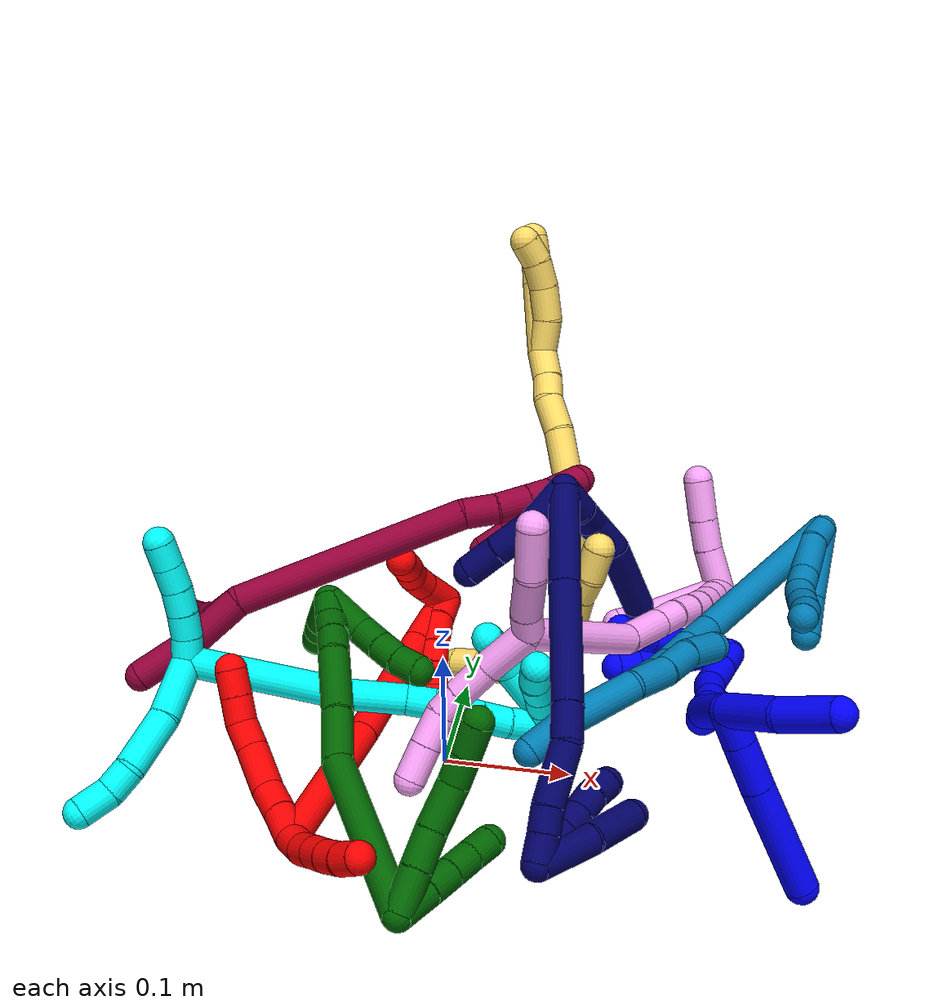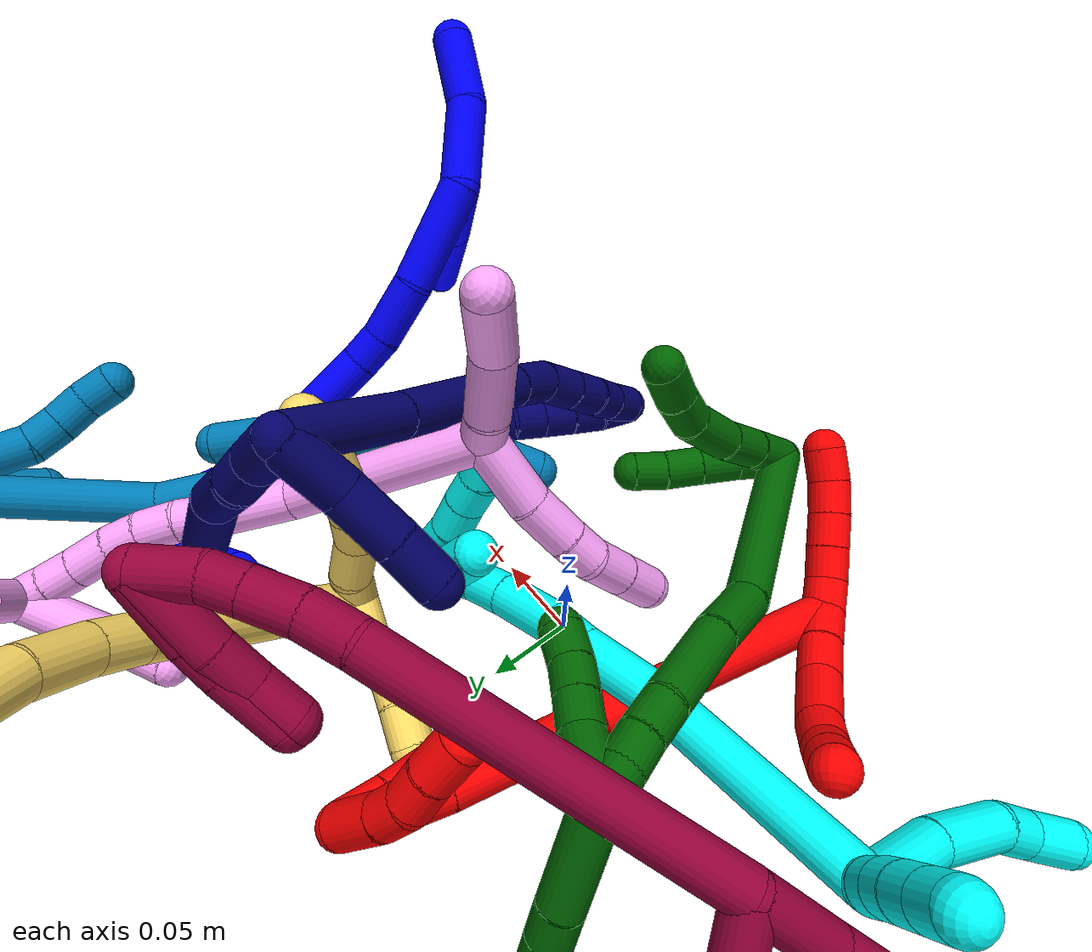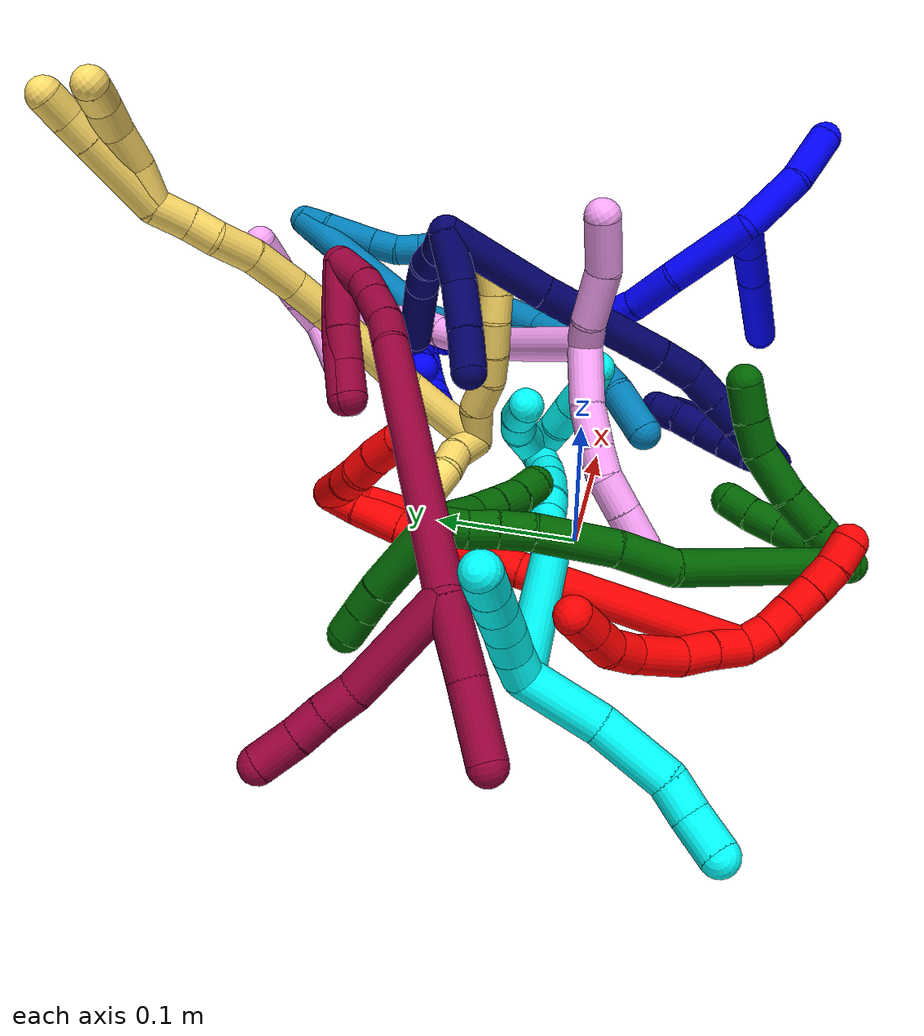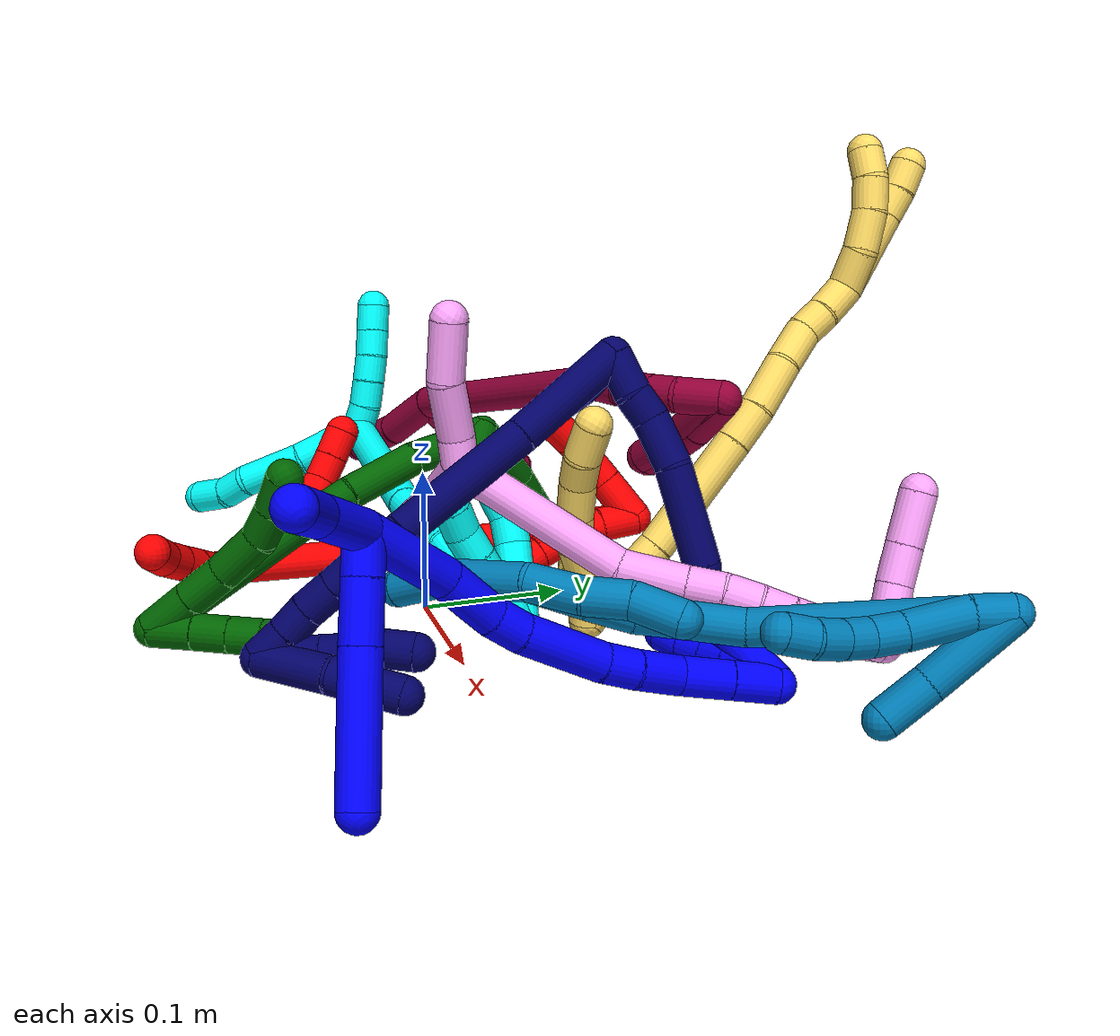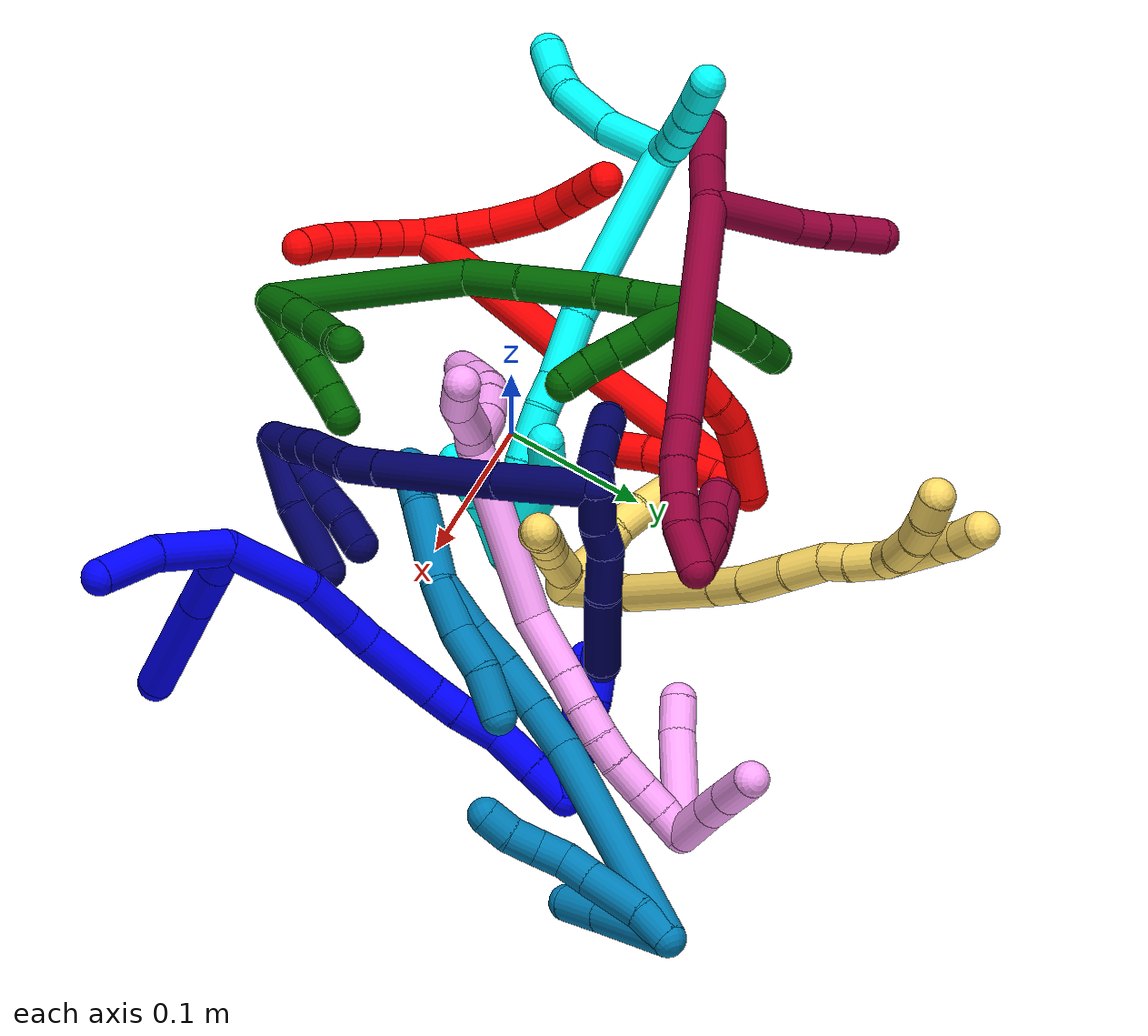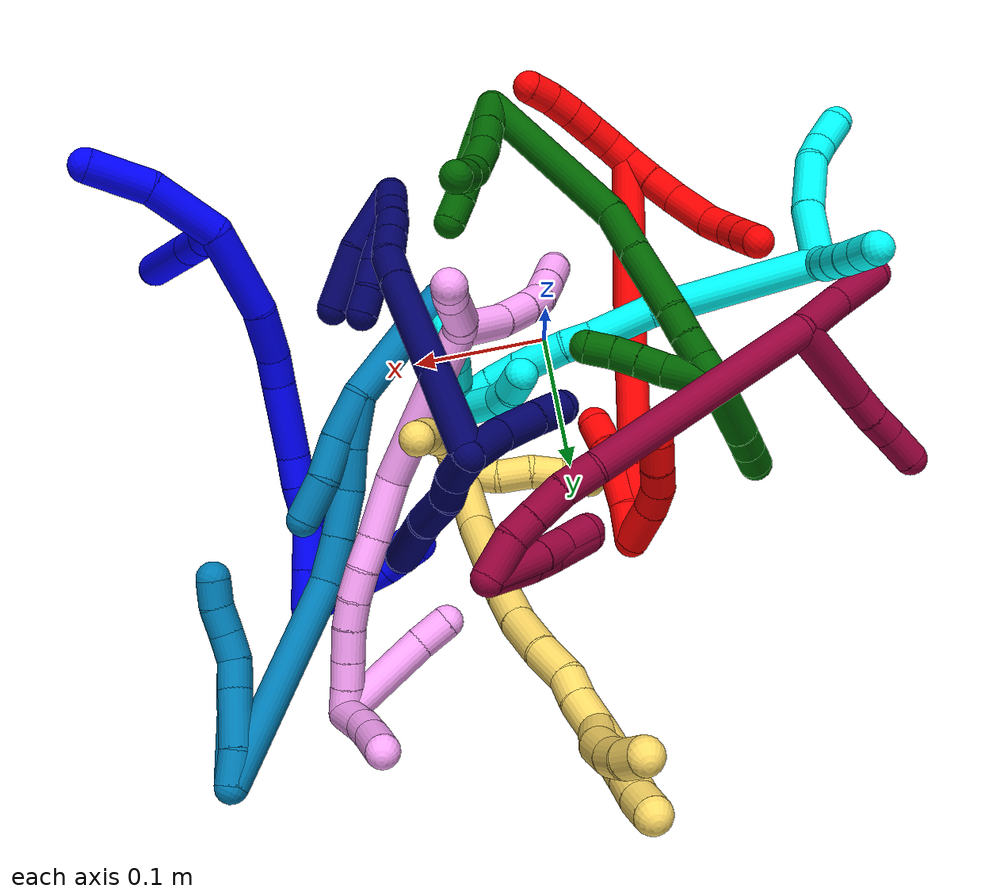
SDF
<sdf version="1.7">
 <world name="default">
  <plugin name="TubeGeneratorPlugin" filename="libtube_generator_plugin.so"/>
  <model name="photoneo_s_sensor">
   <static>1</static>
   <pose>0 0 2 1.57079 1.57079 3.14159</pose>
   <link name="link">
    <inertial><mass>0.1</mass></inertial>
    <sensor name="sensor" type="depth">
     <update_rate>30</update_rate>
     <camera>
      <horizontal_fov>1.22</horizontal_fov>
      <image><width>1920</width><height>1200</height><format>B8G8R8</format></image>
      <clip><near>0.1</near><far>4</far></clip>
      <depth_camera><output>points</output></depth_camera>
     </camera>
     <plugin name="camera_plugin" filename="libgazebo_ros_depth_camera.so">
      <baseline>0.2</baseline>
      <alwaysOn>1</alwaysOn>
      <updateRate>0.0</updateRate>
      <cameraName>camera_ir</cameraName>
      <imageTopicName>/camera/color/image_raw</imageTopicName>
      <cameraInfoTopicName>/camera/color/camera_info</cameraInfoTopicName>
      <depthImageTopicName>/camera/depth/image_raw</depthImageTopicName>
      <depthImageCameraInfoTopicName>/camera/depth/camera_info</depthImageCameraInfoTopicName>
      <pointCloudTopicName>/camera/depth/points</pointCloudTopicName>
      <frameName>fr_optical</frameName>
      <pointCloudCutoff>0.1</pointCloudCutoff>
      <pointCloudCutoffMax>2.0</pointCloudCutoffMax>
      <distortionK1>0</distortionK1>
      <distortionK2>0</distortionK2>
      <distortionK3>0</distortionK3>
      <distortionT1>0</distortionT1>
      <distortionT2>0</distortionT2>
      <CxPrime>0</CxPrime>
      <Cx>0</Cx>
      <Cy>0</Cy>
      <focalLength>0</focalLength>
      <hackBaseline>0</hackBaseline>
     </plugin>
    </sensor>
   </link>
  </model>
  <gravity>0 0 -9.8</gravity>
  <magnetic_field>6e-06 2.3e-05 -4.2e-05</magnetic_field>
  <atmosphere type="adiabatic"/>
  <physics name="default_physics" default="0" type="ode">
   <max_step_size>0.003</max_step_size>
   <real_time_factor>1</real_time_factor>
   <real_time_update_rate>1000</real_time_update_rate>
   <max_contacts>10000</max_contacts>
   <ode>
    <solver>
     <type>quick</type>
     <iters>100</iters>
     <sor>1.3</sor>
     <use_dynamic_moi_rescaling>0</use_dynamic_moi_rescaling>
    </solver>
    <constraints>
     <contact_max_correcting_vel>0</contact_max_correcting_vel>
     <contact_surface_layer>0.001</contact_surface_layer>
     <cfm>0</cfm>
     <erp>0.2</erp>
    </constraints>
   </ode>
  </physics>
  <scene><ambient>0.4 0.4 0.4 1</ambient><background>0.7 0.7 0.7 1</background><shadows>0</shadows></scene>
  <audio><device>default</device></audio>
  <spherical_coordinates>
   <surface_model>EARTH_WGS84</surface_model>
   <latitude_deg>0</latitude_deg>
   <longitude_deg>0</longitude_deg>
   <elevation>0</elevation>
   <heading_deg>0</heading_deg>
  </spherical_coordinates>
  <model name="bin">
   <static>1</static>
   <link name="bottom">
    <collision name="collision-bottom">
     <pose>0 0 -0.01 0 -0 0</pose>
     <geometry><box><size>0.8 0.6 0.02</size></box></geometry>
     <surface>
      <friction><ode><mu>100</mu><mu2>100</mu2></ode></friction>
      <contact><collide_bitmask>65535</collide_bitmask></contact>
     </surface>
    </collision>
   </link>
   <link name="west_wall">
    <collision name="collision-west_wall">
     <pose>-0.41 0 0.1 0 -0 0</pose>
     <geometry><box><size>0.02 0.6 0.2</size></box></geometry>
     <surface>
      <friction><ode><mu>100</mu><mu2>100</mu2></ode></friction>
      <contact><collide_bitmask>65535</collide_bitmask></contact>
     </surface>
    </collision>
   </link>
   <link name="east_wall">
    <collision name="collision-east_wall">
     <pose>0.41 0 0.1 0 -0 0</pose>
     <geometry><box><size>0.02 0.6 0.2</size></box></geometry>
     <surface>
      <friction><ode><mu>100</mu><mu2>100</mu2></ode></friction>
      <contact><collide_bitmask>65535</collide_bitmask></contact>
     </surface>
    </collision>
   </link>
   <link name="south_wall">
    <collision name="collision-south_wall">
     <pose>0 -0.31 0.1 0 -0 0</pose>
     <geometry><box><size>0.8 0.02 0.2</size></box></geometry>
     <surface>
      <friction><ode><mu>100</mu><mu2>100</mu2></ode></friction>
      <contact><collide_bitmask>65535</collide_bitmask></contact>
     </surface>
    </collision>
   </link>
   <link name="north_wall">
    <collision name="collision-north_wall">
     <pose>0 0.31 0.1 0 -0 0</pose>
     <geometry><box><size>0.8 0.02 0.2</size></box></geometry>
     <surface>
      <friction><ode><mu>100</mu><mu2>100</mu2></ode></friction>
      <contact><collide_bitmask>65535</collide_bitmask></contact>
     </surface>
    </collision>
   </link>
  </model>
  <model name="1">
   <static>0</static>
   <link name="1">
    <collision name="collision-cylinder-e_1_2_8">
     <pose>0.009461 0.002998 0.007987 -0.359085 0.837057 -0.161114</pose>
     <geometry><cylinder><radius>0.0125</radius><length>0.025479</length></cylinder></geometry>
     <surface>
      <friction><ode><mu>1.16</mu><mu2>1.16</mu2><slip1>0</slip1><slip2>0</slip2></ode></friction>
      <contact><ode><kp>1e+06</kp><kd>1</kd><max_vel>0</max_vel><min_depth>0.001</min_depth></ode></contact>
     </surface>
    </collision>
    <visual name="visual-cylinder-e_1_2_8">
     <pose>0.009461 0.002998 0.007987 -0.359085 0.837057 -0.161114</pose>
     <geometry><cylinder><radius>0.0125</radius><length>0.025479</length></cylinder></geometry>
     <material><ambient>0 0 1 1</ambient></material>
    </visual>
    <collision name="collision-cylinder-e_2_8_9">
     <pose>0.032858 0.009986 0.027812 -0.325083 0.839936 -0.146192</pose>
     <geometry><cylinder><radius>0.0125</radius><length>0.037432</length></cylinder></geometry>
     <surface>
      <friction><ode><mu>1.16</mu><mu2>1.16</mu2><slip1>0</slip1><slip2>0</slip2></ode></friction>
      <contact><ode><kp>1e+06</kp><kd>1</kd><max_vel>0</max_vel><min_depth>0.001</min_depth></ode></contact>
     </surface>
    </collision>
    <visual name="visual-cylinder-e_2_8_9">
     <pose>0.032858 0.009986 0.027812 -0.325083 0.839936 -0.146192</pose>
     <geometry><cylinder><radius>0.0125</radius><length>0.037432</length></cylinder></geometry>
     <material><ambient>0 0 1 1</ambient></material>
    </visual>
    <collision name="collision-cylinder-e_3_9_6">
     <pose>0.07847 0.023172 0.06808 -0.312829 0.814579 -0.13586</pose>
     <geometry><cylinder><radius>0.0125</radius><length>0.087089</length></cylinder></geometry>
     <surface>
      <friction><ode><mu>1.16</mu><mu2>1.16</mu2><slip1>0</slip1><slip2>0</slip2></ode></friction>
      <contact><ode><kp>1e+06</kp><kd>1</kd><max_vel>0</max_vel><min_depth>0.001</min_depth></ode></contact>
     </surface>
    </collision>
    <visual name="visual-cylinder-e_3_9_6">
     <pose>0.07847 0.023172 0.06808 -0.312829 0.814579 -0.13586</pose>
     <geometry><cylinder><radius>0.0125</radius><length>0.087089</length></cylinder></geometry>
     <material><ambient>0 0 1 1</ambient></material>
    </visual>
    <collision name="collision-cylinder-e_1_2_10">
     <pose>-0.002473 -0.025199 0.009447 1.21212 -0.091633 -0.063531</pose>
     <geometry><cylinder><radius>0.0125</radius><length>0.05405</length></cylinder></geometry>
     <surface>
      <friction><ode><mu>1.16</mu><mu2>1.16</mu2><slip1>0</slip1><slip2>0</slip2></ode></friction>
      <contact><ode><kp>1e+06</kp><kd>1</kd><max_vel>0</max_vel><min_depth>0.001</min_depth></ode></contact>
     </surface>
    </collision>
    <visual name="visual-cylinder-e_1_2_10">
     <pose>-0.002473 -0.025199 0.009447 1.21212 -0.091633 -0.063531</pose>
     <geometry><cylinder><radius>0.0125</radius><length>0.05405</length></cylinder></geometry>
     <material><ambient>0 0 1 1</ambient></material>
    </visual>
    <collision name="collision-cylinder-e_2_10_5">
     <pose>-0.009434 -0.068726 0.032 0.950011 -0.196637 -0.101366</pose>
     <geometry><cylinder><radius>0.0125</radius><length>0.04595</length></cylinder></geometry>
     <surface>
      <friction><ode><mu>1.16</mu><mu2>1.16</mu2><slip1>0</slip1><slip2>0</slip2></ode></friction>
      <contact><ode><kp>1e+06</kp><kd>1</kd><max_vel>0</max_vel><min_depth>0.001</min_depth></ode></contact>
     </surface>
    </collision>
    <visual name="visual-cylinder-e_2_10_5">
     <pose>-0.009434 -0.068726 0.032 0.950011 -0.196637 -0.101366</pose>
     <geometry><cylinder><radius>0.0125</radius><length>0.04595</length></cylinder></geometry>
     <material><ambient>0 0 1 1</ambient></material>
    </visual>
    <collision name="collision-cylinder-e_1_2_11">
     <pose>0.001984 0.033152 0.003592 -1.46287 0.059428 -0.05334</pose>
     <geometry><cylinder><radius>0.0125</radius><length>0.066809</length></cylinder></geometry>
     <surface>
      <friction><ode><mu>1.16</mu><mu2>1.16</mu2><slip1>0</slip1><slip2>0</slip2></ode></friction>
      <contact><ode><kp>1e+06</kp><kd>1</kd><max_vel>0</max_vel><min_depth>0.001</min_depth></ode></contact>
     </surface>
    </collision>
    <visual name="visual-cylinder-e_1_2_11">
     <pose>0.001984 0.033152 0.003592 -1.46287 0.059428 -0.05334</pose>
     <geometry><cylinder><radius>0.0125</radius><length>0.066809</length></cylinder></geometry>
     <material><ambient>0 0 1 1</ambient></material>
    </visual>
    <collision name="collision-cylinder-e_2_11_12">
     <pose>0.006605 0.084733 0.013474 -1.24188 0.134587 -0.096345</pose>
     <geometry><cylinder><radius>0.0125</radius><length>0.039302</length></cylinder></geometry>
     <surface>
      <friction><ode><mu>1.16</mu><mu2>1.16</mu2><slip1>0</slip1><slip2>0</slip2></ode></friction>
      <contact><ode><kp>1e+06</kp><kd>1</kd><max_vel>0</max_vel><min_depth>0.001</min_depth></ode></contact>
     </surface>
    </collision>
    <visual name="visual-cylinder-e_2_11_12">
     <pose>0.006605 0.084733 0.013474 -1.24188 0.134587 -0.096345</pose>
     <geometry><cylinder><radius>0.0125</radius><length>0.039302</length></cylinder></geometry>
     <material><ambient>0 0 1 1</ambient></material>
    </visual>
    <collision name="collision-cylinder-e_3_12_13">
     <pose>0.008797 0.113216 0.023932 -1.17778 -0.040847 0.027286</pose>
     <geometry><cylinder><radius>0.0125</radius><length>0.021787</length></cylinder></geometry>
     <surface>
      <friction><ode><mu>1.16</mu><mu2>1.16</mu2><slip1>0</slip1><slip2>0</slip2></ode></friction>
      <contact><ode><kp>1e+06</kp><kd>1</kd><max_vel>0</max_vel><min_depth>0.001</min_depth></ode></contact>
     </surface>
    </collision>
    <visual name="visual-cylinder-e_3_12_13">
     <pose>0.008797 0.113216 0.023932 -1.17778 -0.040847 0.027286</pose>
     <geometry><cylinder><radius>0.0125</radius><length>0.021787</length></cylinder></geometry>
     <material><ambient>0 0 1 1</ambient></material>
    </visual>
    <collision name="collision-cylinder-e_4_13_14">
     <pose>0.003241 0.149353 0.037588 -1.22193 -0.182093 0.127709</pose>
     <geometry><cylinder><radius>0.0125</radius><length>0.056441</length></cylinder></geometry>
     <surface>
      <friction><ode><mu>1.16</mu><mu2>1.16</mu2><slip1>0</slip1><slip2>0</slip2></ode></friction>
      <contact><ode><kp>1e+06</kp><kd>1</kd><max_vel>0</max_vel><min_depth>0.001</min_depth></ode></contact>
     </surface>
    </collision>
    <visual name="visual-cylinder-e_4_13_14">
     <pose>0.003241 0.149353 0.037588 -1.22193 -0.182093 0.127709</pose>
     <geometry><cylinder><radius>0.0125</radius><length>0.056441</length></cylinder></geometry>
     <material><ambient>0 0 1 1</ambient></material>
    </visual>
    <collision name="collision-cylinder-e_5_14_15">
     <pose>-0.005418 0.185505 0.050753 -1.22069 -0.319719 0.224597</pose>
     <geometry><cylinder><radius>0.0125</radius><length>0.022585</length></cylinder></geometry>
     <surface>
      <friction><ode><mu>1.16</mu><mu2>1.16</mu2><slip1>0</slip1><slip2>0</slip2></ode></friction>
      <contact><ode><kp>1e+06</kp><kd>1</kd><max_vel>0</max_vel><min_depth>0.001</min_depth></ode></contact>
     </surface>
    </collision>
    <visual name="visual-cylinder-e_5_14_15">
     <pose>-0.005418 0.185505 0.050753 -1.22069 -0.319719 0.224597</pose>
     <geometry><cylinder><radius>0.0125</radius><length>0.022585</length></cylinder></geometry>
     <material><ambient>0 0 1 1</ambient></material>
    </visual>
    <collision name="collision-cylinder-e_6_15_16">
     <pose>-0.014057 0.209987 0.057787 -1.34193 -0.331247 0.263842</pose>
     <geometry><cylinder><radius>0.0125</radius><length>0.031296</length></cylinder></geometry>
     <surface>
      <friction><ode><mu>1.16</mu><mu2>1.16</mu2><slip1>0</slip1><slip2>0</slip2></ode></friction>
      <contact><ode><kp>1e+06</kp><kd>1</kd><max_vel>0</max_vel><min_depth>0.001</min_depth></ode></contact>
     </surface>
    </collision>
    <visual name="visual-cylinder-e_6_15_16">
     <pose>-0.014057 0.209987 0.057787 -1.34193 -0.331247 0.263842</pose>
     <geometry><cylinder><radius>0.0125</radius><length>0.031296</length></cylinder></geometry>
     <material><ambient>0 0 1 1</ambient></material>
    </visual>
    <collision name="collision-cylinder-e_7_16_17">
     <pose>-0.027411 0.236722 0.068458 -1.03515 -0.523144 0.302506</pose>
     <geometry><cylinder><radius>0.0125</radius><length>0.033087</length></cylinder></geometry>
     <surface>
      <friction><ode><mu>1.16</mu><mu2>1.16</mu2><slip1>0</slip1><slip2>0</slip2></ode></friction>
      <contact><ode><kp>1e+06</kp><kd>1</kd><max_vel>0</max_vel><min_depth>0.001</min_depth></ode></contact>
     </surface>
    </collision>
    <visual name="visual-cylinder-e_7_16_17">
     <pose>-0.027411 0.236722 0.068458 -1.03515 -0.523144 0.302506</pose>
     <geometry><cylinder><radius>0.0125</radius><length>0.033087</length></cylinder></geometry>
     <material><ambient>0 0 1 1</ambient></material>
    </visual>
    <collision name="collision-cylinder-e_8_17_1">
     <pose>-0.042773 0.25985 0.081995 -1.04828 -0.517499 0.303658</pose>
     <geometry><cylinder><radius>0.0125</radius><length>0.028693</length></cylinder></geometry>
     <surface>
      <friction><ode><mu>1.16</mu><mu2>1.16</mu2><slip1>0</slip1><slip2>0</slip2></ode></friction>
      <contact><ode><kp>1e+06</kp><kd>1</kd><max_vel>0</max_vel><min_depth>0.001</min_depth></ode></contact>
     </surface>
    </collision>
    <visual name="visual-cylinder-e_8_17_1">
     <pose>-0.042773 0.25985 0.081995 -1.04828 -0.517499 0.303658</pose>
     <geometry><cylinder><radius>0.0125</radius><length>0.028693</length></cylinder></geometry>
     <material><ambient>0 0 1 1</ambient></material>
    </visual>
    <collision name="collision-cylinder-e_1_1_18">
     <pose>-0.049408 0.270123 0.065395 3.11836 0.020259 1.434</pose>
     <geometry><cylinder><radius>0.0125</radius><length>0.045666</length></cylinder></geometry>
     <surface>
      <friction><ode><mu>1.16</mu><mu2>1.16</mu2><slip1>0</slip1><slip2>0</slip2></ode></friction>
      <contact><ode><kp>1e+06</kp><kd>1</kd><max_vel>0</max_vel><min_depth>0.001</min_depth></ode></contact>
     </surface>
    </collision>
    <visual name="visual-cylinder-e_1_1_18">
     <pose>-0.049408 0.270123 0.065395 3.11836 0.020259 1.434</pose>
     <geometry><cylinder><radius>0.0125</radius><length>0.045666</length></cylinder></geometry>
     <material><ambient>0 0 1 1</ambient></material>
    </visual>
    <collision name="collision-cylinder-e_2_18_19">
     <pose>-0.048146 0.269789 0.031224 -3.12429 0.070296 -2.65906</pose>
     <geometry><cylinder><radius>0.0125</radius><length>0.022758</length></cylinder></geometry>
     <surface>
      <friction><ode><mu>1.16</mu><mu2>1.16</mu2><slip1>0</slip1><slip2>0</slip2></ode></friction>
      <contact><ode><kp>1e+06</kp><kd>1</kd><max_vel>0</max_vel><min_depth>0.001</min_depth></ode></contact>
     </surface>
    </collision>
    <visual name="visual-cylinder-e_2_18_19">
     <pose>-0.048146 0.269789 0.031224 -3.12429 0.070296 -2.65906</pose>
     <geometry><cylinder><radius>0.0125</radius><length>0.022758</length></cylinder></geometry>
     <material><ambient>0 0 1 1</ambient></material>
    </visual>
    <collision name="collision-cylinder-e_3_19_4">
     <pose>-0.047459 0.267136 0.004346 2.96008 -0.007106 -0.078049</pose>
     <geometry><cylinder><radius>0.0125</radius><length>0.031576</length></cylinder></geometry>
     <surface>
      <friction><ode><mu>1.16</mu><mu2>1.16</mu2><slip1>0</slip1><slip2>0</slip2></ode></friction>
      <contact><ode><kp>1e+06</kp><kd>1</kd><max_vel>0</max_vel><min_depth>0.001</min_depth></ode></contact>
     </surface>
    </collision>
    <visual name="visual-cylinder-e_3_19_4">
     <pose>-0.047459 0.267136 0.004346 2.96008 -0.007106 -0.078049</pose>
     <geometry><cylinder><radius>0.0125</radius><length>0.031576</length></cylinder></geometry>
     <material><ambient>0 0 1 1</ambient></material>
    </visual>
    <collision name="collision-cylinder-e_1_1_20">
     <pose>-0.047905 0.270444 0.078414 3.12022 0.197852 2.92708</pose>
     <geometry><cylinder><radius>0.0125</radius><length>0.02</length></cylinder></geometry>
     <surface>
      <friction><ode><mu>1.16</mu><mu2>1.16</mu2><slip1>0</slip1><slip2>0</slip2></ode></friction>
      <contact><ode><kp>1e+06</kp><kd>1</kd><max_vel>0</max_vel><min_depth>0.001</min_depth></ode></contact>
     </surface>
    </collision>
    <visual name="visual-cylinder-e_1_1_20">
     <pose>-0.047905 0.270444 0.078414 3.12022 0.197852 2.92708</pose>
     <geometry><cylinder><radius>0.0125</radius><length>0.02</length></cylinder></geometry>
     <material><ambient>0 0 1 1</ambient></material>
    </visual>
    <collision name="collision-cylinder-e_2_20_21">
     <pose>-0.041759 0.271061 0.059565 -3.05053 0.431239 -2.73138</pose>
     <geometry><cylinder><radius>0.0125</radius><length>0.02</length></cylinder></geometry>
     <surface>
      <friction><ode><mu>1.16</mu><mu2>1.16</mu2><slip1>0</slip1><slip2>0</slip2></ode></friction>
      <contact><ode><kp>1e+06</kp><kd>1</kd><max_vel>0</max_vel><min_depth>0.001</min_depth></ode></contact>
     </surface>
    </collision>
    <visual name="visual-cylinder-e_2_20_21">
     <pose>-0.041759 0.271061 0.059565 -3.05053 0.431239 -2.73138</pose>
     <geometry><cylinder><radius>0.0125</radius><length>0.02</length></cylinder></geometry>
     <material><ambient>0 0 1 1</ambient></material>
    </visual>
    <collision name="collision-cylinder-e_3_21_22">
     <pose>-0.033516 0.272831 0.04143 -3.03809 0.418469 -2.66306</pose>
     <geometry><cylinder><radius>0.0125</radius><length>0.02</length></cylinder></geometry>
     <surface>
      <friction><ode><mu>1.16</mu><mu2>1.16</mu2><slip1>0</slip1><slip2>0</slip2></ode></friction>
      <contact><ode><kp>1e+06</kp><kd>1</kd><max_vel>0</max_vel><min_depth>0.001</min_depth></ode></contact>
     </surface>
    </collision>
    <visual name="visual-cylinder-e_3_21_22">
     <pose>-0.033516 0.272831 0.04143 -3.03809 0.418469 -2.66306</pose>
     <geometry><cylinder><radius>0.0125</radius><length>0.02</length></cylinder></geometry>
     <material><ambient>0 0 1 1</ambient></material>
    </visual>
    <collision name="collision-cylinder-e_4_22_23">
     <pose>-0.025686 0.273908 0.023079 -3.12721 0.386149 -3.06804</pose>
     <geometry><cylinder><radius>0.0125</radius><length>0.02</length></cylinder></geometry>
     <surface>
      <friction><ode><mu>1.16</mu><mu2>1.16</mu2><slip1>0</slip1><slip2>0</slip2></ode></friction>
      <contact><ode><kp>1e+06</kp><kd>1</kd><max_vel>0</max_vel><min_depth>0.001</min_depth></ode></contact>
     </surface>
    </collision>
    <visual name="visual-cylinder-e_4_22_23">
     <pose>-0.025686 0.273908 0.023079 -3.12721 0.386149 -3.06804</pose>
     <geometry><cylinder><radius>0.0125</radius><length>0.02</length></cylinder></geometry>
     <material><ambient>0 0 1 1</ambient></material>
    </visual>
    <collision name="collision-cylinder-e_5_23_3">
     <pose>-0.019098 0.273119 0.004267 3.04527 0.28609 2.4957</pose>
     <geometry><cylinder><radius>0.0125</radius><length>0.02</length></cylinder></geometry>
     <surface>
      <friction><ode><mu>1.16</mu><mu2>1.16</mu2><slip1>0</slip1><slip2>0</slip2></ode></friction>
      <contact><ode><kp>1e+06</kp><kd>1</kd><max_vel>0</max_vel><min_depth>0.001</min_depth></ode></contact>
     </surface>
    </collision>
    <visual name="visual-cylinder-e_5_23_3">
     <pose>-0.019098 0.273119 0.004267 3.04527 0.28609 2.4957</pose>
     <geometry><cylinder><radius>0.0125</radius><length>0.02</length></cylinder></geometry>
     <material><ambient>0 0 1 1</ambient></material>
    </visual>
    <collision name="collision-sphere-3">
     <pose>-0.016276 0.272196 -0.005282 0 -0 0</pose>
     <geometry><sphere><radius>0.0125</radius></sphere></geometry>
     <surface>
      <friction><ode><mu>1.16</mu><mu2>1.16</mu2><slip1>0</slip1><slip2>0</slip2></ode></friction>
      <contact><ode><kp>1e+06</kp><kd>1</kd><max_vel>0</max_vel><min_depth>0.001</min_depth></ode></contact>
     </surface>
    </collision>
    <visual name="visual-sphere-3">
     <pose>-0.016276 0.272196 -0.005282 0 -0 0</pose>
     <geometry><sphere><radius>0.0125</radius></sphere></geometry>
     <material><ambient>0 0 1 1</ambient></material>
    </visual>
    <collision name="collision-sphere-23">
     <pose>-0.02192 0.274042 0.013816 0 -0 0</pose>
     <geometry><sphere><radius>0.0125</radius></sphere></geometry>
     <surface>
      <friction><ode><mu>1.16</mu><mu2>1.16</mu2><slip1>0</slip1><slip2>0</slip2></ode></friction>
      <contact><ode><kp>1e+06</kp><kd>1</kd><max_vel>0</max_vel><min_depth>0.001</min_depth></ode></contact>
     </surface>
    </collision>
    <visual name="visual-sphere-23">
     <pose>-0.02192 0.274042 0.013816 0 -0 0</pose>
     <geometry><sphere><radius>0.0125</radius></sphere></geometry>
     <material><ambient>0 0 1 1</ambient></material>
    </visual>
    <collision name="collision-sphere-22">
     <pose>-0.029452 0.273775 0.032342 0 -0 0</pose>
     <geometry><sphere><radius>0.0125</radius></sphere></geometry>
     <surface>
      <friction><ode><mu>1.16</mu><mu2>1.16</mu2><slip1>0</slip1><slip2>0</slip2></ode></friction>
      <contact><ode><kp>1e+06</kp><kd>1</kd><max_vel>0</max_vel><min_depth>0.001</min_depth></ode></contact>
     </surface>
    </collision>
    <visual name="visual-sphere-22">
     <pose>-0.029452 0.273775 0.032342 0 -0 0</pose>
     <geometry><sphere><radius>0.0125</radius></sphere></geometry>
     <material><ambient>0 0 1 1</ambient></material>
    </visual>
    <collision name="collision-sphere-21">
     <pose>-0.037579 0.271887 0.050518 0 -0 0</pose>
     <geometry><sphere><radius>0.0125</radius></sphere></geometry>
     <surface>
      <friction><ode><mu>1.16</mu><mu2>1.16</mu2><slip1>0</slip1><slip2>0</slip2></ode></friction>
      <contact><ode><kp>1e+06</kp><kd>1</kd><max_vel>0</max_vel><min_depth>0.001</min_depth></ode></contact>
     </surface>
    </collision>
    <visual name="visual-sphere-21">
     <pose>-0.037579 0.271887 0.050518 0 -0 0</pose>
     <geometry><sphere><radius>0.0125</radius></sphere></geometry>
     <material><ambient>0 0 1 1</ambient></material>
    </visual>
    <collision name="collision-sphere-20">
     <pose>-0.045939 0.270235 0.068612 0 -0 0</pose>
     <geometry><sphere><radius>0.0125</radius></sphere></geometry>
     <surface>
      <friction><ode><mu>1.16</mu><mu2>1.16</mu2><slip1>0</slip1><slip2>0</slip2></ode></friction>
      <contact><ode><kp>1e+06</kp><kd>1</kd><max_vel>0</max_vel><min_depth>0.001</min_depth></ode></contact>
     </surface>
    </collision>
    <visual name="visual-sphere-20">
     <pose>-0.045939 0.270235 0.068612 0 -0 0</pose>
     <geometry><sphere><radius>0.0125</radius></sphere></geometry>
     <material><ambient>0 0 1 1</ambient></material>
    </visual>
    <collision name="collision-sphere-4">
     <pose>-0.047571 0.264286 -0.011182 0 -0 0</pose>
     <geometry><sphere><radius>0.0125</radius></sphere></geometry>
     <surface>
      <friction><ode><mu>1.16</mu><mu2>1.16</mu2><slip1>0</slip1><slip2>0</slip2></ode></friction>
      <contact><ode><kp>1e+06</kp><kd>1</kd><max_vel>0</max_vel><min_depth>0.001</min_depth></ode></contact>
     </surface>
    </collision>
    <visual name="visual-sphere-4">
     <pose>-0.047571 0.264286 -0.011182 0 -0 0</pose>
     <geometry><sphere><radius>0.0125</radius></sphere></geometry>
     <material><ambient>0 0 1 1</ambient></material>
    </visual>
    <collision name="collision-sphere-5">
     <pose>-0.013923 -0.087054 0.045107 0 -0 0</pose>
     <geometry><sphere><radius>0.0125</radius></sphere></geometry>
     <surface>
      <friction><ode><mu>1.16</mu><mu2>1.16</mu2><slip1>0</slip1><slip2>0</slip2></ode></friction>
      <contact><ode><kp>1e+06</kp><kd>1</kd><max_vel>0</max_vel><min_depth>0.001</min_depth></ode></contact>
     </surface>
    </collision>
    <visual name="visual-sphere-5">
     <pose>-0.013923 -0.087054 0.045107 0 -0 0</pose>
     <geometry><sphere><radius>0.0125</radius></sphere></geometry>
     <material><ambient>0 0 1 1</ambient></material>
    </visual>
    <collision name="collision-sphere-10">
     <pose>-0.004946 -0.050398 0.018894 0 -0 0</pose>
     <geometry><sphere><radius>0.0125</radius></sphere></geometry>
     <surface>
      <friction><ode><mu>1.16</mu><mu2>1.16</mu2><slip1>0</slip1><slip2>0</slip2></ode></friction>
      <contact><ode><kp>1e+06</kp><kd>1</kd><max_vel>0</max_vel><min_depth>0.001</min_depth></ode></contact>
     </surface>
    </collision>
    <visual name="visual-sphere-10">
     <pose>-0.004946 -0.050398 0.018894 0 -0 0</pose>
     <geometry><sphere><radius>0.0125</radius></sphere></geometry>
     <material><ambient>0 0 1 1</ambient></material>
    </visual>
    <collision name="collision-sphere-6">
     <pose>0.110146 0.032367 0.096509 0 -0 0</pose>
     <geometry><sphere><radius>0.0125</radius></sphere></geometry>
     <surface>
      <friction><ode><mu>1.16</mu><mu2>1.16</mu2><slip1>0</slip1><slip2>0</slip2></ode></friction>
      <contact><ode><kp>1e+06</kp><kd>1</kd><max_vel>0</max_vel><min_depth>0.001</min_depth></ode></contact>
     </surface>
    </collision>
    <visual name="visual-sphere-6">
     <pose>0.110146 0.032367 0.096509 0 -0 0</pose>
     <geometry><sphere><radius>0.0125</radius></sphere></geometry>
     <material><ambient>0 0 1 1</ambient></material>
    </visual>
    <collision name="collision-sphere-9">
     <pose>0.046794 0.013976 0.039651 0 -0 0</pose>
     <geometry><sphere><radius>0.0125</radius></sphere></geometry>
     <surface>
      <friction><ode><mu>1.16</mu><mu2>1.16</mu2><slip1>0</slip1><slip2>0</slip2></ode></friction>
      <contact><ode><kp>1e+06</kp><kd>1</kd><max_vel>0</max_vel><min_depth>0.001</min_depth></ode></contact>
     </surface>
    </collision>
    <visual name="visual-sphere-9">
     <pose>0.046794 0.013976 0.039651 0 -0 0</pose>
     <geometry><sphere><radius>0.0125</radius></sphere></geometry>
     <material><ambient>0 0 1 1</ambient></material>
    </visual>
    <collision name="collision-sphere-2">
     <geometry><sphere><radius>0.0125</radius></sphere></geometry>
     <surface>
      <friction><ode><mu>1.16</mu><mu2>1.16</mu2><slip1>0</slip1><slip2>0</slip2></ode></friction>
      <contact><ode><kp>1e+06</kp><kd>1</kd><max_vel>0</max_vel><min_depth>0.001</min_depth></ode></contact>
     </surface>
    </collision>
    <visual name="visual-sphere-2">
     <geometry><sphere><radius>0.0125</radius></sphere></geometry>
     <material><ambient>0 0 1 1</ambient></material>
    </visual>
    <collision name="collision-sphere-19">
     <pose>-0.047347 0.269986 0.019875 0 -0 0</pose>
     <geometry><sphere><radius>0.0125</radius></sphere></geometry>
     <surface>
      <friction><ode><mu>1.16</mu><mu2>1.16</mu2><slip1>0</slip1><slip2>0</slip2></ode></friction>
      <contact><ode><kp>1e+06</kp><kd>1</kd><max_vel>0</max_vel><min_depth>0.001</min_depth></ode></contact>
     </surface>
    </collision>
    <visual name="visual-sphere-19">
     <pose>-0.047347 0.269986 0.019875 0 -0 0</pose>
     <geometry><sphere><radius>0.0125</radius></sphere></geometry>
     <material><ambient>0 0 1 1</ambient></material>
    </visual>
    <collision name="collision-sphere-8">
     <pose>0.018923 0.005996 0.015974 0 -0 0</pose>
     <geometry><sphere><radius>0.0125</radius></sphere></geometry>
     <surface>
      <friction><ode><mu>1.16</mu><mu2>1.16</mu2><slip1>0</slip1><slip2>0</slip2></ode></friction>
      <contact><ode><kp>1e+06</kp><kd>1</kd><max_vel>0</max_vel><min_depth>0.001</min_depth></ode></contact>
     </surface>
    </collision>
    <visual name="visual-sphere-8">
     <pose>0.018923 0.005996 0.015974 0 -0 0</pose>
     <geometry><sphere><radius>0.0125</radius></sphere></geometry>
     <material><ambient>0 0 1 1</ambient></material>
    </visual>
    <collision name="collision-sphere-11">
     <pose>0.003968 0.066303 0.007184 0 -0 0</pose>
     <geometry><sphere><radius>0.0125</radius></sphere></geometry>
     <surface>
      <friction><ode><mu>1.16</mu><mu2>1.16</mu2><slip1>0</slip1><slip2>0</slip2></ode></friction>
      <contact><ode><kp>1e+06</kp><kd>1</kd><max_vel>0</max_vel><min_depth>0.001</min_depth></ode></contact>
     </surface>
    </collision>
    <visual name="visual-sphere-11">
     <pose>0.003968 0.066303 0.007184 0 -0 0</pose>
     <geometry><sphere><radius>0.0125</radius></sphere></geometry>
     <material><ambient>0 0 1 1</ambient></material>
    </visual>
    <collision name="collision-sphere-12">
     <pose>0.009242 0.103162 0.019764 0 -0 0</pose>
     <geometry><sphere><radius>0.0125</radius></sphere></geometry>
     <surface>
      <friction><ode><mu>1.16</mu><mu2>1.16</mu2><slip1>0</slip1><slip2>0</slip2></ode></friction>
      <contact><ode><kp>1e+06</kp><kd>1</kd><max_vel>0</max_vel><min_depth>0.001</min_depth></ode></contact>
     </surface>
    </collision>
    <visual name="visual-sphere-12">
     <pose>0.009242 0.103162 0.019764 0 -0 0</pose>
     <geometry><sphere><radius>0.0125</radius></sphere></geometry>
     <material><ambient>0 0 1 1</ambient></material>
    </visual>
    <collision name="collision-sphere-13">
     <pose>0.008352 0.123271 0.028101 0 -0 0</pose>
     <geometry><sphere><radius>0.0125</radius></sphere></geometry>
     <surface>
      <friction><ode><mu>1.16</mu><mu2>1.16</mu2><slip1>0</slip1><slip2>0</slip2></ode></friction>
      <contact><ode><kp>1e+06</kp><kd>1</kd><max_vel>0</max_vel><min_depth>0.001</min_depth></ode></contact>
     </surface>
    </collision>
    <visual name="visual-sphere-13">
     <pose>0.008352 0.123271 0.028101 0 -0 0</pose>
     <geometry><sphere><radius>0.0125</radius></sphere></geometry>
     <material><ambient>0 0 1 1</ambient></material>
    </visual>
    <collision name="collision-sphere-14">
     <pose>-0.001869 0.175435 0.047075 0 -0 0</pose>
     <geometry><sphere><radius>0.0125</radius></sphere></geometry>
     <surface>
      <friction><ode><mu>1.16</mu><mu2>1.16</mu2><slip1>0</slip1><slip2>0</slip2></ode></friction>
      <contact><ode><kp>1e+06</kp><kd>1</kd><max_vel>0</max_vel><min_depth>0.001</min_depth></ode></contact>
     </surface>
    </collision>
    <visual name="visual-sphere-14">
     <pose>-0.001869 0.175435 0.047075 0 -0 0</pose>
     <geometry><sphere><radius>0.0125</radius></sphere></geometry>
     <material><ambient>0 0 1 1</ambient></material>
    </visual>
    <collision name="collision-sphere-15">
     <pose>-0.008968 0.195575 0.05443 0 -0 0</pose>
     <geometry><sphere><radius>0.0125</radius></sphere></geometry>
     <surface>
      <friction><ode><mu>1.16</mu><mu2>1.16</mu2><slip1>0</slip1><slip2>0</slip2></ode></friction>
      <contact><ode><kp>1e+06</kp><kd>1</kd><max_vel>0</max_vel><min_depth>0.001</min_depth></ode></contact>
     </surface>
    </collision>
    <visual name="visual-sphere-15">
     <pose>-0.008968 0.195575 0.05443 0 -0 0</pose>
     <geometry><sphere><radius>0.0125</radius></sphere></geometry>
     <material><ambient>0 0 1 1</ambient></material>
    </visual>
    <collision name="collision-sphere-16">
     <pose>-0.019146 0.224398 0.061144 0 -0 0</pose>
     <geometry><sphere><radius>0.0125</radius></sphere></geometry>
     <surface>
      <friction><ode><mu>1.16</mu><mu2>1.16</mu2><slip1>0</slip1><slip2>0</slip2></ode></friction>
      <contact><ode><kp>1e+06</kp><kd>1</kd><max_vel>0</max_vel><min_depth>0.001</min_depth></ode></contact>
     </surface>
    </collision>
    <visual name="visual-sphere-16">
     <pose>-0.019146 0.224398 0.061144 0 -0 0</pose>
     <geometry><sphere><radius>0.0125</radius></sphere></geometry>
     <material><ambient>0 0 1 1</ambient></material>
    </visual>
    <collision name="collision-sphere-17">
     <pose>-0.035676 0.249045 0.075773 0 -0 0</pose>
     <geometry><sphere><radius>0.0125</radius></sphere></geometry>
     <surface>
      <friction><ode><mu>1.16</mu><mu2>1.16</mu2><slip1>0</slip1><slip2>0</slip2></ode></friction>
      <contact><ode><kp>1e+06</kp><kd>1</kd><max_vel>0</max_vel><min_depth>0.001</min_depth></ode></contact>
     </surface>
    </collision>
    <visual name="visual-sphere-17">
     <pose>-0.035676 0.249045 0.075773 0 -0 0</pose>
     <geometry><sphere><radius>0.0125</radius></sphere></geometry>
     <material><ambient>0 0 1 1</ambient></material>
    </visual>
    <collision name="collision-sphere-1">
     <pose>-0.049871 0.270654 0.088217 0 -0 0</pose>
     <geometry><sphere><radius>0.0125</radius></sphere></geometry>
     <surface>
      <friction><ode><mu>1.16</mu><mu2>1.16</mu2><slip1>0</slip1><slip2>0</slip2></ode></friction>
      <contact><ode><kp>1e+06</kp><kd>1</kd><max_vel>0</max_vel><min_depth>0.001</min_depth></ode></contact>
     </surface>
    </collision>
    <visual name="visual-sphere-1">
     <pose>-0.049871 0.270654 0.088217 0 -0 0</pose>
     <geometry><sphere><radius>0.0125</radius></sphere></geometry>
     <material><ambient>0 0 1 1</ambient></material>
    </visual>
    <collision name="collision-sphere-18">
     <pose>-0.048946 0.269593 0.042573 0 -0 0</pose>
     <geometry><sphere><radius>0.0125</radius></sphere></geometry>
     <surface>
      <friction><ode><mu>1.16</mu><mu2>1.16</mu2><slip1>0</slip1><slip2>0</slip2></ode></friction>
      <contact><ode><kp>1e+06</kp><kd>1</kd><max_vel>0</max_vel><min_depth>0.001</min_depth></ode></contact>
     </surface>
    </collision>
    <visual name="visual-sphere-18">
     <pose>-0.048946 0.269593 0.042573 0 -0 0</pose>
     <geometry><sphere><radius>0.0125</radius></sphere></geometry>
     <material><ambient>0 0 1 1</ambient></material>
    </visual>
    <inertial>
     <pose>-0.003202 0.126102 0.037478 0 -0 0</pose>
     <mass>0.75</mass>
     <inertia>
      <ixx>0.000141</ixx>
      <ixy>0</ixy>
      <ixz>0</ixz>
      <iyy>0.000118</iyy>
      <iyz>0</iyz>
      <izz>-9.2e-05</izz>
     </inertia>
    </inertial>
   </link>
   <pose>0.218277 -0.087832 0.14514 -2.09187 0.905833 -1.77822</pose>
  </model>
  <model name="2">
   <static>0</static>
   <link name="2">
    <collision name="collision-cylinder-e_1_2_8">
     <pose>-0.004368 0.002054 -0.011496 -2.96483 -0.357926 2.23061</pose>
     <geometry><cylinder><radius>0.0125</radius><length>0.024937</length></cylinder></geometry>
     <surface>
      <friction><ode><mu>1.16</mu><mu2>1.16</mu2><slip1>0</slip1><slip2>0</slip2></ode></friction>
      <contact><ode><kp>1e+06</kp><kd>1</kd><max_vel>0</max_vel><min_depth>0.001</min_depth></ode></contact>
     </surface>
    </collision>
    <visual name="visual-cylinder-e_1_2_8">
     <pose>-0.004368 0.002054 -0.011496 -2.96483 -0.357926 2.23061</pose>
     <geometry><cylinder><radius>0.0125</radius><length>0.024937</length></cylinder></geometry>
     <material><ambient>1 0 0 1</ambient></material>
    </visual>
    <collision name="collision-cylinder-e_2_8_9">
     <pose>-0.012511 0.005472 -0.03444 -3.02288 -0.316395 2.42841</pose>
     <geometry><cylinder><radius>0.0125</radius><length>0.024262</length></cylinder></geometry>
     <surface>
      <friction><ode><mu>1.16</mu><mu2>1.16</mu2><slip1>0</slip1><slip2>0</slip2></ode></friction>
      <contact><ode><kp>1e+06</kp><kd>1</kd><max_vel>0</max_vel><min_depth>0.001</min_depth></ode></contact>
     </surface>
    </collision>
    <visual name="visual-cylinder-e_2_8_9">
     <pose>-0.012511 0.005472 -0.03444 -3.02288 -0.316395 2.42841</pose>
     <geometry><cylinder><radius>0.0125</radius><length>0.024262</length></cylinder></geometry>
     <material><ambient>1 0 0 1</ambient></material>
    </visual>
    <collision name="collision-cylinder-e_3_9_10">
     <pose>-0.026316 0.010106 -0.061061 -2.92948 -0.573725 2.44895</pose>
     <geometry><cylinder><radius>0.0125</radius><length>0.036961</length></cylinder></geometry>
     <surface>
      <friction><ode><mu>1.16</mu><mu2>1.16</mu2><slip1>0</slip1><slip2>0</slip2></ode></friction>
      <contact><ode><kp>1e+06</kp><kd>1</kd><max_vel>0</max_vel><min_depth>0.001</min_depth></ode></contact>
     </surface>
    </collision>
    <visual name="visual-cylinder-e_3_9_10">
     <pose>-0.026316 0.010106 -0.061061 -2.92948 -0.573725 2.44895</pose>
     <geometry><cylinder><radius>0.0125</radius><length>0.036961</length></cylinder></geometry>
     <material><ambient>1 0 0 1</ambient></material>
    </visual>
    <collision name="collision-cylinder-e_4_10_11">
     <pose>-0.044122 0.014516 -0.083958 -2.99473 -0.783382 2.78908</pose>
     <geometry><cylinder><radius>0.0125</radius><length>0.022037</length></cylinder></geometry>
     <surface>
      <friction><ode><mu>1.16</mu><mu2>1.16</mu2><slip1>0</slip1><slip2>0</slip2></ode></friction>
      <contact><ode><kp>1e+06</kp><kd>1</kd><max_vel>0</max_vel><min_depth>0.001</min_depth></ode></contact>
     </surface>
    </collision>
    <visual name="visual-cylinder-e_4_10_11">
     <pose>-0.044122 0.014516 -0.083958 -2.99473 -0.783382 2.78908</pose>
     <geometry><cylinder><radius>0.0125</radius><length>0.022037</length></cylinder></geometry>
     <material><ambient>1 0 0 1</ambient></material>
    </visual>
    <collision name="collision-cylinder-e_5_11_12">
     <pose>-0.060901 0.018113 -0.096164 -2.64056 -1.05443 2.31336</pose>
     <geometry><cylinder><radius>0.0125</radius><length>0.020706</length></cylinder></geometry>
     <surface>
      <friction><ode><mu>1.16</mu><mu2>1.16</mu2><slip1>0</slip1><slip2>0</slip2></ode></friction>
      <contact><ode><kp>1e+06</kp><kd>1</kd><max_vel>0</max_vel><min_depth>0.001</min_depth></ode></contact>
     </surface>
    </collision>
    <visual name="visual-cylinder-e_5_11_12">
     <pose>-0.060901 0.018113 -0.096164 -2.64056 -1.05443 2.31336</pose>
     <geometry><cylinder><radius>0.0125</radius><length>0.020706</length></cylinder></geometry>
     <material><ambient>1 0 0 1</ambient></material>
    </visual>
    <collision name="collision-cylinder-e_6_12_6">
     <pose>-0.079122 0.022964 -0.105181 -2.65549 -1.0632 2.34356</pose>
     <geometry><cylinder><radius>0.0125</radius><length>0.021097</length></cylinder></geometry>
     <surface>
      <friction><ode><mu>1.16</mu><mu2>1.16</mu2><slip1>0</slip1><slip2>0</slip2></ode></friction>
      <contact><ode><kp>1e+06</kp><kd>1</kd><max_vel>0</max_vel><min_depth>0.001</min_depth></ode></contact>
     </surface>
    </collision>
    <visual name="visual-cylinder-e_6_12_6">
     <pose>-0.079122 0.022964 -0.105181 -2.65549 -1.0632 2.34356</pose>
     <geometry><cylinder><radius>0.0125</radius><length>0.021097</length></cylinder></geometry>
     <material><ambient>1 0 0 1</ambient></material>
    </visual>
    <collision name="collision-cylinder-e_1_2_13">
     <pose>-0.000752 -0.000183 0.00997 0.0184 -0.075261 -0.000693</pose>
     <geometry><cylinder><radius>0.0125</radius><length>0.02</length></cylinder></geometry>
     <surface>
      <friction><ode><mu>1.16</mu><mu2>1.16</mu2><slip1>0</slip1><slip2>0</slip2></ode></friction>
      <contact><ode><kp>1e+06</kp><kd>1</kd><max_vel>0</max_vel><min_depth>0.001</min_depth></ode></contact>
     </surface>
    </collision>
    <visual name="visual-cylinder-e_1_2_13">
     <pose>-0.000752 -0.000183 0.00997 0.0184 -0.075261 -0.000693</pose>
     <geometry><cylinder><radius>0.0125</radius><length>0.02</length></cylinder></geometry>
     <material><ambient>1 0 0 1</ambient></material>
    </visual>
    <collision name="collision-cylinder-e_2_13_14">
     <pose>-0.004593 0.000864 0.029371 -0.129783 -0.314107 0.02058</pose>
     <geometry><cylinder><radius>0.0125</radius><length>0.02</length></cylinder></geometry>
     <surface>
      <friction><ode><mu>1.16</mu><mu2>1.16</mu2><slip1>0</slip1><slip2>0</slip2></ode></friction>
      <contact><ode><kp>1e+06</kp><kd>1</kd><max_vel>0</max_vel><min_depth>0.001</min_depth></ode></contact>
     </surface>
    </collision>
    <visual name="visual-cylinder-e_2_13_14">
     <pose>-0.004593 0.000864 0.029371 -0.129783 -0.314107 0.02058</pose>
     <geometry><cylinder><radius>0.0125</radius><length>0.02</length></cylinder></geometry>
     <material><ambient>1 0 0 1</ambient></material>
    </visual>
    <collision name="collision-cylinder-e_3_14_15">
     <pose>-0.01062 0.003162 0.048301 -0.111829 -0.298065 0.016808</pose>
     <geometry><cylinder><radius>0.0125</radius><length>0.02</length></cylinder></geometry>
     <surface>
      <friction><ode><mu>1.16</mu><mu2>1.16</mu2><slip1>0</slip1><slip2>0</slip2></ode></friction>
      <contact><ode><kp>1e+06</kp><kd>1</kd><max_vel>0</max_vel><min_depth>0.001</min_depth></ode></contact>
     </surface>
    </collision>
    <visual name="visual-cylinder-e_3_14_15">
     <pose>-0.01062 0.003162 0.048301 -0.111829 -0.298065 0.016808</pose>
     <geometry><cylinder><radius>0.0125</radius><length>0.02</length></cylinder></geometry>
     <material><ambient>1 0 0 1</ambient></material>
    </visual>
    <collision name="collision-cylinder-e_4_15_16">
     <pose>-0.016589 0.006049 0.067154 -0.192292 -0.308108 0.02995</pose>
     <geometry><cylinder><radius>0.0125</radius><length>0.02</length></cylinder></geometry>
     <surface>
      <friction><ode><mu>1.16</mu><mu2>1.16</mu2><slip1>0</slip1><slip2>0</slip2></ode></friction>
      <contact><ode><kp>1e+06</kp><kd>1</kd><max_vel>0</max_vel><min_depth>0.001</min_depth></ode></contact>
     </surface>
    </collision>
    <visual name="visual-cylinder-e_4_15_16">
     <pose>-0.016589 0.006049 0.067154 -0.192292 -0.308108 0.02995</pose>
     <geometry><cylinder><radius>0.0125</radius><length>0.02</length></cylinder></geometry>
     <material><ambient>1 0 0 1</ambient></material>
    </visual>
    <collision name="collision-cylinder-e_5_16_5">
     <pose>-0.023268 0.011293 0.085167 -0.376351 -0.373285 0.07189</pose>
     <geometry><cylinder><radius>0.0125</radius><length>0.02</length></cylinder></geometry>
     <surface>
      <friction><ode><mu>1.16</mu><mu2>1.16</mu2><slip1>0</slip1><slip2>0</slip2></ode></friction>
      <contact><ode><kp>1e+06</kp><kd>1</kd><max_vel>0</max_vel><min_depth>0.001</min_depth></ode></contact>
     </surface>
    </collision>
    <visual name="visual-cylinder-e_5_16_5">
     <pose>-0.023268 0.011293 0.085167 -0.376351 -0.373285 0.07189</pose>
     <geometry><cylinder><radius>0.0125</radius><length>0.02</length></cylinder></geometry>
     <material><ambient>1 0 0 1</ambient></material>
    </visual>
    <collision name="collision-cylinder-e_1_2_17">
     <pose>-0.002105 0.050962 -0.037029 -2.19915 -0.033404 0.065544</pose>
     <geometry><cylinder><radius>0.0125</radius><length>0.126057</length></cylinder></geometry>
     <surface>
      <friction><ode><mu>1.16</mu><mu2>1.16</mu2><slip1>0</slip1><slip2>0</slip2></ode></friction>
      <contact><ode><kp>1e+06</kp><kd>1</kd><max_vel>0</max_vel><min_depth>0.001</min_depth></ode></contact>
     </surface>
    </collision>
    <visual name="visual-cylinder-e_1_2_17">
     <pose>-0.002105 0.050962 -0.037029 -2.19915 -0.033404 0.065544</pose>
     <geometry><cylinder><radius>0.0125</radius><length>0.126057</length></cylinder></geometry>
     <material><ambient>1 0 0 1</ambient></material>
    </visual>
    <collision name="collision-cylinder-e_2_17_18">
     <pose>-0.005199 0.113013 -0.082455 -2.21895 -0.070943 0.142532</pose>
     <geometry><cylinder><radius>0.0125</radius><length>0.027891</length></cylinder></geometry>
     <surface>
      <friction><ode><mu>1.16</mu><mu2>1.16</mu2><slip1>0</slip1><slip2>0</slip2></ode></friction>
      <contact><ode><kp>1e+06</kp><kd>1</kd><max_vel>0</max_vel><min_depth>0.001</min_depth></ode></contact>
     </surface>
    </collision>
    <visual name="visual-cylinder-e_2_17_18">
     <pose>-0.005199 0.113013 -0.082455 -2.21895 -0.070943 0.142532</pose>
     <geometry><cylinder><radius>0.0125</radius><length>0.027891</length></cylinder></geometry>
     <material><ambient>1 0 0 1</ambient></material>
    </visual>
    <collision name="collision-cylinder-e_3_18_19">
     <pose>-0.009689 0.159839 -0.117556 -2.2125 -0.078337 0.156085</pose>
     <geometry><cylinder><radius>0.0125</radius><length>0.089498</length></cylinder></geometry>
     <surface>
      <friction><ode><mu>1.16</mu><mu2>1.16</mu2><slip1>0</slip1><slip2>0</slip2></ode></friction>
      <contact><ode><kp>1e+06</kp><kd>1</kd><max_vel>0</max_vel><min_depth>0.001</min_depth></ode></contact>
     </surface>
    </collision>
    <visual name="visual-cylinder-e_3_18_19">
     <pose>-0.009689 0.159839 -0.117556 -2.2125 -0.078337 0.156085</pose>
     <geometry><cylinder><radius>0.0125</radius><length>0.089498</length></cylinder></geometry>
     <material><ambient>1 0 0 1</ambient></material>
    </visual>
    <collision name="collision-cylinder-e_4_19_20">
     <pose>-0.015372 0.20932 -0.153229 -2.14902 -0.132143 0.243185</pose>
     <geometry><cylinder><radius>0.0125</radius><length>0.033112</length></cylinder></geometry>
     <surface>
      <friction><ode><mu>1.16</mu><mu2>1.16</mu2><slip1>0</slip1><slip2>0</slip2></ode></friction>
      <contact><ode><kp>1e+06</kp><kd>1</kd><max_vel>0</max_vel><min_depth>0.001</min_depth></ode></contact>
     </surface>
    </collision>
    <visual name="visual-cylinder-e_4_19_20">
     <pose>-0.015372 0.20932 -0.153229 -2.14902 -0.132143 0.243185</pose>
     <geometry><cylinder><radius>0.0125</radius><length>0.033112</length></cylinder></geometry>
     <material><ambient>1 0 0 1</ambient></material>
    </visual>
    <collision name="collision-cylinder-e_5_20_1">
     <pose>-0.019087 0.233274 -0.167746 -2.06857 -0.131218 0.220071</pose>
     <geometry><cylinder><radius>0.0125</radius><length>0.023441</length></cylinder></geometry>
     <surface>
      <friction><ode><mu>1.16</mu><mu2>1.16</mu2><slip1>0</slip1><slip2>0</slip2></ode></friction>
      <contact><ode><kp>1e+06</kp><kd>1</kd><max_vel>0</max_vel><min_depth>0.001</min_depth></ode></contact>
     </surface>
    </collision>
    <visual name="visual-cylinder-e_5_20_1">
     <pose>-0.019087 0.233274 -0.167746 -2.06857 -0.131218 0.220071</pose>
     <geometry><cylinder><radius>0.0125</radius><length>0.023441</length></cylinder></geometry>
     <material><ambient>1 0 0 1</ambient></material>
    </visual>
    <collision name="collision-cylinder-e_1_1_21">
     <pose>-0.018821 0.233904 -0.164267 0.81506 0.135873 0.05873</pose>
     <geometry><cylinder><radius>0.0125</radius><length>0.026572</length></cylinder></geometry>
     <surface>
      <friction><ode><mu>1.16</mu><mu2>1.16</mu2><slip1>0</slip1><slip2>0</slip2></ode></friction>
      <contact><ode><kp>1e+06</kp><kd>1</kd><max_vel>0</max_vel><min_depth>0.001</min_depth></ode></contact>
     </surface>
    </collision>
    <visual name="visual-cylinder-e_1_1_21">
     <pose>-0.018821 0.233904 -0.164267 0.81506 0.135873 0.05873</pose>
     <geometry><cylinder><radius>0.0125</radius><length>0.026572</length></cylinder></geometry>
     <material><ambient>1 0 0 1</ambient></material>
    </visual>
    <collision name="collision-cylinder-e_2_21_22">
     <pose>-0.012827 0.214424 -0.144305 0.735803 0.277069 0.107382</pose>
     <geometry><cylinder><radius>0.0125</radius><length>0.03067</length></cylinder></geometry>
     <surface>
      <friction><ode><mu>1.16</mu><mu2>1.16</mu2><slip1>0</slip1><slip2>0</slip2></ode></friction>
      <contact><ode><kp>1e+06</kp><kd>1</kd><max_vel>0</max_vel><min_depth>0.001</min_depth></ode></contact>
     </surface>
    </collision>
    <visual name="visual-cylinder-e_2_21_22">
     <pose>-0.012827 0.214424 -0.144305 0.735803 0.277069 0.107382</pose>
     <geometry><cylinder><radius>0.0125</radius><length>0.03067</length></cylinder></geometry>
     <material><ambient>1 0 0 1</ambient></material>
    </visual>
    <collision name="collision-cylinder-e_3_22_23">
     <pose>-0.004749 0.198494 -0.125603 0.660179 0.37604 0.130196</pose>
     <geometry><cylinder><radius>0.0125</radius><length>0.021146</length></cylinder></geometry>
     <surface>
      <friction><ode><mu>1.16</mu><mu2>1.16</mu2><slip1>0</slip1><slip2>0</slip2></ode></friction>
      <contact><ode><kp>1e+06</kp><kd>1</kd><max_vel>0</max_vel><min_depth>0.001</min_depth></ode></contact>
     </surface>
    </collision>
    <visual name="visual-cylinder-e_3_22_23">
     <pose>-0.004749 0.198494 -0.125603 0.660179 0.37604 0.130196</pose>
     <geometry><cylinder><radius>0.0125</radius><length>0.021146</length></cylinder></geometry>
     <material><ambient>1 0 0 1</ambient></material>
    </visual>
    <collision name="collision-cylinder-e_4_23_4">
     <pose>0.004105 0.186891 -0.110024 0.619536 0.478075 0.155686</pose>
     <geometry><cylinder><radius>0.0125</radius><length>0.021613</length></cylinder></geometry>
     <surface>
      <friction><ode><mu>1.16</mu><mu2>1.16</mu2><slip1>0</slip1><slip2>0</slip2></ode></friction>
      <contact><ode><kp>1e+06</kp><kd>1</kd><max_vel>0</max_vel><min_depth>0.001</min_depth></ode></contact>
     </surface>
    </collision>
    <visual name="visual-cylinder-e_4_23_4">
     <pose>0.004105 0.186891 -0.110024 0.619536 0.478075 0.155686</pose>
     <geometry><cylinder><radius>0.0125</radius><length>0.021613</length></cylinder></geometry>
     <material><ambient>1 0 0 1</ambient></material>
    </visual>
    <collision name="collision-cylinder-e_1_1_24">
     <pose>-0.034308 0.233394 -0.170158 1.2694 -0.913391 -0.694284</pose>
     <geometry><cylinder><radius>0.0125</radius><length>0.034582</length></cylinder></geometry>
     <surface>
      <friction><ode><mu>1.16</mu><mu2>1.16</mu2><slip1>0</slip1><slip2>0</slip2></ode></friction>
      <contact><ode><kp>1e+06</kp><kd>1</kd><max_vel>0</max_vel><min_depth>0.001</min_depth></ode></contact>
     </surface>
    </collision>
    <visual name="visual-cylinder-e_1_1_24">
     <pose>-0.034308 0.233394 -0.170158 1.2694 -0.913391 -0.694284</pose>
     <geometry><cylinder><radius>0.0125</radius><length>0.034582</length></cylinder></geometry>
     <material><ambient>1 0 0 1</ambient></material>
    </visual>
    <collision name="collision-cylinder-e_2_24_25">
     <pose>-0.05641 0.217959 -0.163727 1.01845 -0.929788 -0.546095</pose>
     <geometry><cylinder><radius>0.0125</radius><length>0.020999</length></cylinder></geometry>
     <surface>
      <friction><ode><mu>1.16</mu><mu2>1.16</mu2><slip1>0</slip1><slip2>0</slip2></ode></friction>
      <contact><ode><kp>1e+06</kp><kd>1</kd><max_vel>0</max_vel><min_depth>0.001</min_depth></ode></contact>
     </surface>
    </collision>
    <visual name="visual-cylinder-e_2_24_25">
     <pose>-0.05641 0.217959 -0.163727 1.01845 -0.929788 -0.546095</pose>
     <geometry><cylinder><radius>0.0125</radius><length>0.020999</length></cylinder></geometry>
     <material><ambient>1 0 0 1</ambient></material>
    </visual>
    <collision name="collision-cylinder-e_3_25_26">
     <pose>-0.072693 0.209183 -0.154692 0.538809 -0.866274 -0.253992</pose>
     <geometry><cylinder><radius>0.0125</radius><length>0.020652</length></cylinder></geometry>
     <surface>
      <friction><ode><mu>1.16</mu><mu2>1.16</mu2><slip1>0</slip1><slip2>0</slip2></ode></friction>
      <contact><ode><kp>1e+06</kp><kd>1</kd><max_vel>0</max_vel><min_depth>0.001</min_depth></ode></contact>
     </surface>
    </collision>
    <visual name="visual-cylinder-e_3_25_26">
     <pose>-0.072693 0.209183 -0.154692 0.538809 -0.866274 -0.253992</pose>
     <geometry><cylinder><radius>0.0125</radius><length>0.020652</length></cylinder></geometry>
     <material><ambient>1 0 0 1</ambient></material>
    </visual>
    <collision name="collision-cylinder-e_4_26_3">
     <pose>-0.088825 0.200779 -0.142009 0.621533 -0.768996 -0.258469</pose>
     <geometry><cylinder><radius>0.0125</radius><length>0.023767</length></cylinder></geometry>
     <surface>
      <friction><ode><mu>1.16</mu><mu2>1.16</mu2><slip1>0</slip1><slip2>0</slip2></ode></friction>
      <contact><ode><kp>1e+06</kp><kd>1</kd><max_vel>0</max_vel><min_depth>0.001</min_depth></ode></contact>
     </surface>
    </collision>
    <visual name="visual-cylinder-e_4_26_3">
     <pose>-0.088825 0.200779 -0.142009 0.621533 -0.768996 -0.258469</pose>
     <geometry><cylinder><radius>0.0125</radius><length>0.023767</length></cylinder></geometry>
     <material><ambient>1 0 0 1</ambient></material>
    </visual>
    <collision name="collision-sphere-3">
     <pose>-0.097089 0.195806 -0.135067 0 -0 0</pose>
     <geometry><sphere><radius>0.0125</radius></sphere></geometry>
     <surface>
      <friction><ode><mu>1.16</mu><mu2>1.16</mu2><slip1>0</slip1><slip2>0</slip2></ode></friction>
      <contact><ode><kp>1e+06</kp><kd>1</kd><max_vel>0</max_vel><min_depth>0.001</min_depth></ode></contact>
     </surface>
    </collision>
    <visual name="visual-sphere-3">
     <pose>-0.097089 0.195806 -0.135067 0 -0 0</pose>
     <geometry><sphere><radius>0.0125</radius></sphere></geometry>
     <material><ambient>1 0 0 1</ambient></material>
    </visual>
    <collision name="collision-sphere-26">
     <pose>-0.080561 0.205751 -0.148952 0 -0 0</pose>
     <geometry><sphere><radius>0.0125</radius></sphere></geometry>
     <surface>
      <friction><ode><mu>1.16</mu><mu2>1.16</mu2><slip1>0</slip1><slip2>0</slip2></ode></friction>
      <contact><ode><kp>1e+06</kp><kd>1</kd><max_vel>0</max_vel><min_depth>0.001</min_depth></ode></contact>
     </surface>
    </collision>
    <visual name="visual-sphere-26">
     <pose>-0.080561 0.205751 -0.148952 0 -0 0</pose>
     <geometry><sphere><radius>0.0125</radius></sphere></geometry>
     <material><ambient>1 0 0 1</ambient></material>
    </visual>
    <collision name="collision-sphere-25">
     <pose>-0.064826 0.212614 -0.160433 0 -0 0</pose>
     <geometry><sphere><radius>0.0125</radius></sphere></geometry>
     <surface>
      <friction><ode><mu>1.16</mu><mu2>1.16</mu2><slip1>0</slip1><slip2>0</slip2></ode></friction>
      <contact><ode><kp>1e+06</kp><kd>1</kd><max_vel>0</max_vel><min_depth>0.001</min_depth></ode></contact>
     </surface>
    </collision>
    <visual name="visual-sphere-25">
     <pose>-0.064826 0.212614 -0.160433 0 -0 0</pose>
     <geometry><sphere><radius>0.0125</radius></sphere></geometry>
     <material><ambient>1 0 0 1</ambient></material>
    </visual>
    <collision name="collision-sphere-24">
     <pose>-0.047995 0.223304 -0.167021 0 -0 0</pose>
     <geometry><sphere><radius>0.0125</radius></sphere></geometry>
     <surface>
      <friction><ode><mu>1.16</mu><mu2>1.16</mu2><slip1>0</slip1><slip2>0</slip2></ode></friction>
      <contact><ode><kp>1e+06</kp><kd>1</kd><max_vel>0</max_vel><min_depth>0.001</min_depth></ode></contact>
     </surface>
    </collision>
    <visual name="visual-sphere-24">
     <pose>-0.047995 0.223304 -0.167021 0 -0 0</pose>
     <geometry><sphere><radius>0.0125</radius></sphere></geometry>
     <material><ambient>1 0 0 1</ambient></material>
    </visual>
    <collision name="collision-sphere-4">
     <pose>0.009077 0.18132 -0.102212 0 -0 0</pose>
     <geometry><sphere><radius>0.0125</radius></sphere></geometry>
     <surface>
      <friction><ode><mu>1.16</mu><mu2>1.16</mu2><slip1>0</slip1><slip2>0</slip2></ode></friction>
      <contact><ode><kp>1e+06</kp><kd>1</kd><max_vel>0</max_vel><min_depth>0.001</min_depth></ode></contact>
     </surface>
    </collision>
    <visual name="visual-sphere-4">
     <pose>0.009077 0.18132 -0.102212 0 -0 0</pose>
     <geometry><sphere><radius>0.0125</radius></sphere></geometry>
     <material><ambient>1 0 0 1</ambient></material>
    </visual>
    <collision name="collision-sphere-23">
     <pose>-0.000867 0.192463 -0.117835 0 -0 0</pose>
     <geometry><sphere><radius>0.0125</radius></sphere></geometry>
     <surface>
      <friction><ode><mu>1.16</mu><mu2>1.16</mu2><slip1>0</slip1><slip2>0</slip2></ode></friction>
      <contact><ode><kp>1e+06</kp><kd>1</kd><max_vel>0</max_vel><min_depth>0.001</min_depth></ode></contact>
     </surface>
    </collision>
    <visual name="visual-sphere-23">
     <pose>-0.000867 0.192463 -0.117835 0 -0 0</pose>
     <geometry><sphere><radius>0.0125</radius></sphere></geometry>
     <material><ambient>1 0 0 1</ambient></material>
    </visual>
    <collision name="collision-sphere-22">
     <pose>-0.008632 0.204524 -0.133371 0 -0 0</pose>
     <geometry><sphere><radius>0.0125</radius></sphere></geometry>
     <surface>
      <friction><ode><mu>1.16</mu><mu2>1.16</mu2><slip1>0</slip1><slip2>0</slip2></ode></friction>
      <contact><ode><kp>1e+06</kp><kd>1</kd><max_vel>0</max_vel><min_depth>0.001</min_depth></ode></contact>
     </surface>
    </collision>
    <visual name="visual-sphere-22">
     <pose>-0.008632 0.204524 -0.133371 0 -0 0</pose>
     <geometry><sphere><radius>0.0125</radius></sphere></geometry>
     <material><ambient>1 0 0 1</ambient></material>
    </visual>
    <collision name="collision-sphere-21">
     <pose>-0.017021 0.224324 -0.155239 0 -0 0</pose>
     <geometry><sphere><radius>0.0125</radius></sphere></geometry>
     <surface>
      <friction><ode><mu>1.16</mu><mu2>1.16</mu2><slip1>0</slip1><slip2>0</slip2></ode></friction>
      <contact><ode><kp>1e+06</kp><kd>1</kd><max_vel>0</max_vel><min_depth>0.001</min_depth></ode></contact>
     </surface>
    </collision>
    <visual name="visual-sphere-21">
     <pose>-0.017021 0.224324 -0.155239 0 -0 0</pose>
     <geometry><sphere><radius>0.0125</radius></sphere></geometry>
     <material><ambient>1 0 0 1</ambient></material>
    </visual>
    <collision name="collision-sphere-1">
     <pose>-0.020621 0.243484 -0.173294 0 -0 0</pose>
     <geometry><sphere><radius>0.0125</radius></sphere></geometry>
     <surface>
      <friction><ode><mu>1.16</mu><mu2>1.16</mu2><slip1>0</slip1><slip2>0</slip2></ode></friction>
      <contact><ode><kp>1e+06</kp><kd>1</kd><max_vel>0</max_vel><min_depth>0.001</min_depth></ode></contact>
     </surface>
    </collision>
    <visual name="visual-sphere-1">
     <pose>-0.020621 0.243484 -0.173294 0 -0 0</pose>
     <geometry><sphere><radius>0.0125</radius></sphere></geometry>
     <material><ambient>1 0 0 1</ambient></material>
    </visual>
    <collision name="collision-sphere-12">
     <pose>-0.069904 0.020568 -0.100647 0 -0 0</pose>
     <geometry><sphere><radius>0.0125</radius></sphere></geometry>
     <surface>
      <friction><ode><mu>1.16</mu><mu2>1.16</mu2><slip1>0</slip1><slip2>0</slip2></ode></friction>
      <contact><ode><kp>1e+06</kp><kd>1</kd><max_vel>0</max_vel><min_depth>0.001</min_depth></ode></contact>
     </surface>
    </collision>
    <visual name="visual-sphere-12">
     <pose>-0.069904 0.020568 -0.100647 0 -0 0</pose>
     <geometry><sphere><radius>0.0125</radius></sphere></geometry>
     <material><ambient>1 0 0 1</ambient></material>
    </visual>
    <collision name="collision-sphere-11">
     <pose>-0.051897 0.015658 -0.091681 0 -0 0</pose>
     <geometry><sphere><radius>0.0125</radius></sphere></geometry>
     <surface>
      <friction><ode><mu>1.16</mu><mu2>1.16</mu2><slip1>0</slip1><slip2>0</slip2></ode></friction>
      <contact><ode><kp>1e+06</kp><kd>1</kd><max_vel>0</max_vel><min_depth>0.001</min_depth></ode></contact>
     </surface>
    </collision>
    <visual name="visual-sphere-11">
     <pose>-0.051897 0.015658 -0.091681 0 -0 0</pose>
     <geometry><sphere><radius>0.0125</radius></sphere></geometry>
     <material><ambient>1 0 0 1</ambient></material>
    </visual>
    <collision name="collision-sphere-10">
     <pose>-0.036346 0.013373 -0.076235 0 -0 0</pose>
     <geometry><sphere><radius>0.0125</radius></sphere></geometry>
     <surface>
      <friction><ode><mu>1.16</mu><mu2>1.16</mu2><slip1>0</slip1><slip2>0</slip2></ode></friction>
      <contact><ode><kp>1e+06</kp><kd>1</kd><max_vel>0</max_vel><min_depth>0.001</min_depth></ode></contact>
     </surface>
    </collision>
    <visual name="visual-sphere-10">
     <pose>-0.036346 0.013373 -0.076235 0 -0 0</pose>
     <geometry><sphere><radius>0.0125</radius></sphere></geometry>
     <material><ambient>1 0 0 1</ambient></material>
    </visual>
    <collision name="collision-sphere-9">
     <pose>-0.016285 0.006838 -0.045887 0 -0 0</pose>
     <geometry><sphere><radius>0.0125</radius></sphere></geometry>
     <surface>
      <friction><ode><mu>1.16</mu><mu2>1.16</mu2><slip1>0</slip1><slip2>0</slip2></ode></friction>
      <contact><ode><kp>1e+06</kp><kd>1</kd><max_vel>0</max_vel><min_depth>0.001</min_depth></ode></contact>
     </surface>
    </collision>
    <visual name="visual-sphere-9">
     <pose>-0.016285 0.006838 -0.045887 0 -0 0</pose>
     <geometry><sphere><radius>0.0125</radius></sphere></geometry>
     <material><ambient>1 0 0 1</ambient></material>
    </visual>
    <collision name="collision-sphere-2">
     <geometry><sphere><radius>0.0125</radius></sphere></geometry>
     <surface>
      <friction><ode><mu>1.16</mu><mu2>1.16</mu2><slip1>0</slip1><slip2>0</slip2></ode></friction>
      <contact><ode><kp>1e+06</kp><kd>1</kd><max_vel>0</max_vel><min_depth>0.001</min_depth></ode></contact>
     </surface>
    </collision>
    <visual name="visual-sphere-2">
     <geometry><sphere><radius>0.0125</radius></sphere></geometry>
     <material><ambient>1 0 0 1</ambient></material>
    </visual>
    <collision name="collision-sphere-19">
     <pose>-0.013191 0.195577 -0.144259 0 -0 0</pose>
     <geometry><sphere><radius>0.0125</radius></sphere></geometry>
     <surface>
      <friction><ode><mu>1.16</mu><mu2>1.16</mu2><slip1>0</slip1><slip2>0</slip2></ode></friction>
      <contact><ode><kp>1e+06</kp><kd>1</kd><max_vel>0</max_vel><min_depth>0.001</min_depth></ode></contact>
     </surface>
    </collision>
    <visual name="visual-sphere-19">
     <pose>-0.013191 0.195577 -0.144259 0 -0 0</pose>
     <geometry><sphere><radius>0.0125</radius></sphere></geometry>
     <material><ambient>1 0 0 1</ambient></material>
    </visual>
    <collision name="collision-sphere-8">
     <pose>-0.008736 0.004107 -0.022992 0 -0 0</pose>
     <geometry><sphere><radius>0.0125</radius></sphere></geometry>
     <surface>
      <friction><ode><mu>1.16</mu><mu2>1.16</mu2><slip1>0</slip1><slip2>0</slip2></ode></friction>
      <contact><ode><kp>1e+06</kp><kd>1</kd><max_vel>0</max_vel><min_depth>0.001</min_depth></ode></contact>
     </surface>
    </collision>
    <visual name="visual-sphere-8">
     <pose>-0.008736 0.004107 -0.022992 0 -0 0</pose>
     <geometry><sphere><radius>0.0125</radius></sphere></geometry>
     <material><ambient>1 0 0 1</ambient></material>
    </visual>
    <collision name="collision-sphere-6">
     <pose>-0.088341 0.025359 -0.109714 0 -0 0</pose>
     <geometry><sphere><radius>0.0125</radius></sphere></geometry>
     <surface>
      <friction><ode><mu>1.16</mu><mu2>1.16</mu2><slip1>0</slip1><slip2>0</slip2></ode></friction>
      <contact><ode><kp>1e+06</kp><kd>1</kd><max_vel>0</max_vel><min_depth>0.001</min_depth></ode></contact>
     </surface>
    </collision>
    <visual name="visual-sphere-6">
     <pose>-0.088341 0.025359 -0.109714 0 -0 0</pose>
     <geometry><sphere><radius>0.0125</radius></sphere></geometry>
     <material><ambient>1 0 0 1</ambient></material>
    </visual>
    <collision name="collision-sphere-13">
     <pose>-0.001504 -0.000367 0.01994 0 -0 0</pose>
     <geometry><sphere><radius>0.0125</radius></sphere></geometry>
     <surface>
      <friction><ode><mu>1.16</mu><mu2>1.16</mu2><slip1>0</slip1><slip2>0</slip2></ode></friction>
      <contact><ode><kp>1e+06</kp><kd>1</kd><max_vel>0</max_vel><min_depth>0.001</min_depth></ode></contact>
     </surface>
    </collision>
    <visual name="visual-sphere-13">
     <pose>-0.001504 -0.000367 0.01994 0 -0 0</pose>
     <geometry><sphere><radius>0.0125</radius></sphere></geometry>
     <material><ambient>1 0 0 1</ambient></material>
    </visual>
    <collision name="collision-sphere-14">
     <pose>-0.007683 0.002095 0.038801 0 -0 0</pose>
     <geometry><sphere><radius>0.0125</radius></sphere></geometry>
     <surface>
      <friction><ode><mu>1.16</mu><mu2>1.16</mu2><slip1>0</slip1><slip2>0</slip2></ode></friction>
      <contact><ode><kp>1e+06</kp><kd>1</kd><max_vel>0</max_vel><min_depth>0.001</min_depth></ode></contact>
     </surface>
    </collision>
    <visual name="visual-sphere-14">
     <pose>-0.007683 0.002095 0.038801 0 -0 0</pose>
     <geometry><sphere><radius>0.0125</radius></sphere></geometry>
     <material><ambient>1 0 0 1</ambient></material>
    </visual>
    <collision name="collision-sphere-15">
     <pose>-0.013557 0.004228 0.0578 0 -0 0</pose>
     <geometry><sphere><radius>0.0125</radius></sphere></geometry>
     <surface>
      <friction><ode><mu>1.16</mu><mu2>1.16</mu2><slip1>0</slip1><slip2>0</slip2></ode></friction>
      <contact><ode><kp>1e+06</kp><kd>1</kd><max_vel>0</max_vel><min_depth>0.001</min_depth></ode></contact>
     </surface>
    </collision>
    <visual name="visual-sphere-15">
     <pose>-0.013557 0.004228 0.0578 0 -0 0</pose>
     <geometry><sphere><radius>0.0125</radius></sphere></geometry>
     <material><ambient>1 0 0 1</ambient></material>
    </visual>
    <collision name="collision-sphere-16">
     <pose>-0.019622 0.007871 0.076507 0 -0 0</pose>
     <geometry><sphere><radius>0.0125</radius></sphere></geometry>
     <surface>
      <friction><ode><mu>1.16</mu><mu2>1.16</mu2><slip1>0</slip1><slip2>0</slip2></ode></friction>
      <contact><ode><kp>1e+06</kp><kd>1</kd><max_vel>0</max_vel><min_depth>0.001</min_depth></ode></contact>
     </surface>
    </collision>
    <visual name="visual-sphere-16">
     <pose>-0.019622 0.007871 0.076507 0 -0 0</pose>
     <geometry><sphere><radius>0.0125</radius></sphere></geometry>
     <material><ambient>1 0 0 1</ambient></material>
    </visual>
    <collision name="collision-sphere-5">
     <pose>-0.026915 0.014715 0.093826 0 -0 0</pose>
     <geometry><sphere><radius>0.0125</radius></sphere></geometry>
     <surface>
      <friction><ode><mu>1.16</mu><mu2>1.16</mu2><slip1>0</slip1><slip2>0</slip2></ode></friction>
      <contact><ode><kp>1e+06</kp><kd>1</kd><max_vel>0</max_vel><min_depth>0.001</min_depth></ode></contact>
     </surface>
    </collision>
    <visual name="visual-sphere-5">
     <pose>-0.026915 0.014715 0.093826 0 -0 0</pose>
     <geometry><sphere><radius>0.0125</radius></sphere></geometry>
     <material><ambient>1 0 0 1</ambient></material>
    </visual>
    <collision name="collision-sphere-17">
     <pose>-0.00421 0.101923 -0.074057 0 -0 0</pose>
     <geometry><sphere><radius>0.0125</radius></sphere></geometry>
     <surface>
      <friction><ode><mu>1.16</mu><mu2>1.16</mu2><slip1>0</slip1><slip2>0</slip2></ode></friction>
      <contact><ode><kp>1e+06</kp><kd>1</kd><max_vel>0</max_vel><min_depth>0.001</min_depth></ode></contact>
     </surface>
    </collision>
    <visual name="visual-sphere-17">
     <pose>-0.00421 0.101923 -0.074057 0 -0 0</pose>
     <geometry><sphere><radius>0.0125</radius></sphere></geometry>
     <material><ambient>1 0 0 1</ambient></material>
    </visual>
    <collision name="collision-sphere-18">
     <pose>-0.006187 0.124102 -0.090853 0 -0 0</pose>
     <geometry><sphere><radius>0.0125</radius></sphere></geometry>
     <surface>
      <friction><ode><mu>1.16</mu><mu2>1.16</mu2><slip1>0</slip1><slip2>0</slip2></ode></friction>
      <contact><ode><kp>1e+06</kp><kd>1</kd><max_vel>0</max_vel><min_depth>0.001</min_depth></ode></contact>
     </surface>
    </collision>
    <visual name="visual-sphere-18">
     <pose>-0.006187 0.124102 -0.090853 0 -0 0</pose>
     <geometry><sphere><radius>0.0125</radius></sphere></geometry>
     <material><ambient>1 0 0 1</ambient></material>
    </visual>
    <collision name="collision-sphere-20">
     <pose>-0.017554 0.223064 -0.162198 0 -0 0</pose>
     <geometry><sphere><radius>0.0125</radius></sphere></geometry>
     <surface>
      <friction><ode><mu>1.16</mu><mu2>1.16</mu2><slip1>0</slip1><slip2>0</slip2></ode></friction>
      <contact><ode><kp>1e+06</kp><kd>1</kd><max_vel>0</max_vel><min_depth>0.001</min_depth></ode></contact>
     </surface>
    </collision>
    <visual name="visual-sphere-20">
     <pose>-0.017554 0.223064 -0.162198 0 -0 0</pose>
     <geometry><sphere><radius>0.0125</radius></sphere></geometry>
     <material><ambient>1 0 0 1</ambient></material>
    </visual>
    <inertial>
     <pose>-0.020702 0.108279 -0.081135 0 -0 0</pose>
     <mass>0.75</mass>
     <inertia>
      <ixx>0.00027</ixx>
      <ixy>0</ixy>
      <ixz>0</ixz>
      <iyy>-6.5e-05</iyy>
      <iyz>0</iyz>
      <izz>-0.000169</izz>
     </inertia>
    </inertial>
   </link>
   <pose>-0.091026 -0.123731 0.011871 0.713165 1.36361 -0.123348</pose>
  </model>
  <model name="3">
   <static>0</static>
   <link name="3">
    <collision name="collision-cylinder-e_1_2_8">
     <pose>-0.01956 -0.01368 -0.009776 2.19125 -0.860745 -1.45708</pose>
     <geometry><cylinder><radius>0.0125</radius><length>0.051588</length></cylinder></geometry>
     <surface>
      <friction><ode><mu>1.16</mu><mu2>1.16</mu2><slip1>0</slip1><slip2>0</slip2></ode></friction>
      <contact><ode><kp>1e+06</kp><kd>1</kd><max_vel>0</max_vel><min_depth>0.001</min_depth></ode></contact>
     </surface>
    </collision>
    <visual name="visual-cylinder-e_1_2_8">
     <pose>-0.01956 -0.01368 -0.009776 2.19125 -0.860745 -1.45708</pose>
     <geometry><cylinder><radius>0.0125</radius><length>0.051588</length></cylinder></geometry>
     <material><ambient>0.003922 1 0.996078 1</ambient></material>
    </visual>
    <collision name="collision-cylinder-e_2_8_9">
     <pose>-0.060114 -0.038274 -0.024937 2.02915 -1.04544 -1.49484</pose>
     <geometry><cylinder><radius>0.0125</radius><length>0.048532</length></cylinder></geometry>
     <surface>
      <friction><ode><mu>1.16</mu><mu2>1.16</mu2><slip1>0</slip1><slip2>0</slip2></ode></friction>
      <contact><ode><kp>1e+06</kp><kd>1</kd><max_vel>0</max_vel><min_depth>0.001</min_depth></ode></contact>
     </surface>
    </collision>
    <visual name="visual-cylinder-e_2_8_9">
     <pose>-0.060114 -0.038274 -0.024937 2.02915 -1.04544 -1.49484</pose>
     <geometry><cylinder><radius>0.0125</radius><length>0.048532</length></cylinder></geometry>
     <material><ambient>0.003922 1 0.996078 1</ambient></material>
    </visual>
    <collision name="collision-cylinder-e_3_9_10">
     <pose>-0.092113 -0.050835 -0.032421 2.47615 -1.33294 -2.31364</pose>
     <geometry><cylinder><radius>0.0125</radius><length>0.022648</length></cylinder></geometry>
     <surface>
      <friction><ode><mu>1.16</mu><mu2>1.16</mu2><slip1>0</slip1><slip2>0</slip2></ode></friction>
      <contact><ode><kp>1e+06</kp><kd>1</kd><max_vel>0</max_vel><min_depth>0.001</min_depth></ode></contact>
     </surface>
    </collision>
    <visual name="visual-cylinder-e_3_9_10">
     <pose>-0.092113 -0.050835 -0.032421 2.47615 -1.33294 -2.31364</pose>
     <geometry><cylinder><radius>0.0125</radius><length>0.022648</length></cylinder></geometry>
     <material><ambient>0.003922 1 0.996078 1</ambient></material>
    </visual>
    <collision name="collision-cylinder-e_4_10_6">
     <pose>-0.116294 -0.055556 -0.032983 1.1073 -1.3157 -0.891162</pose>
     <geometry><cylinder><radius>0.0125</radius><length>0.027232</length></cylinder></geometry>
     <surface>
      <friction><ode><mu>1.16</mu><mu2>1.16</mu2><slip1>0</slip1><slip2>0</slip2></ode></friction>
      <contact><ode><kp>1e+06</kp><kd>1</kd><max_vel>0</max_vel><min_depth>0.001</min_depth></ode></contact>
     </surface>
    </collision>
    <visual name="visual-cylinder-e_4_10_6">
     <pose>-0.116294 -0.055556 -0.032983 1.1073 -1.3157 -0.891162</pose>
     <geometry><cylinder><radius>0.0125</radius><length>0.027232</length></cylinder></geometry>
     <material><ambient>0.003922 1 0.996078 1</ambient></material>
    </visual>
    <collision name="collision-cylinder-e_1_2_11">
     <pose>0.005925 -0.001029 0.007989 0.128113 0.634209 0.042095</pose>
     <geometry><cylinder><radius>0.0125</radius><length>0.02</length></cylinder></geometry>
     <surface>
      <friction><ode><mu>1.16</mu><mu2>1.16</mu2><slip1>0</slip1><slip2>0</slip2></ode></friction>
      <contact><ode><kp>1e+06</kp><kd>1</kd><max_vel>0</max_vel><min_depth>0.001</min_depth></ode></contact>
     </surface>
    </collision>
    <visual name="visual-cylinder-e_1_2_11">
     <pose>0.005925 -0.001029 0.007989 0.128113 0.634209 0.042095</pose>
     <geometry><cylinder><radius>0.0125</radius><length>0.02</length></cylinder></geometry>
     <material><ambient>0.003922 1 0.996078 1</ambient></material>
    </visual>
    <collision name="collision-cylinder-e_2_11_12">
     <pose>0.016407 -0.003937 0.02468 0.212633 0.473104 0.051441</pose>
     <geometry><cylinder><radius>0.0125</radius><length>0.02</length></cylinder></geometry>
     <surface>
      <friction><ode><mu>1.16</mu><mu2>1.16</mu2><slip1>0</slip1><slip2>0</slip2></ode></friction>
      <contact><ode><kp>1e+06</kp><kd>1</kd><max_vel>0</max_vel><min_depth>0.001</min_depth></ode></contact>
     </surface>
    </collision>
    <visual name="visual-cylinder-e_2_11_12">
     <pose>0.016407 -0.003937 0.02468 0.212633 0.473104 0.051441</pose>
     <geometry><cylinder><radius>0.0125</radius><length>0.02</length></cylinder></geometry>
     <material><ambient>0.003922 1 0.996078 1</ambient></material>
    </visual>
    <collision name="collision-cylinder-e_3_12_13">
     <pose>0.024954 -0.007377 0.042417 0.171149 0.410424 0.035707</pose>
     <geometry><cylinder><radius>0.0125</radius><length>0.02</length></cylinder></geometry>
     <surface>
      <friction><ode><mu>1.16</mu><mu2>1.16</mu2><slip1>0</slip1><slip2>0</slip2></ode></friction>
      <contact><ode><kp>1e+06</kp><kd>1</kd><max_vel>0</max_vel><min_depth>0.001</min_depth></ode></contact>
     </surface>
    </collision>
    <visual name="visual-cylinder-e_3_12_13">
     <pose>0.024954 -0.007377 0.042417 0.171149 0.410424 0.035707</pose>
     <geometry><cylinder><radius>0.0125</radius><length>0.02</length></cylinder></geometry>
     <material><ambient>0.003922 1 0.996078 1</ambient></material>
    </visual>
    <collision name="collision-cylinder-e_4_13_14">
     <pose>0.031883 -0.010606 0.060864 0.175292 0.298365 0.026412</pose>
     <geometry><cylinder><radius>0.0125</radius><length>0.02</length></cylinder></geometry>
     <surface>
      <friction><ode><mu>1.16</mu><mu2>1.16</mu2><slip1>0</slip1><slip2>0</slip2></ode></friction>
      <contact><ode><kp>1e+06</kp><kd>1</kd><max_vel>0</max_vel><min_depth>0.001</min_depth></ode></contact>
     </surface>
    </collision>
    <visual name="visual-cylinder-e_4_13_14">
     <pose>0.031883 -0.010606 0.060864 0.175292 0.298365 0.026412</pose>
     <geometry><cylinder><radius>0.0125</radius><length>0.02</length></cylinder></geometry>
     <material><ambient>0.003922 1 0.996078 1</ambient></material>
    </visual>
    <collision name="collision-cylinder-e_5_14_5">
     <pose>0.037764 -0.013948 0.079685 0.176192 0.298549 0.026565</pose>
     <geometry><cylinder><radius>0.0125</radius><length>0.02</length></cylinder></geometry>
     <surface>
      <friction><ode><mu>1.16</mu><mu2>1.16</mu2><slip1>0</slip1><slip2>0</slip2></ode></friction>
      <contact><ode><kp>1e+06</kp><kd>1</kd><max_vel>0</max_vel><min_depth>0.001</min_depth></ode></contact>
     </surface>
    </collision>
    <visual name="visual-cylinder-e_5_14_5">
     <pose>0.037764 -0.013948 0.079685 0.176192 0.298549 0.026565</pose>
     <geometry><cylinder><radius>0.0125</radius><length>0.02</length></cylinder></geometry>
     <material><ambient>0.003922 1 0.996078 1</ambient></material>
    </visual>
    <collision name="collision-cylinder-e_1_2_15">
     <pose>0.041196 -0.014426 -0.046958 2.84353 0.697848 2.35879</pose>
     <geometry><cylinder><radius>0.0125</radius><length>0.128223</length></cylinder></geometry>
     <surface>
      <friction><ode><mu>1.16</mu><mu2>1.16</mu2><slip1>0</slip1><slip2>0</slip2></ode></friction>
      <contact><ode><kp>1e+06</kp><kd>1</kd><max_vel>0</max_vel><min_depth>0.001</min_depth></ode></contact>
     </surface>
    </collision>
    <visual name="visual-cylinder-e_1_2_15">
     <pose>0.041196 -0.014426 -0.046958 2.84353 0.697848 2.35879</pose>
     <geometry><cylinder><radius>0.0125</radius><length>0.128223</length></cylinder></geometry>
     <material><ambient>0.003922 1 0.996078 1</ambient></material>
    </visual>
    <collision name="collision-cylinder-e_2_15_16">
     <pose>0.09958 -0.031403 -0.109806 2.98244 0.818246 2.77782</pose>
     <geometry><cylinder><radius>0.0125</radius><length>0.047092</length></cylinder></geometry>
     <surface>
      <friction><ode><mu>1.16</mu><mu2>1.16</mu2><slip1>0</slip1><slip2>0</slip2></ode></friction>
      <contact><ode><kp>1e+06</kp><kd>1</kd><max_vel>0</max_vel><min_depth>0.001</min_depth></ode></contact>
     </surface>
    </collision>
    <visual name="visual-cylinder-e_2_15_16">
     <pose>0.09958 -0.031403 -0.109806 2.98244 0.818246 2.77782</pose>
     <geometry><cylinder><radius>0.0125</radius><length>0.047092</length></cylinder></geometry>
     <material><ambient>0.003922 1 0.996078 1</ambient></material>
    </visual>
    <collision name="collision-cylinder-e_3_16_17">
     <pose>0.124326 -0.036126 -0.133644 2.87471 0.742369 2.47737</pose>
     <geometry><cylinder><radius>0.0125</radius><length>0.022363</length></cylinder></geometry>
     <surface>
      <friction><ode><mu>1.16</mu><mu2>1.16</mu2><slip1>0</slip1><slip2>0</slip2></ode></friction>
      <contact><ode><kp>1e+06</kp><kd>1</kd><max_vel>0</max_vel><min_depth>0.001</min_depth></ode></contact>
     </surface>
    </collision>
    <visual name="visual-cylinder-e_3_16_17">
     <pose>0.124326 -0.036126 -0.133644 2.87471 0.742369 2.47737</pose>
     <geometry><cylinder><radius>0.0125</radius><length>0.022363</length></cylinder></geometry>
     <material><ambient>0.003922 1 0.996078 1</ambient></material>
    </visual>
    <collision name="collision-cylinder-e_4_17_18">
     <pose>0.143237 -0.039114 -0.157024 3.08882 0.633567 2.98092</pose>
     <geometry><cylinder><radius>0.0125</radius><length>0.038351</length></cylinder></geometry>
     <surface>
      <friction><ode><mu>1.16</mu><mu2>1.16</mu2><slip1>0</slip1><slip2>0</slip2></ode></friction>
      <contact><ode><kp>1e+06</kp><kd>1</kd><max_vel>0</max_vel><min_depth>0.001</min_depth></ode></contact>
     </surface>
    </collision>
    <visual name="visual-cylinder-e_4_17_18">
     <pose>0.143237 -0.039114 -0.157024 3.08882 0.633567 2.98092</pose>
     <geometry><cylinder><radius>0.0125</radius><length>0.038351</length></cylinder></geometry>
     <material><ambient>0.003922 1 0.996078 1</ambient></material>
    </visual>
    <collision name="collision-cylinder-e_5_18_19">
     <pose>0.161874 -0.039707 -0.181827 -3.11789 0.660645 -3.07249</pose>
     <geometry><cylinder><radius>0.0125</radius><length>0.023742</length></cylinder></geometry>
     <surface>
      <friction><ode><mu>1.16</mu><mu2>1.16</mu2><slip1>0</slip1><slip2>0</slip2></ode></friction>
      <contact><ode><kp>1e+06</kp><kd>1</kd><max_vel>0</max_vel><min_depth>0.001</min_depth></ode></contact>
     </surface>
    </collision>
    <visual name="visual-cylinder-e_5_18_19">
     <pose>0.161874 -0.039707 -0.181827 -3.11789 0.660645 -3.07249</pose>
     <geometry><cylinder><radius>0.0125</radius><length>0.023742</length></cylinder></geometry>
     <material><ambient>0.003922 1 0.996078 1</ambient></material>
    </visual>
    <collision name="collision-cylinder-e_6_19_20">
     <pose>0.176191 -0.038464 -0.198298 -2.99878 0.775472 -2.79483</pose>
     <geometry><cylinder><radius>0.0125</radius><length>0.02009</length></cylinder></geometry>
     <surface>
      <friction><ode><mu>1.16</mu><mu2>1.16</mu2><slip1>0</slip1><slip2>0</slip2></ode></friction>
      <contact><ode><kp>1e+06</kp><kd>1</kd><max_vel>0</max_vel><min_depth>0.001</min_depth></ode></contact>
     </surface>
    </collision>
    <visual name="visual-cylinder-e_6_19_20">
     <pose>0.176191 -0.038464 -0.198298 -2.99878 0.775472 -2.79483</pose>
     <geometry><cylinder><radius>0.0125</radius><length>0.02009</length></cylinder></geometry>
     <material><ambient>0.003922 1 0.996078 1</ambient></material>
    </visual>
    <collision name="collision-cylinder-e_7_20_1">
     <pose>0.190382 -0.036126 -0.212355 -2.95449 0.790956 -2.69944</pose>
     <geometry><cylinder><radius>0.0125</radius><length>0.020139</length></cylinder></geometry>
     <surface>
      <friction><ode><mu>1.16</mu><mu2>1.16</mu2><slip1>0</slip1><slip2>0</slip2></ode></friction>
      <contact><ode><kp>1e+06</kp><kd>1</kd><max_vel>0</max_vel><min_depth>0.001</min_depth></ode></contact>
     </surface>
    </collision>
    <visual name="visual-cylinder-e_7_20_1">
     <pose>0.190382 -0.036126 -0.212355 -2.95449 0.790956 -2.69944</pose>
     <geometry><cylinder><radius>0.0125</radius><length>0.020139</length></cylinder></geometry>
     <material><ambient>0.003922 1 0.996078 1</ambient></material>
    </visual>
    <collision name="collision-cylinder-e_1_1_21">
     <pose>0.197546 -0.047223 -0.205198 0.721424 0.000187 7e-05</pose>
     <geometry><cylinder><radius>0.0125</radius><length>0.037594</length></cylinder></geometry>
     <surface>
      <friction><ode><mu>1.16</mu><mu2>1.16</mu2><slip1>0</slip1><slip2>0</slip2></ode></friction>
      <contact><ode><kp>1e+06</kp><kd>1</kd><max_vel>0</max_vel><min_depth>0.001</min_depth></ode></contact>
     </surface>
    </collision>
    <visual name="visual-cylinder-e_1_1_21">
     <pose>0.197546 -0.047223 -0.205198 0.721424 0.000187 7e-05</pose>
     <geometry><cylinder><radius>0.0125</radius><length>0.037594</length></cylinder></geometry>
     <material><ambient>0.003922 1 0.996078 1</ambient></material>
    </visual>
    <collision name="collision-cylinder-e_2_21_22">
     <pose>0.199137 -0.067921 -0.183838 0.852074 0.143328 0.065136</pose>
     <geometry><cylinder><radius>0.0125</radius><length>0.022238</length></cylinder></geometry>
     <surface>
      <friction><ode><mu>1.16</mu><mu2>1.16</mu2><slip1>0</slip1><slip2>0</slip2></ode></friction>
      <contact><ode><kp>1e+06</kp><kd>1</kd><max_vel>0</max_vel><min_depth>0.001</min_depth></ode></contact>
     </surface>
    </collision>
    <visual name="visual-cylinder-e_2_21_22">
     <pose>0.199137 -0.067921 -0.183838 0.852074 0.143328 0.065136</pose>
     <geometry><cylinder><radius>0.0125</radius><length>0.022238</length></cylinder></geometry>
     <material><ambient>0.003922 1 0.996078 1</ambient></material>
    </visual>
    <collision name="collision-cylinder-e_3_22_23">
     <pose>0.201556 -0.083499 -0.16977 0.818853 0.082964 0.036019</pose>
     <geometry><cylinder><radius>0.0125</radius><length>0.020046</length></cylinder></geometry>
     <surface>
      <friction><ode><mu>1.16</mu><mu2>1.16</mu2><slip1>0</slip1><slip2>0</slip2></ode></friction>
      <contact><ode><kp>1e+06</kp><kd>1</kd><max_vel>0</max_vel><min_depth>0.001</min_depth></ode></contact>
     </surface>
    </collision>
    <visual name="visual-cylinder-e_3_22_23">
     <pose>0.201556 -0.083499 -0.16977 0.818853 0.082964 0.036019</pose>
     <geometry><cylinder><radius>0.0125</radius><length>0.020046</length></cylinder></geometry>
     <material><ambient>0.003922 1 0.996078 1</ambient></material>
    </visual>
    <collision name="collision-cylinder-e_4_23_4">
     <pose>0.205657 -0.09817 -0.156936 0.887029 0.331015 0.158379</pose>
     <geometry><cylinder><radius>0.0125</radius><length>0.020122</length></cylinder></geometry>
     <surface>
      <friction><ode><mu>1.16</mu><mu2>1.16</mu2><slip1>0</slip1><slip2>0</slip2></ode></friction>
      <contact><ode><kp>1e+06</kp><kd>1</kd><max_vel>0</max_vel><min_depth>0.001</min_depth></ode></contact>
     </surface>
    </collision>
    <visual name="visual-cylinder-e_4_23_4">
     <pose>0.205657 -0.09817 -0.156936 0.887029 0.331015 0.158379</pose>
     <geometry><cylinder><radius>0.0125</radius><length>0.020122</length></cylinder></geometry>
     <material><ambient>0.003922 1 0.996078 1</ambient></material>
    </visual>
    <collision name="collision-cylinder-e_1_1_24">
     <pose>0.196661 -0.035387 -0.189357 0.019292 -0.029409 -0.000284</pose>
     <geometry><cylinder><radius>0.0125</radius><length>0.059947</length></cylinder></geometry>
     <surface>
      <friction><ode><mu>1.16</mu><mu2>1.16</mu2><slip1>0</slip1><slip2>0</slip2></ode></friction>
      <contact><ode><kp>1e+06</kp><kd>1</kd><max_vel>0</max_vel><min_depth>0.001</min_depth></ode></contact>
     </surface>
    </collision>
    <visual name="visual-cylinder-e_1_1_24">
     <pose>0.196661 -0.035387 -0.189357 0.019292 -0.029409 -0.000284</pose>
     <geometry><cylinder><radius>0.0125</radius><length>0.059947</length></cylinder></geometry>
     <material><ambient>0.003922 1 0.996078 1</ambient></material>
    </visual>
    <collision name="collision-cylinder-e_2_24_25">
     <pose>0.196724 -0.038814 -0.149853 0.289979 0.094473 0.013804</pose>
     <geometry><cylinder><radius>0.0125</radius><length>0.020021</length></cylinder></geometry>
     <surface>
      <friction><ode><mu>1.16</mu><mu2>1.16</mu2><slip1>0</slip1><slip2>0</slip2></ode></friction>
      <contact><ode><kp>1e+06</kp><kd>1</kd><max_vel>0</max_vel><min_depth>0.001</min_depth></ode></contact>
     </surface>
    </collision>
    <visual name="visual-cylinder-e_2_24_25">
     <pose>0.196724 -0.038814 -0.149853 0.289979 0.094473 0.013804</pose>
     <geometry><cylinder><radius>0.0125</radius><length>0.020021</length></cylinder></geometry>
     <material><ambient>0.003922 1 0.996078 1</ambient></material>
    </visual>
    <collision name="collision-cylinder-e_3_25_3">
     <pose>0.196754 -0.046553 -0.131609 0.512237 -0.091354 -0.023938</pose>
     <geometry><cylinder><radius>0.0125</radius><length>0.020032</length></cylinder></geometry>
     <surface>
      <friction><ode><mu>1.16</mu><mu2>1.16</mu2><slip1>0</slip1><slip2>0</slip2></ode></friction>
      <contact><ode><kp>1e+06</kp><kd>1</kd><max_vel>0</max_vel><min_depth>0.001</min_depth></ode></contact>
     </surface>
    </collision>
    <visual name="visual-cylinder-e_3_25_3">
     <pose>0.196754 -0.046553 -0.131609 0.512237 -0.091354 -0.023938</pose>
     <geometry><cylinder><radius>0.0125</radius><length>0.020032</length></cylinder></geometry>
     <material><ambient>0.003922 1 0.996078 1</ambient></material>
    </visual>
    <collision name="collision-sphere-3">
     <pose>0.19584 -0.051442 -0.122914 0 -0 0</pose>
     <geometry><sphere><radius>0.0125</radius></sphere></geometry>
     <surface>
      <friction><ode><mu>1.16</mu><mu2>1.16</mu2><slip1>0</slip1><slip2>0</slip2></ode></friction>
      <contact><ode><kp>1e+06</kp><kd>1</kd><max_vel>0</max_vel><min_depth>0.001</min_depth></ode></contact>
     </surface>
    </collision>
    <visual name="visual-sphere-3">
     <pose>0.19584 -0.051442 -0.122914 0 -0 0</pose>
     <geometry><sphere><radius>0.0125</radius></sphere></geometry>
     <material><ambient>0.003922 1 0.996078 1</ambient></material>
    </visual>
    <collision name="collision-sphere-25">
     <pose>0.197668 -0.041664 -0.140303 0 -0 0</pose>
     <geometry><sphere><radius>0.0125</radius></sphere></geometry>
     <surface>
      <friction><ode><mu>1.16</mu><mu2>1.16</mu2><slip1>0</slip1><slip2>0</slip2></ode></friction>
      <contact><ode><kp>1e+06</kp><kd>1</kd><max_vel>0</max_vel><min_depth>0.001</min_depth></ode></contact>
     </surface>
    </collision>
    <visual name="visual-sphere-25">
     <pose>0.197668 -0.041664 -0.140303 0 -0 0</pose>
     <geometry><sphere><radius>0.0125</radius></sphere></geometry>
     <material><ambient>0.003922 1 0.996078 1</ambient></material>
    </visual>
    <collision name="collision-sphere-24">
     <pose>0.195779 -0.035965 -0.159403 0 -0 0</pose>
     <geometry><sphere><radius>0.0125</radius></sphere></geometry>
     <surface>
      <friction><ode><mu>1.16</mu><mu2>1.16</mu2><slip1>0</slip1><slip2>0</slip2></ode></friction>
      <contact><ode><kp>1e+06</kp><kd>1</kd><max_vel>0</max_vel><min_depth>0.001</min_depth></ode></contact>
     </surface>
    </collision>
    <visual name="visual-sphere-24">
     <pose>0.195779 -0.035965 -0.159403 0 -0 0</pose>
     <geometry><sphere><radius>0.0125</radius></sphere></geometry>
     <material><ambient>0.003922 1 0.996078 1</ambient></material>
    </visual>
    <collision name="collision-sphere-4">
     <pose>0.208926 -0.105546 -0.150925 0 -0 0</pose>
     <geometry><sphere><radius>0.0125</radius></sphere></geometry>
     <surface>
      <friction><ode><mu>1.16</mu><mu2>1.16</mu2><slip1>0</slip1><slip2>0</slip2></ode></friction>
      <contact><ode><kp>1e+06</kp><kd>1</kd><max_vel>0</max_vel><min_depth>0.001</min_depth></ode></contact>
     </surface>
    </collision>
    <visual name="visual-sphere-4">
     <pose>0.208926 -0.105546 -0.150925 0 -0 0</pose>
     <geometry><sphere><radius>0.0125</radius></sphere></geometry>
     <material><ambient>0.003922 1 0.996078 1</ambient></material>
    </visual>
    <collision name="collision-sphere-23">
     <pose>0.202387 -0.090794 -0.162947 0 -0 0</pose>
     <geometry><sphere><radius>0.0125</radius></sphere></geometry>
     <surface>
      <friction><ode><mu>1.16</mu><mu2>1.16</mu2><slip1>0</slip1><slip2>0</slip2></ode></friction>
      <contact><ode><kp>1e+06</kp><kd>1</kd><max_vel>0</max_vel><min_depth>0.001</min_depth></ode></contact>
     </surface>
    </collision>
    <visual name="visual-sphere-23">
     <pose>0.202387 -0.090794 -0.162947 0 -0 0</pose>
     <geometry><sphere><radius>0.0125</radius></sphere></geometry>
     <material><ambient>0.003922 1 0.996078 1</ambient></material>
    </visual>
    <collision name="collision-sphere-22">
     <pose>0.200725 -0.076204 -0.176592 0 -0 0</pose>
     <geometry><sphere><radius>0.0125</radius></sphere></geometry>
     <surface>
      <friction><ode><mu>1.16</mu><mu2>1.16</mu2><slip1>0</slip1><slip2>0</slip2></ode></friction>
      <contact><ode><kp>1e+06</kp><kd>1</kd><max_vel>0</max_vel><min_depth>0.001</min_depth></ode></contact>
     </surface>
    </collision>
    <visual name="visual-sphere-22">
     <pose>0.200725 -0.076204 -0.176592 0 -0 0</pose>
     <geometry><sphere><radius>0.0125</radius></sphere></geometry>
     <material><ambient>0.003922 1 0.996078 1</ambient></material>
    </visual>
    <collision name="collision-sphere-21">
     <pose>0.197549 -0.059638 -0.191084 0 -0 0</pose>
     <geometry><sphere><radius>0.0125</radius></sphere></geometry>
     <surface>
      <friction><ode><mu>1.16</mu><mu2>1.16</mu2><slip1>0</slip1><slip2>0</slip2></ode></friction>
      <contact><ode><kp>1e+06</kp><kd>1</kd><max_vel>0</max_vel><min_depth>0.001</min_depth></ode></contact>
     </surface>
    </collision>
    <visual name="visual-sphere-21">
     <pose>0.197549 -0.059638 -0.191084 0 -0 0</pose>
     <geometry><sphere><radius>0.0125</radius></sphere></geometry>
     <material><ambient>0.003922 1 0.996078 1</ambient></material>
    </visual>
    <collision name="collision-sphere-1">
     <pose>0.197542 -0.034809 -0.219312 0 -0 0</pose>
     <geometry><sphere><radius>0.0125</radius></sphere></geometry>
     <surface>
      <friction><ode><mu>1.16</mu><mu2>1.16</mu2><slip1>0</slip1><slip2>0</slip2></ode></friction>
      <contact><ode><kp>1e+06</kp><kd>1</kd><max_vel>0</max_vel><min_depth>0.001</min_depth></ode></contact>
     </surface>
    </collision>
    <visual name="visual-sphere-1">
     <pose>0.197542 -0.034809 -0.219312 0 -0 0</pose>
     <geometry><sphere><radius>0.0125</radius></sphere></geometry>
     <material><ambient>0.003922 1 0.996078 1</ambient></material>
    </visual>
    <collision name="collision-sphere-11">
     <pose>0.011851 -0.002058 0.015979 0 -0 0</pose>
     <geometry><sphere><radius>0.0125</radius></sphere></geometry>
     <surface>
      <friction><ode><mu>1.16</mu><mu2>1.16</mu2><slip1>0</slip1><slip2>0</slip2></ode></friction>
      <contact><ode><kp>1e+06</kp><kd>1</kd><max_vel>0</max_vel><min_depth>0.001</min_depth></ode></contact>
     </surface>
    </collision>
    <visual name="visual-sphere-11">
     <pose>0.011851 -0.002058 0.015979 0 -0 0</pose>
     <geometry><sphere><radius>0.0125</radius></sphere></geometry>
     <material><ambient>0.003922 1 0.996078 1</ambient></material>
    </visual>
    <collision name="collision-sphere-6">
     <pose>-0.129469 -0.058629 -0.031447 0 -0 0</pose>
     <geometry><sphere><radius>0.0125</radius></sphere></geometry>
     <surface>
      <friction><ode><mu>1.16</mu><mu2>1.16</mu2><slip1>0</slip1><slip2>0</slip2></ode></friction>
      <contact><ode><kp>1e+06</kp><kd>1</kd><max_vel>0</max_vel><min_depth>0.001</min_depth></ode></contact>
     </surface>
    </collision>
    <visual name="visual-sphere-6">
     <pose>-0.129469 -0.058629 -0.031447 0 -0 0</pose>
     <geometry><sphere><radius>0.0125</radius></sphere></geometry>
     <material><ambient>0.003922 1 0.996078 1</ambient></material>
    </visual>
    <collision name="collision-sphere-10">
     <pose>-0.103118 -0.052483 -0.034519 0 -0 0</pose>
     <geometry><sphere><radius>0.0125</radius></sphere></geometry>
     <surface>
      <friction><ode><mu>1.16</mu><mu2>1.16</mu2><slip1>0</slip1><slip2>0</slip2></ode></friction>
      <contact><ode><kp>1e+06</kp><kd>1</kd><max_vel>0</max_vel><min_depth>0.001</min_depth></ode></contact>
     </surface>
    </collision>
    <visual name="visual-sphere-10">
     <pose>-0.103118 -0.052483 -0.034519 0 -0 0</pose>
     <geometry><sphere><radius>0.0125</radius></sphere></geometry>
     <material><ambient>0.003922 1 0.996078 1</ambient></material>
    </visual>
    <collision name="collision-sphere-9">
     <pose>-0.081108 -0.049188 -0.030322 0 -0 0</pose>
     <geometry><sphere><radius>0.0125</radius></sphere></geometry>
     <surface>
      <friction><ode><mu>1.16</mu><mu2>1.16</mu2><slip1>0</slip1><slip2>0</slip2></ode></friction>
      <contact><ode><kp>1e+06</kp><kd>1</kd><max_vel>0</max_vel><min_depth>0.001</min_depth></ode></contact>
     </surface>
    </collision>
    <visual name="visual-sphere-9">
     <pose>-0.081108 -0.049188 -0.030322 0 -0 0</pose>
     <geometry><sphere><radius>0.0125</radius></sphere></geometry>
     <material><ambient>0.003922 1 0.996078 1</ambient></material>
    </visual>
    <collision name="collision-sphere-2">
     <geometry><sphere><radius>0.0125</radius></sphere></geometry>
     <surface>
      <friction><ode><mu>1.16</mu><mu2>1.16</mu2><slip1>0</slip1><slip2>0</slip2></ode></friction>
      <contact><ode><kp>1e+06</kp><kd>1</kd><max_vel>0</max_vel><min_depth>0.001</min_depth></ode></contact>
     </surface>
    </collision>
    <visual name="visual-sphere-2">
     <geometry><sphere><radius>0.0125</radius></sphere></geometry>
     <material><ambient>0.003922 1 0.996078 1</ambient></material>
    </visual>
    <collision name="collision-sphere-19">
     <pose>0.169159 -0.039485 -0.191198 0 -0 0</pose>
     <geometry><sphere><radius>0.0125</radius></sphere></geometry>
     <surface>
      <friction><ode><mu>1.16</mu><mu2>1.16</mu2><slip1>0</slip1><slip2>0</slip2></ode></friction>
      <contact><ode><kp>1e+06</kp><kd>1</kd><max_vel>0</max_vel><min_depth>0.001</min_depth></ode></contact>
     </surface>
    </collision>
    <visual name="visual-sphere-19">
     <pose>0.169159 -0.039485 -0.191198 0 -0 0</pose>
     <geometry><sphere><radius>0.0125</radius></sphere></geometry>
     <material><ambient>0.003922 1 0.996078 1</ambient></material>
    </visual>
    <collision name="collision-sphere-8">
     <pose>-0.03912 -0.027361 -0.019552 0 -0 0</pose>
     <geometry><sphere><radius>0.0125</radius></sphere></geometry>
     <surface>
      <friction><ode><mu>1.16</mu><mu2>1.16</mu2><slip1>0</slip1><slip2>0</slip2></ode></friction>
      <contact><ode><kp>1e+06</kp><kd>1</kd><max_vel>0</max_vel><min_depth>0.001</min_depth></ode></contact>
     </surface>
    </collision>
    <visual name="visual-sphere-8">
     <pose>-0.03912 -0.027361 -0.019552 0 -0 0</pose>
     <geometry><sphere><radius>0.0125</radius></sphere></geometry>
     <material><ambient>0.003922 1 0.996078 1</ambient></material>
    </visual>
    <collision name="collision-sphere-12">
     <pose>0.020964 -0.005815 0.033381 0 -0 0</pose>
     <geometry><sphere><radius>0.0125</radius></sphere></geometry>
     <surface>
      <friction><ode><mu>1.16</mu><mu2>1.16</mu2><slip1>0</slip1><slip2>0</slip2></ode></friction>
      <contact><ode><kp>1e+06</kp><kd>1</kd><max_vel>0</max_vel><min_depth>0.001</min_depth></ode></contact>
     </surface>
    </collision>
    <visual name="visual-sphere-12">
     <pose>0.020964 -0.005815 0.033381 0 -0 0</pose>
     <geometry><sphere><radius>0.0125</radius></sphere></geometry>
     <material><ambient>0.003922 1 0.996078 1</ambient></material>
    </visual>
    <collision name="collision-sphere-13">
     <pose>0.028944 -0.008939 0.051452 0 -0 0</pose>
     <geometry><sphere><radius>0.0125</radius></sphere></geometry>
     <surface>
      <friction><ode><mu>1.16</mu><mu2>1.16</mu2><slip1>0</slip1><slip2>0</slip2></ode></friction>
      <contact><ode><kp>1e+06</kp><kd>1</kd><max_vel>0</max_vel><min_depth>0.001</min_depth></ode></contact>
     </surface>
    </collision>
    <visual name="visual-sphere-13">
     <pose>0.028944 -0.008939 0.051452 0 -0 0</pose>
     <geometry><sphere><radius>0.0125</radius></sphere></geometry>
     <material><ambient>0.003922 1 0.996078 1</ambient></material>
    </visual>
    <collision name="collision-sphere-14">
     <pose>0.034823 -0.012273 0.070276 0 -0 0</pose>
     <geometry><sphere><radius>0.0125</radius></sphere></geometry>
     <surface>
      <friction><ode><mu>1.16</mu><mu2>1.16</mu2><slip1>0</slip1><slip2>0</slip2></ode></friction>
      <contact><ode><kp>1e+06</kp><kd>1</kd><max_vel>0</max_vel><min_depth>0.001</min_depth></ode></contact>
     </surface>
    </collision>
    <visual name="visual-sphere-14">
     <pose>0.034823 -0.012273 0.070276 0 -0 0</pose>
     <geometry><sphere><radius>0.0125</radius></sphere></geometry>
     <material><ambient>0.003922 1 0.996078 1</ambient></material>
    </visual>
    <collision name="collision-sphere-5">
     <pose>0.040706 -0.015623 0.089095 0 -0 0</pose>
     <geometry><sphere><radius>0.0125</radius></sphere></geometry>
     <surface>
      <friction><ode><mu>1.16</mu><mu2>1.16</mu2><slip1>0</slip1><slip2>0</slip2></ode></friction>
      <contact><ode><kp>1e+06</kp><kd>1</kd><max_vel>0</max_vel><min_depth>0.001</min_depth></ode></contact>
     </surface>
    </collision>
    <visual name="visual-sphere-5">
     <pose>0.040706 -0.015623 0.089095 0 -0 0</pose>
     <geometry><sphere><radius>0.0125</radius></sphere></geometry>
     <material><ambient>0.003922 1 0.996078 1</ambient></material>
    </visual>
    <collision name="collision-sphere-15">
     <pose>0.082392 -0.028852 -0.093916 0 -0 0</pose>
     <geometry><sphere><radius>0.0125</radius></sphere></geometry>
     <surface>
      <friction><ode><mu>1.16</mu><mu2>1.16</mu2><slip1>0</slip1><slip2>0</slip2></ode></friction>
      <contact><ode><kp>1e+06</kp><kd>1</kd><max_vel>0</max_vel><min_depth>0.001</min_depth></ode></contact>
     </surface>
    </collision>
    <visual name="visual-sphere-15">
     <pose>0.082392 -0.028852 -0.093916 0 -0 0</pose>
     <geometry><sphere><radius>0.0125</radius></sphere></geometry>
     <material><ambient>0.003922 1 0.996078 1</ambient></material>
    </visual>
    <collision name="collision-sphere-16">
     <pose>0.116767 -0.033953 -0.125697 0 -0 0</pose>
     <geometry><sphere><radius>0.0125</radius></sphere></geometry>
     <surface>
      <friction><ode><mu>1.16</mu><mu2>1.16</mu2><slip1>0</slip1><slip2>0</slip2></ode></friction>
      <contact><ode><kp>1e+06</kp><kd>1</kd><max_vel>0</max_vel><min_depth>0.001</min_depth></ode></contact>
     </surface>
    </collision>
    <visual name="visual-sphere-16">
     <pose>0.116767 -0.033953 -0.125697 0 -0 0</pose>
     <geometry><sphere><radius>0.0125</radius></sphere></geometry>
     <material><ambient>0.003922 1 0.996078 1</ambient></material>
    </visual>
    <collision name="collision-sphere-17">
     <pose>0.131885 -0.038299 -0.141591 0 -0 0</pose>
     <geometry><sphere><radius>0.0125</radius></sphere></geometry>
     <surface>
      <friction><ode><mu>1.16</mu><mu2>1.16</mu2><slip1>0</slip1><slip2>0</slip2></ode></friction>
      <contact><ode><kp>1e+06</kp><kd>1</kd><max_vel>0</max_vel><min_depth>0.001</min_depth></ode></contact>
     </surface>
    </collision>
    <visual name="visual-sphere-17">
     <pose>0.131885 -0.038299 -0.141591 0 -0 0</pose>
     <geometry><sphere><radius>0.0125</radius></sphere></geometry>
     <material><ambient>0.003922 1 0.996078 1</ambient></material>
    </visual>
    <collision name="collision-sphere-18">
     <pose>0.15459 -0.039929 -0.172457 0 -0 0</pose>
     <geometry><sphere><radius>0.0125</radius></sphere></geometry>
     <surface>
      <friction><ode><mu>1.16</mu><mu2>1.16</mu2><slip1>0</slip1><slip2>0</slip2></ode></friction>
      <contact><ode><kp>1e+06</kp><kd>1</kd><max_vel>0</max_vel><min_depth>0.001</min_depth></ode></contact>
     </surface>
    </collision>
    <visual name="visual-sphere-18">
     <pose>0.15459 -0.039929 -0.172457 0 -0 0</pose>
     <geometry><sphere><radius>0.0125</radius></sphere></geometry>
     <material><ambient>0.003922 1 0.996078 1</ambient></material>
    </visual>
    <collision name="collision-sphere-20">
     <pose>0.183223 -0.037443 -0.205398 0 -0 0</pose>
     <geometry><sphere><radius>0.0125</radius></sphere></geometry>
     <surface>
      <friction><ode><mu>1.16</mu><mu2>1.16</mu2><slip1>0</slip1><slip2>0</slip2></ode></friction>
      <contact><ode><kp>1e+06</kp><kd>1</kd><max_vel>0</max_vel><min_depth>0.001</min_depth></ode></contact>
     </surface>
    </collision>
    <visual name="visual-sphere-20">
     <pose>0.183223 -0.037443 -0.205398 0 -0 0</pose>
     <geometry><sphere><radius>0.0125</radius></sphere></geometry>
     <material><ambient>0.003922 1 0.996078 1</ambient></material>
    </visual>
    <inertial>
     <pose>0.083099 -0.033081 -0.089555 0 -0 0</pose>
     <mass>0.75</mass>
     <inertia>
      <ixx>2.3e-05</ixx>
      <ixy>0</ixy>
      <ixz>0</ixz>
      <iyy>0.000298</iyy>
      <iyz>0</iyz>
      <izz>-4.5e-05</izz>
     </inertia>
    </inertial>
   </link>
   <pose>-0.205059 -0.001857 0.072516 -0.499524 -0.494485 0.646225</pose>
  </model>
  <model name="4">
   <static>0</static>
   <link name="4">
    <collision name="collision-cylinder-e_1_2_8">
     <pose>-0.014288 0.002356 -0.016151 -2.99675 -0.719067 2.76025</pose>
     <geometry><cylinder><radius>0.0125</radius><length>0.043385</length></cylinder></geometry>
     <surface>
      <friction><ode><mu>1.16</mu><mu2>1.16</mu2><slip1>0</slip1><slip2>0</slip2></ode></friction>
      <contact><ode><kp>1e+06</kp><kd>1</kd><max_vel>0</max_vel><min_depth>0.001</min_depth></ode></contact>
     </surface>
    </collision>
    <visual name="visual-cylinder-e_1_2_8">
     <pose>-0.014288 0.002356 -0.016151 -2.99675 -0.719067 2.76025</pose>
     <geometry><cylinder><radius>0.0125</radius><length>0.043385</length></cylinder></geometry>
     <material><ambient>1 0.65098 0.996078 1</ambient></material>
    </visual>
    <collision name="collision-cylinder-e_2_8_9">
     <pose>-0.037609 0.004214 -0.044514 3.10082 -0.636423 -3.01797</pose>
     <geometry><cylinder><radius>0.0125</radius><length>0.030396</length></cylinder></geometry>
     <surface>
      <friction><ode><mu>1.16</mu><mu2>1.16</mu2><slip1>0</slip1><slip2>0</slip2></ode></friction>
      <contact><ode><kp>1e+06</kp><kd>1</kd><max_vel>0</max_vel><min_depth>0.001</min_depth></ode></contact>
     </surface>
    </collision>
    <visual name="visual-cylinder-e_2_8_9">
     <pose>-0.037609 0.004214 -0.044514 3.10082 -0.636423 -3.01797</pose>
     <geometry><cylinder><radius>0.0125</radius><length>0.030396</length></cylinder></geometry>
     <material><ambient>1 0.65098 0.996078 1</ambient></material>
    </visual>
    <collision name="collision-cylinder-e_3_9_10">
     <pose>-0.05192 0.00323 -0.065327 3.08526 -0.549699 -2.94244</pose>
     <geometry><cylinder><radius>0.0125</radius><length>0.020206</length></cylinder></geometry>
     <surface>
      <friction><ode><mu>1.16</mu><mu2>1.16</mu2><slip1>0</slip1><slip2>0</slip2></ode></friction>
      <contact><ode><kp>1e+06</kp><kd>1</kd><max_vel>0</max_vel><min_depth>0.001</min_depth></ode></contact>
     </surface>
    </collision>
    <visual name="visual-cylinder-e_3_9_10">
     <pose>-0.05192 0.00323 -0.065327 3.08526 -0.549699 -2.94244</pose>
     <geometry><cylinder><radius>0.0125</radius><length>0.020206</length></cylinder></geometry>
     <material><ambient>1 0.65098 0.996078 1</ambient></material>
    </visual>
    <collision name="collision-cylinder-e_4_10_11">
     <pose>-0.060327 0.001124 -0.08704 3.01856 -0.232604 -2.17122</pose>
     <geometry><cylinder><radius>0.0125</radius><length>0.027154</length></cylinder></geometry>
     <surface>
      <friction><ode><mu>1.16</mu><mu2>1.16</mu2><slip1>0</slip1><slip2>0</slip2></ode></friction>
      <contact><ode><kp>1e+06</kp><kd>1</kd><max_vel>0</max_vel><min_depth>0.001</min_depth></ode></contact>
     </surface>
    </collision>
    <visual name="visual-cylinder-e_4_10_11">
     <pose>-0.060327 0.001124 -0.08704 3.01856 -0.232604 -2.17122</pose>
     <geometry><cylinder><radius>0.0125</radius><length>0.027154</length></cylinder></geometry>
     <material><ambient>1 0.65098 0.996078 1</ambient></material>
    </visual>
    <collision name="collision-cylinder-e_5_11_6">
     <pose>-0.066456 -0.002114 -0.114173 3.02678 -0.209358 -2.14049</pose>
     <geometry><cylinder><radius>0.0125</radius><length>0.02886</length></cylinder></geometry>
     <surface>
      <friction><ode><mu>1.16</mu><mu2>1.16</mu2><slip1>0</slip1><slip2>0</slip2></ode></friction>
      <contact><ode><kp>1e+06</kp><kd>1</kd><max_vel>0</max_vel><min_depth>0.001</min_depth></ode></contact>
     </surface>
    </collision>
    <visual name="visual-cylinder-e_5_11_6">
     <pose>-0.066456 -0.002114 -0.114173 3.02678 -0.209358 -2.14049</pose>
     <geometry><cylinder><radius>0.0125</radius><length>0.02886</length></cylinder></geometry>
     <material><ambient>1 0.65098 0.996078 1</ambient></material>
    </visual>
    <collision name="collision-cylinder-e_1_2_12">
     <pose>-0.000466 -0.006601 0.007761 0.704775 -0.045672 -0.016798</pose>
     <geometry><cylinder><radius>0.0125</radius><length>0.020399</length></cylinder></geometry>
     <surface>
      <friction><ode><mu>1.16</mu><mu2>1.16</mu2><slip1>0</slip1><slip2>0</slip2></ode></friction>
      <contact><ode><kp>1e+06</kp><kd>1</kd><max_vel>0</max_vel><min_depth>0.001</min_depth></ode></contact>
     </surface>
    </collision>
    <visual name="visual-cylinder-e_1_2_12">
     <pose>-0.000466 -0.006601 0.007761 0.704775 -0.045672 -0.016798</pose>
     <geometry><cylinder><radius>0.0125</radius><length>0.020399</length></cylinder></geometry>
     <material><ambient>1 0.65098 0.996078 1</ambient></material>
    </visual>
    <collision name="collision-cylinder-e_2_12_13">
     <pose>0.002129 -0.026629 0.029854 0.752839 0.154583 0.061204</pose>
     <geometry><cylinder><radius>0.0125</radius><length>0.039751</length></cylinder></geometry>
     <surface>
      <friction><ode><mu>1.16</mu><mu2>1.16</mu2><slip1>0</slip1><slip2>0</slip2></ode></friction>
      <contact><ode><kp>1e+06</kp><kd>1</kd><max_vel>0</max_vel><min_depth>0.001</min_depth></ode></contact>
     </surface>
    </collision>
    <visual name="visual-cylinder-e_2_12_13">
     <pose>0.002129 -0.026629 0.029854 0.752839 0.154583 0.061204</pose>
     <geometry><cylinder><radius>0.0125</radius><length>0.039751</length></cylinder></geometry>
     <material><ambient>1 0.65098 0.996078 1</ambient></material>
    </visual>
    <collision name="collision-cylinder-e_3_13_5">
     <pose>0.00527 -0.049807 0.061561 0.511375 0.004046 0.001058</pose>
     <geometry><cylinder><radius>0.0125</radius><length>0.03985</length></cylinder></geometry>
     <surface>
      <friction><ode><mu>1.16</mu><mu2>1.16</mu2><slip1>0</slip1><slip2>0</slip2></ode></friction>
      <contact><ode><kp>1e+06</kp><kd>1</kd><max_vel>0</max_vel><min_depth>0.001</min_depth></ode></contact>
     </surface>
    </collision>
    <visual name="visual-cylinder-e_3_13_5">
     <pose>0.00527 -0.049807 0.061561 0.511375 0.004046 0.001058</pose>
     <geometry><cylinder><radius>0.0125</radius><length>0.03985</length></cylinder></geometry>
     <material><ambient>1 0.65098 0.996078 1</ambient></material>
    </visual>
    <collision name="collision-cylinder-e_1_2_14">
     <pose>0.023994 0.056295 0.003355 -1.51126 0.402259 -0.379567</pose>
     <geometry><cylinder><radius>0.0125</radius><length>0.122573</length></cylinder></geometry>
     <surface>
      <friction><ode><mu>1.16</mu><mu2>1.16</mu2><slip1>0</slip1><slip2>0</slip2></ode></friction>
      <contact><ode><kp>1e+06</kp><kd>1</kd><max_vel>0</max_vel><min_depth>0.001</min_depth></ode></contact>
     </surface>
    </collision>
    <visual name="visual-cylinder-e_1_2_14">
     <pose>0.023994 0.056295 0.003355 -1.51126 0.402259 -0.379567</pose>
     <geometry><cylinder><radius>0.0125</radius><length>0.122573</length></cylinder></geometry>
     <material><ambient>1 0.65098 0.996078 1</ambient></material>
    </visual>
    <collision name="collision-cylinder-e_2_14_15">
     <pose>0.054452 0.13219 0.014686 -1.18437 0.296508 -0.20027</pose>
     <geometry><cylinder><radius>0.0125</radius><length>0.044253</length></cylinder></geometry>
     <surface>
      <friction><ode><mu>1.16</mu><mu2>1.16</mu2><slip1>0</slip1><slip2>0</slip2></ode></friction>
      <contact><ode><kp>1e+06</kp><kd>1</kd><max_vel>0</max_vel><min_depth>0.001</min_depth></ode></contact>
     </surface>
    </collision>
    <visual name="visual-cylinder-e_2_14_15">
     <pose>0.054452 0.13219 0.014686 -1.18437 0.296508 -0.20027</pose>
     <geometry><cylinder><radius>0.0125</radius><length>0.044253</length></cylinder></geometry>
     <material><ambient>1 0.65098 0.996078 1</ambient></material>
    </visual>
    <collision name="collision-cylinder-e_3_15_16">
     <pose>0.064971 0.162033 0.027667 -1.11622 0.341685 -0.214593</pose>
     <geometry><cylinder><radius>0.0125</radius><length>0.024198</length></cylinder></geometry>
     <surface>
      <friction><ode><mu>1.16</mu><mu2>1.16</mu2><slip1>0</slip1><slip2>0</slip2></ode></friction>
      <contact><ode><kp>1e+06</kp><kd>1</kd><max_vel>0</max_vel><min_depth>0.001</min_depth></ode></contact>
     </surface>
    </collision>
    <visual name="visual-cylinder-e_3_15_16">
     <pose>0.064971 0.162033 0.027667 -1.11622 0.341685 -0.214593</pose>
     <geometry><cylinder><radius>0.0125</radius><length>0.024198</length></cylinder></geometry>
     <material><ambient>1 0.65098 0.996078 1</ambient></material>
    </visual>
    <collision name="collision-cylinder-e_4_16_17">
     <pose>0.072196 0.182835 0.035932 -1.27136 0.279408 -0.206773</pose>
     <geometry><cylinder><radius>0.0125</radius><length>0.022996</length></cylinder></geometry>
     <surface>
      <friction><ode><mu>1.16</mu><mu2>1.16</mu2><slip1>0</slip1><slip2>0</slip2></ode></friction>
      <contact><ode><kp>1e+06</kp><kd>1</kd><max_vel>0</max_vel><min_depth>0.001</min_depth></ode></contact>
     </surface>
    </collision>
    <visual name="visual-cylinder-e_4_16_17">
     <pose>0.072196 0.182835 0.035932 -1.27136 0.279408 -0.206773</pose>
     <geometry><cylinder><radius>0.0125</radius><length>0.022996</length></cylinder></geometry>
     <material><ambient>1 0.65098 0.996078 1</ambient></material>
    </visual>
    <collision name="collision-cylinder-e_5_17_18">
     <pose>0.077154 0.203477 0.041424 -1.35301 0.171309 -0.137663</pose>
     <geometry><cylinder><radius>0.0125</radius><length>0.02096</length></cylinder></geometry>
     <surface>
      <friction><ode><mu>1.16</mu><mu2>1.16</mu2><slip1>0</slip1><slip2>0</slip2></ode></friction>
      <contact><ode><kp>1e+06</kp><kd>1</kd><max_vel>0</max_vel><min_depth>0.001</min_depth></ode></contact>
     </surface>
    </collision>
    <visual name="visual-cylinder-e_5_17_18">
     <pose>0.077154 0.203477 0.041424 -1.35301 0.171309 -0.137663</pose>
     <geometry><cylinder><radius>0.0125</radius><length>0.02096</length></cylinder></geometry>
     <material><ambient>1 0.65098 0.996078 1</ambient></material>
    </visual>
    <collision name="collision-cylinder-e_6_18_19">
     <pose>0.079361 0.225684 0.046116 -1.37055 0.034011 -0.027802</pose>
     <geometry><cylinder><radius>0.0125</radius><length>0.024757</length></cylinder></geometry>
     <surface>
      <friction><ode><mu>1.16</mu><mu2>1.16</mu2><slip1>0</slip1><slip2>0</slip2></ode></friction>
      <contact><ode><kp>1e+06</kp><kd>1</kd><max_vel>0</max_vel><min_depth>0.001</min_depth></ode></contact>
     </surface>
    </collision>
    <visual name="visual-cylinder-e_6_18_19">
     <pose>0.079361 0.225684 0.046116 -1.37055 0.034011 -0.027802</pose>
     <geometry><cylinder><radius>0.0125</radius><length>0.024757</length></cylinder></geometry>
     <material><ambient>1 0.65098 0.996078 1</ambient></material>
    </visual>
    <collision name="collision-cylinder-e_7_19_20">
     <pose>0.08004 0.247499 0.051238 -1.3028 0.025626 -0.019538</pose>
     <geometry><cylinder><radius>0.0125</radius><length>0.020106</length></cylinder></geometry>
     <surface>
      <friction><ode><mu>1.16</mu><mu2>1.16</mu2><slip1>0</slip1><slip2>0</slip2></ode></friction>
      <contact><ode><kp>1e+06</kp><kd>1</kd><max_vel>0</max_vel><min_depth>0.001</min_depth></ode></contact>
     </surface>
    </collision>
    <visual name="visual-cylinder-e_7_19_20">
     <pose>0.08004 0.247499 0.051238 -1.3028 0.025626 -0.019538</pose>
     <geometry><cylinder><radius>0.0125</radius><length>0.020106</length></cylinder></geometry>
     <material><ambient>1 0.65098 0.996078 1</ambient></material>
    </visual>
    <collision name="collision-cylinder-e_8_20_1">
     <pose>0.080929 0.266851 0.056701 -1.28844 0.062687 -0.047092</pose>
     <geometry><cylinder><radius>0.0125</radius><length>0.020157</length></cylinder></geometry>
     <surface>
      <friction><ode><mu>1.16</mu><mu2>1.16</mu2><slip1>0</slip1><slip2>0</slip2></ode></friction>
      <contact><ode><kp>1e+06</kp><kd>1</kd><max_vel>0</max_vel><min_depth>0.001</min_depth></ode></contact>
     </surface>
    </collision>
    <visual name="visual-cylinder-e_8_20_1">
     <pose>0.080929 0.266851 0.056701 -1.28844 0.062687 -0.047092</pose>
     <geometry><cylinder><radius>0.0125</radius><length>0.020157</length></cylinder></geometry>
     <material><ambient>1 0.65098 0.996078 1</ambient></material>
    </visual>
    <collision name="collision-cylinder-e_1_1_21">
     <pose>0.073845 0.271444 0.076263 0.293619 -0.415068 -0.062254</pose>
     <geometry><cylinder><radius>0.0125</radius><length>0.038265</length></cylinder></geometry>
     <surface>
      <friction><ode><mu>1.16</mu><mu2>1.16</mu2><slip1>0</slip1><slip2>0</slip2></ode></friction>
      <contact><ode><kp>1e+06</kp><kd>1</kd><max_vel>0</max_vel><min_depth>0.001</min_depth></ode></contact>
     </surface>
    </collision>
    <visual name="visual-cylinder-e_1_1_21">
     <pose>0.073845 0.271444 0.076263 0.293619 -0.415068 -0.062254</pose>
     <geometry><cylinder><radius>0.0125</radius><length>0.038265</length></cylinder></geometry>
     <material><ambient>1 0.65098 0.996078 1</ambient></material>
    </visual>
    <collision name="collision-cylinder-e_2_21_22">
     <pose>0.062158 0.262992 0.105215 0.270775 -0.304093 -0.04174</pose>
     <geometry><cylinder><radius>0.0125</radius><length>0.026527</length></cylinder></geometry>
     <surface>
      <friction><ode><mu>1.16</mu><mu2>1.16</mu2><slip1>0</slip1><slip2>0</slip2></ode></friction>
      <contact><ode><kp>1e+06</kp><kd>1</kd><max_vel>0</max_vel><min_depth>0.001</min_depth></ode></contact>
     </surface>
    </collision>
    <visual name="visual-cylinder-e_2_21_22">
     <pose>0.062158 0.262992 0.105215 0.270775 -0.304093 -0.04174</pose>
     <geometry><cylinder><radius>0.0125</radius><length>0.026527</length></cylinder></geometry>
     <material><ambient>1 0.65098 0.996078 1</ambient></material>
    </visual>
    <collision name="collision-cylinder-e_3_22_4">
     <pose>0.05359 0.254982 0.133761 0.275625 -0.264165 -0.036848</pose>
     <geometry><cylinder><radius>0.0125</radius><length>0.035208</length></cylinder></geometry>
     <surface>
      <friction><ode><mu>1.16</mu><mu2>1.16</mu2><slip1>0</slip1><slip2>0</slip2></ode></friction>
      <contact><ode><kp>1e+06</kp><kd>1</kd><max_vel>0</max_vel><min_depth>0.001</min_depth></ode></contact>
     </surface>
    </collision>
    <visual name="visual-cylinder-e_3_22_4">
     <pose>0.05359 0.254982 0.133761 0.275625 -0.264165 -0.036848</pose>
     <geometry><cylinder><radius>0.0125</radius><length>0.035208</length></cylinder></geometry>
     <material><ambient>1 0.65098 0.996078 1</ambient></material>
    </visual>
    <collision name="collision-cylinder-e_1_1_23">
     <pose>0.055024 0.257405 0.041561 2.32481 -0.791562 -1.53579</pose>
     <geometry><cylinder><radius>0.0125</radius><length>0.074597</length></cylinder></geometry>
     <surface>
      <friction><ode><mu>1.16</mu><mu2>1.16</mu2><slip1>0</slip1><slip2>0</slip2></ode></friction>
      <contact><ode><kp>1e+06</kp><kd>1</kd><max_vel>0</max_vel><min_depth>0.001</min_depth></ode></contact>
     </surface>
    </collision>
    <visual name="visual-cylinder-e_1_1_23">
     <pose>0.055024 0.257405 0.041561 2.32481 -0.791562 -1.53579</pose>
     <geometry><cylinder><radius>0.0125</radius><length>0.074597</length></cylinder></geometry>
     <material><ambient>1 0.65098 0.996078 1</ambient></material>
    </visual>
    <collision name="collision-cylinder-e_2_23_3">
     <pose>0.018756 0.231715 0.018792 2.20329 -0.872899 -1.48774</pose>
     <geometry><cylinder><radius>0.0125</radius><length>0.025403</length></cylinder></geometry>
     <surface>
      <friction><ode><mu>1.16</mu><mu2>1.16</mu2><slip1>0</slip1><slip2>0</slip2></ode></friction>
      <contact><ode><kp>1e+06</kp><kd>1</kd><max_vel>0</max_vel><min_depth>0.001</min_depth></ode></contact>
     </surface>
    </collision>
    <visual name="visual-cylinder-e_2_23_3">
     <pose>0.018756 0.231715 0.018792 2.20329 -0.872899 -1.48774</pose>
     <geometry><cylinder><radius>0.0125</radius><length>0.025403</length></cylinder></geometry>
     <material><ambient>1 0.65098 0.996078 1</ambient></material>
    </visual>
    <collision name="collision-sphere-3">
     <pose>0.009024 0.225132 0.013967 0 -0 0</pose>
     <geometry><sphere><radius>0.0125</radius></sphere></geometry>
     <surface>
      <friction><ode><mu>1.16</mu><mu2>1.16</mu2><slip1>0</slip1><slip2>0</slip2></ode></friction>
      <contact><ode><kp>1e+06</kp><kd>1</kd><max_vel>0</max_vel><min_depth>0.001</min_depth></ode></contact>
     </surface>
    </collision>
    <visual name="visual-sphere-3">
     <pose>0.009024 0.225132 0.013967 0 -0 0</pose>
     <geometry><sphere><radius>0.0125</radius></sphere></geometry>
     <material><ambient>1 0.65098 0.996078 1</ambient></material>
    </visual>
    <collision name="collision-sphere-23">
     <pose>0.028488 0.238299 0.023617 0 -0 0</pose>
     <geometry><sphere><radius>0.0125</radius></sphere></geometry>
     <surface>
      <friction><ode><mu>1.16</mu><mu2>1.16</mu2><slip1>0</slip1><slip2>0</slip2></ode></friction>
      <contact><ode><kp>1e+06</kp><kd>1</kd><max_vel>0</max_vel><min_depth>0.001</min_depth></ode></contact>
     </surface>
    </collision>
    <visual name="visual-sphere-23">
     <pose>0.028488 0.238299 0.023617 0 -0 0</pose>
     <geometry><sphere><radius>0.0125</radius></sphere></geometry>
     <material><ambient>1 0.65098 0.996078 1</ambient></material>
    </visual>
    <collision name="collision-sphere-4">
     <pose>0.048994 0.250358 0.150113 0 -0 0</pose>
     <geometry><sphere><radius>0.0125</radius></sphere></geometry>
     <surface>
      <friction><ode><mu>1.16</mu><mu2>1.16</mu2><slip1>0</slip1><slip2>0</slip2></ode></friction>
      <contact><ode><kp>1e+06</kp><kd>1</kd><max_vel>0</max_vel><min_depth>0.001</min_depth></ode></contact>
     </surface>
    </collision>
    <visual name="visual-sphere-4">
     <pose>0.048994 0.250358 0.150113 0 -0 0</pose>
     <geometry><sphere><radius>0.0125</radius></sphere></geometry>
     <material><ambient>1 0.65098 0.996078 1</ambient></material>
    </visual>
    <collision name="collision-sphere-22">
     <pose>0.058187 0.259607 0.117409 0 -0 0</pose>
     <geometry><sphere><radius>0.0125</radius></sphere></geometry>
     <surface>
      <friction><ode><mu>1.16</mu><mu2>1.16</mu2><slip1>0</slip1><slip2>0</slip2></ode></friction>
      <contact><ode><kp>1e+06</kp><kd>1</kd><max_vel>0</max_vel><min_depth>0.001</min_depth></ode></contact>
     </surface>
    </collision>
    <visual name="visual-sphere-22">
     <pose>0.058187 0.259607 0.117409 0 -0 0</pose>
     <geometry><sphere><radius>0.0125</radius></sphere></geometry>
     <material><ambient>1 0.65098 0.996078 1</ambient></material>
    </visual>
    <collision name="collision-sphere-21">
     <pose>0.06613 0.266377 0.093021 0 -0 0</pose>
     <geometry><sphere><radius>0.0125</radius></sphere></geometry>
     <surface>
      <friction><ode><mu>1.16</mu><mu2>1.16</mu2><slip1>0</slip1><slip2>0</slip2></ode></friction>
      <contact><ode><kp>1e+06</kp><kd>1</kd><max_vel>0</max_vel><min_depth>0.001</min_depth></ode></contact>
     </surface>
    </collision>
    <visual name="visual-sphere-21">
     <pose>0.06613 0.266377 0.093021 0 -0 0</pose>
     <geometry><sphere><radius>0.0125</radius></sphere></geometry>
     <material><ambient>1 0.65098 0.996078 1</ambient></material>
    </visual>
    <collision name="collision-sphere-1">
     <pose>0.08156 0.276511 0.059504 0 -0 0</pose>
     <geometry><sphere><radius>0.0125</radius></sphere></geometry>
     <surface>
      <friction><ode><mu>1.16</mu><mu2>1.16</mu2><slip1>0</slip1><slip2>0</slip2></ode></friction>
      <contact><ode><kp>1e+06</kp><kd>1</kd><max_vel>0</max_vel><min_depth>0.001</min_depth></ode></contact>
     </surface>
    </collision>
    <visual name="visual-sphere-1">
     <pose>0.08156 0.276511 0.059504 0 -0 0</pose>
     <geometry><sphere><radius>0.0125</radius></sphere></geometry>
     <material><ambient>1 0.65098 0.996078 1</ambient></material>
    </visual>
    <collision name="collision-sphere-6">
     <pose>-0.069455 -0.003731 -0.128195 0 -0 0</pose>
     <geometry><sphere><radius>0.0125</radius></sphere></geometry>
     <surface>
      <friction><ode><mu>1.16</mu><mu2>1.16</mu2><slip1>0</slip1><slip2>0</slip2></ode></friction>
      <contact><ode><kp>1e+06</kp><kd>1</kd><max_vel>0</max_vel><min_depth>0.001</min_depth></ode></contact>
     </surface>
    </collision>
    <visual name="visual-sphere-6">
     <pose>-0.069455 -0.003731 -0.128195 0 -0 0</pose>
     <geometry><sphere><radius>0.0125</radius></sphere></geometry>
     <material><ambient>1 0.65098 0.996078 1</ambient></material>
    </visual>
    <collision name="collision-sphere-11">
     <pose>-0.063457 -0.000497 -0.100151 0 -0 0</pose>
     <geometry><sphere><radius>0.0125</radius></sphere></geometry>
     <surface>
      <friction><ode><mu>1.16</mu><mu2>1.16</mu2><slip1>0</slip1><slip2>0</slip2></ode></friction>
      <contact><ode><kp>1e+06</kp><kd>1</kd><max_vel>0</max_vel><min_depth>0.001</min_depth></ode></contact>
     </surface>
    </collision>
    <visual name="visual-sphere-11">
     <pose>-0.063457 -0.000497 -0.100151 0 -0 0</pose>
     <geometry><sphere><radius>0.0125</radius></sphere></geometry>
     <material><ambient>1 0.65098 0.996078 1</ambient></material>
    </visual>
    <collision name="collision-sphere-10">
     <pose>-0.057198 0.002745 -0.073928 0 -0 0</pose>
     <geometry><sphere><radius>0.0125</radius></sphere></geometry>
     <surface>
      <friction><ode><mu>1.16</mu><mu2>1.16</mu2><slip1>0</slip1><slip2>0</slip2></ode></friction>
      <contact><ode><kp>1e+06</kp><kd>1</kd><max_vel>0</max_vel><min_depth>0.001</min_depth></ode></contact>
     </surface>
    </collision>
    <visual name="visual-sphere-10">
     <pose>-0.057198 0.002745 -0.073928 0 -0 0</pose>
     <geometry><sphere><radius>0.0125</radius></sphere></geometry>
     <material><ambient>1 0.65098 0.996078 1</ambient></material>
    </visual>
    <collision name="collision-sphere-9">
     <pose>-0.046642 0.003715 -0.056727 0 -0 0</pose>
     <geometry><sphere><radius>0.0125</radius></sphere></geometry>
     <surface>
      <friction><ode><mu>1.16</mu><mu2>1.16</mu2><slip1>0</slip1><slip2>0</slip2></ode></friction>
      <contact><ode><kp>1e+06</kp><kd>1</kd><max_vel>0</max_vel><min_depth>0.001</min_depth></ode></contact>
     </surface>
    </collision>
    <visual name="visual-sphere-9">
     <pose>-0.046642 0.003715 -0.056727 0 -0 0</pose>
     <geometry><sphere><radius>0.0125</radius></sphere></geometry>
     <material><ambient>1 0.65098 0.996078 1</ambient></material>
    </visual>
    <collision name="collision-sphere-2">
     <geometry><sphere><radius>0.0125</radius></sphere></geometry>
     <surface>
      <friction><ode><mu>1.16</mu><mu2>1.16</mu2><slip1>0</slip1><slip2>0</slip2></ode></friction>
      <contact><ode><kp>1e+06</kp><kd>1</kd><max_vel>0</max_vel><min_depth>0.001</min_depth></ode></contact>
     </surface>
    </collision>
    <visual name="visual-sphere-2">
     <geometry><sphere><radius>0.0125</radius></sphere></geometry>
     <material><ambient>1 0.65098 0.996078 1</ambient></material>
    </visual>
    <collision name="collision-sphere-19">
     <pose>0.079782 0.237808 0.048576 0 -0 0</pose>
     <geometry><sphere><radius>0.0125</radius></sphere></geometry>
     <surface>
      <friction><ode><mu>1.16</mu><mu2>1.16</mu2><slip1>0</slip1><slip2>0</slip2></ode></friction>
      <contact><ode><kp>1e+06</kp><kd>1</kd><max_vel>0</max_vel><min_depth>0.001</min_depth></ode></contact>
     </surface>
    </collision>
    <visual name="visual-sphere-19">
     <pose>0.079782 0.237808 0.048576 0 -0 0</pose>
     <geometry><sphere><radius>0.0125</radius></sphere></geometry>
     <material><ambient>1 0.65098 0.996078 1</ambient></material>
    </visual>
    <collision name="collision-sphere-8">
     <pose>-0.028577 0.004712 -0.032302 0 -0 0</pose>
     <geometry><sphere><radius>0.0125</radius></sphere></geometry>
     <surface>
      <friction><ode><mu>1.16</mu><mu2>1.16</mu2><slip1>0</slip1><slip2>0</slip2></ode></friction>
      <contact><ode><kp>1e+06</kp><kd>1</kd><max_vel>0</max_vel><min_depth>0.001</min_depth></ode></contact>
     </surface>
    </collision>
    <visual name="visual-sphere-8">
     <pose>-0.028577 0.004712 -0.032302 0 -0 0</pose>
     <geometry><sphere><radius>0.0125</radius></sphere></geometry>
     <material><ambient>1 0.65098 0.996078 1</ambient></material>
    </visual>
    <collision name="collision-sphere-12">
     <pose>-0.000931 -0.013202 0.015523 0 -0 0</pose>
     <geometry><sphere><radius>0.0125</radius></sphere></geometry>
     <surface>
      <friction><ode><mu>1.16</mu><mu2>1.16</mu2><slip1>0</slip1><slip2>0</slip2></ode></friction>
      <contact><ode><kp>1e+06</kp><kd>1</kd><max_vel>0</max_vel><min_depth>0.001</min_depth></ode></contact>
     </surface>
    </collision>
    <visual name="visual-sphere-12">
     <pose>-0.000931 -0.013202 0.015523 0 -0 0</pose>
     <geometry><sphere><radius>0.0125</radius></sphere></geometry>
     <material><ambient>1 0.65098 0.996078 1</ambient></material>
    </visual>
    <collision name="collision-sphere-13">
     <pose>0.005189 -0.040056 0.044185 0 -0 0</pose>
     <geometry><sphere><radius>0.0125</radius></sphere></geometry>
     <surface>
      <friction><ode><mu>1.16</mu><mu2>1.16</mu2><slip1>0</slip1><slip2>0</slip2></ode></friction>
      <contact><ode><kp>1e+06</kp><kd>1</kd><max_vel>0</max_vel><min_depth>0.001</min_depth></ode></contact>
     </surface>
    </collision>
    <visual name="visual-sphere-13">
     <pose>0.005189 -0.040056 0.044185 0 -0 0</pose>
     <geometry><sphere><radius>0.0125</radius></sphere></geometry>
     <material><ambient>1 0.65098 0.996078 1</ambient></material>
    </visual>
    <collision name="collision-sphere-5">
     <pose>0.00535 -0.059558 0.078937 0 -0 0</pose>
     <geometry><sphere><radius>0.0125</radius></sphere></geometry>
     <surface>
      <friction><ode><mu>1.16</mu><mu2>1.16</mu2><slip1>0</slip1><slip2>0</slip2></ode></friction>
      <contact><ode><kp>1e+06</kp><kd>1</kd><max_vel>0</max_vel><min_depth>0.001</min_depth></ode></contact>
     </surface>
    </collision>
    <visual name="visual-sphere-5">
     <pose>0.00535 -0.059558 0.078937 0 -0 0</pose>
     <geometry><sphere><radius>0.0125</radius></sphere></geometry>
     <material><ambient>1 0.65098 0.996078 1</ambient></material>
    </visual>
    <collision name="collision-sphere-14">
     <pose>0.047987 0.112589 0.006711 0 -0 0</pose>
     <geometry><sphere><radius>0.0125</radius></sphere></geometry>
     <surface>
      <friction><ode><mu>1.16</mu><mu2>1.16</mu2><slip1>0</slip1><slip2>0</slip2></ode></friction>
      <contact><ode><kp>1e+06</kp><kd>1</kd><max_vel>0</max_vel><min_depth>0.001</min_depth></ode></contact>
     </surface>
    </collision>
    <visual name="visual-sphere-14">
     <pose>0.047987 0.112589 0.006711 0 -0 0</pose>
     <geometry><sphere><radius>0.0125</radius></sphere></geometry>
     <material><ambient>1 0.65098 0.996078 1</ambient></material>
    </visual>
    <collision name="collision-sphere-15">
     <pose>0.060917 0.151791 0.022661 0 -0 0</pose>
     <geometry><sphere><radius>0.0125</radius></sphere></geometry>
     <surface>
      <friction><ode><mu>1.16</mu><mu2>1.16</mu2><slip1>0</slip1><slip2>0</slip2></ode></friction>
      <contact><ode><kp>1e+06</kp><kd>1</kd><max_vel>0</max_vel><min_depth>0.001</min_depth></ode></contact>
     </surface>
    </collision>
    <visual name="visual-sphere-15">
     <pose>0.060917 0.151791 0.022661 0 -0 0</pose>
     <geometry><sphere><radius>0.0125</radius></sphere></geometry>
     <material><ambient>1 0.65098 0.996078 1</ambient></material>
    </visual>
    <collision name="collision-sphere-16">
     <pose>0.069025 0.172274 0.032672 0 -0 0</pose>
     <geometry><sphere><radius>0.0125</radius></sphere></geometry>
     <surface>
      <friction><ode><mu>1.16</mu><mu2>1.16</mu2><slip1>0</slip1><slip2>0</slip2></ode></friction>
      <contact><ode><kp>1e+06</kp><kd>1</kd><max_vel>0</max_vel><min_depth>0.001</min_depth></ode></contact>
     </surface>
    </collision>
    <visual name="visual-sphere-16">
     <pose>0.069025 0.172274 0.032672 0 -0 0</pose>
     <geometry><sphere><radius>0.0125</radius></sphere></geometry>
     <material><ambient>1 0.65098 0.996078 1</ambient></material>
    </visual>
    <collision name="collision-sphere-17">
     <pose>0.075367 0.193395 0.039192 0 -0 0</pose>
     <geometry><sphere><radius>0.0125</radius></sphere></geometry>
     <surface>
      <friction><ode><mu>1.16</mu><mu2>1.16</mu2><slip1>0</slip1><slip2>0</slip2></ode></friction>
      <contact><ode><kp>1e+06</kp><kd>1</kd><max_vel>0</max_vel><min_depth>0.001</min_depth></ode></contact>
     </surface>
    </collision>
    <visual name="visual-sphere-17">
     <pose>0.075367 0.193395 0.039192 0 -0 0</pose>
     <geometry><sphere><radius>0.0125</radius></sphere></geometry>
     <material><ambient>1 0.65098 0.996078 1</ambient></material>
    </visual>
    <collision name="collision-sphere-18">
     <pose>0.07894 0.21356 0.043655 0 -0 0</pose>
     <geometry><sphere><radius>0.0125</radius></sphere></geometry>
     <surface>
      <friction><ode><mu>1.16</mu><mu2>1.16</mu2><slip1>0</slip1><slip2>0</slip2></ode></friction>
      <contact><ode><kp>1e+06</kp><kd>1</kd><max_vel>0</max_vel><min_depth>0.001</min_depth></ode></contact>
     </surface>
    </collision>
    <visual name="visual-sphere-18">
     <pose>0.07894 0.21356 0.043655 0 -0 0</pose>
     <geometry><sphere><radius>0.0125</radius></sphere></geometry>
     <material><ambient>1 0.65098 0.996078 1</ambient></material>
    </visual>
    <collision name="collision-sphere-20">
     <pose>0.080297 0.25719 0.053899 0 -0 0</pose>
     <geometry><sphere><radius>0.0125</radius></sphere></geometry>
     <surface>
      <friction><ode><mu>1.16</mu><mu2>1.16</mu2><slip1>0</slip1><slip2>0</slip2></ode></friction>
      <contact><ode><kp>1e+06</kp><kd>1</kd><max_vel>0</max_vel><min_depth>0.001</min_depth></ode></contact>
     </surface>
    </collision>
    <visual name="visual-sphere-20">
     <pose>0.080297 0.25719 0.053899 0 -0 0</pose>
     <geometry><sphere><radius>0.0125</radius></sphere></geometry>
     <material><ambient>1 0.65098 0.996078 1</ambient></material>
    </visual>
    <inertial>
     <pose>0.02702 0.119464 0.02067 0 -0 0</pose>
     <mass>0.75</mass>
     <inertia>
      <ixx>7.5e-05</ixx>
      <ixy>0</ixy>
      <ixz>0</ixz>
      <iyy>2.3e-05</iyy>
      <iyz>0</iyz>
      <izz>-0.000151</izz>
     </inertia>
    </inertial>
   </link>
   <pose>0.064082 0.009278 0.124119 -0.585527 -0.015478 -0.201442</pose>
  </model>
  <model name="5">
   <static>0</static>
   <link name="5">
    <collision name="collision-cylinder-e_1_2_8">
     <pose>-0.001596 -0.008565 0.012021 0.619062 -0.107746 -0.034488</pose>
     <geometry><cylinder><radius>0.0125</radius><length>0.029692</length></cylinder></geometry>
     <surface>
      <friction><ode><mu>1.16</mu><mu2>1.16</mu2><slip1>0</slip1><slip2>0</slip2></ode></friction>
      <contact><ode><kp>1e+06</kp><kd>1</kd><max_vel>0</max_vel><min_depth>0.001</min_depth></ode></contact>
     </surface>
    </collision>
    <visual name="visual-cylinder-e_1_2_8">
     <pose>-0.001596 -0.008565 0.012021 0.619062 -0.107746 -0.034488</pose>
     <geometry><cylinder><radius>0.0125</radius><length>0.029692</length></cylinder></geometry>
     <material><ambient>1 0.858824 0.4 1</ambient></material>
    </visual>
    <collision name="collision-cylinder-e_2_8_9">
     <pose>-0.005509 -0.028623 0.032038 0.962921 -0.163912 -0.085779</pose>
     <geometry><cylinder><radius>0.0125</radius><length>0.028383</length></cylinder></geometry>
     <surface>
      <friction><ode><mu>1.16</mu><mu2>1.16</mu2><slip1>0</slip1><slip2>0</slip2></ode></friction>
      <contact><ode><kp>1e+06</kp><kd>1</kd><max_vel>0</max_vel><min_depth>0.001</min_depth></ode></contact>
     </surface>
    </collision>
    <visual name="visual-cylinder-e_2_8_9">
     <pose>-0.005509 -0.028623 0.032038 0.962921 -0.163912 -0.085779</pose>
     <geometry><cylinder><radius>0.0125</radius><length>0.028383</length></cylinder></geometry>
     <material><ambient>1 0.858824 0.4 1</ambient></material>
    </visual>
    <collision name="collision-cylinder-e_3_9_10">
     <pose>-0.007985 -0.047428 0.048331 0.722378 -0.014465 -0.005464</pose>
     <geometry><cylinder><radius>0.0125</radius><length>0.02212</length></cylinder></geometry>
     <surface>
      <friction><ode><mu>1.16</mu><mu2>1.16</mu2><slip1>0</slip1><slip2>0</slip2></ode></friction>
      <contact><ode><kp>1e+06</kp><kd>1</kd><max_vel>0</max_vel><min_depth>0.001</min_depth></ode></contact>
     </surface>
    </collision>
    <visual name="visual-cylinder-e_3_9_10">
     <pose>-0.007985 -0.047428 0.048331 0.722378 -0.014465 -0.005464</pose>
     <geometry><cylinder><radius>0.0125</radius><length>0.02212</length></cylinder></geometry>
     <material><ambient>1 0.858824 0.4 1</ambient></material>
    </visual>
    <collision name="collision-cylinder-e_4_10_11">
     <pose>-0.007289 -0.062668 0.066471 0.678105 0.067615 0.023854</pose>
     <geometry><cylinder><radius>0.0125</radius><length>0.025336</length></cylinder></geometry>
     <surface>
      <friction><ode><mu>1.16</mu><mu2>1.16</mu2><slip1>0</slip1><slip2>0</slip2></ode></friction>
      <contact><ode><kp>1e+06</kp><kd>1</kd><max_vel>0</max_vel><min_depth>0.001</min_depth></ode></contact>
     </surface>
    </collision>
    <visual name="visual-cylinder-e_4_10_11">
     <pose>-0.007289 -0.062668 0.066471 0.678105 0.067615 0.023854</pose>
     <geometry><cylinder><radius>0.0125</radius><length>0.025336</length></cylinder></geometry>
     <material><ambient>1 0.858824 0.4 1</ambient></material>
    </visual>
    <collision name="collision-cylinder-e_5_11_12">
     <pose>-0.004056 -0.077071 0.083575 0.728094 0.239629 0.091681</pose>
     <geometry><cylinder><radius>0.0125</radius><length>0.020029</length></cylinder></geometry>
     <surface>
      <friction><ode><mu>1.16</mu><mu2>1.16</mu2><slip1>0</slip1><slip2>0</slip2></ode></friction>
      <contact><ode><kp>1e+06</kp><kd>1</kd><max_vel>0</max_vel><min_depth>0.001</min_depth></ode></contact>
     </surface>
    </collision>
    <visual name="visual-cylinder-e_5_11_12">
     <pose>-0.004056 -0.077071 0.083575 0.728094 0.239629 0.091681</pose>
     <geometry><cylinder><radius>0.0125</radius><length>0.020029</length></cylinder></geometry>
     <material><ambient>1 0.858824 0.4 1</ambient></material>
    </visual>
    <collision name="collision-cylinder-e_6_12_6">
     <pose>0.000642 -0.089253 0.101389 0.495898 0.191106 0.048518</pose>
     <geometry><cylinder><radius>0.0125</radius><length>0.02444</length></cylinder></geometry>
     <surface>
      <friction><ode><mu>1.16</mu><mu2>1.16</mu2><slip1>0</slip1><slip2>0</slip2></ode></friction>
      <contact><ode><kp>1e+06</kp><kd>1</kd><max_vel>0</max_vel><min_depth>0.001</min_depth></ode></contact>
     </surface>
    </collision>
    <visual name="visual-cylinder-e_6_12_6">
     <pose>0.000642 -0.089253 0.101389 0.495898 0.191106 0.048518</pose>
     <geometry><cylinder><radius>0.0125</radius><length>0.02444</length></cylinder></geometry>
     <material><ambient>1 0.858824 0.4 1</ambient></material>
    </visual>
    <collision name="collision-cylinder-e_1_2_13">
     <pose>-0.011824 0.006546 0.006896 -0.759363 -0.893511 0.377774</pose>
     <geometry><cylinder><radius>0.0125</radius><length>0.030347</length></cylinder></geometry>
     <surface>
      <friction><ode><mu>1.16</mu><mu2>1.16</mu2><slip1>0</slip1><slip2>0</slip2></ode></friction>
      <contact><ode><kp>1e+06</kp><kd>1</kd><max_vel>0</max_vel><min_depth>0.001</min_depth></ode></contact>
     </surface>
    </collision>
    <visual name="visual-cylinder-e_1_2_13">
     <pose>-0.011824 0.006546 0.006896 -0.759363 -0.893511 0.377774</pose>
     <geometry><cylinder><radius>0.0125</radius><length>0.030347</length></cylinder></geometry>
     <material><ambient>1 0.858824 0.4 1</ambient></material>
    </visual>
    <collision name="collision-cylinder-e_2_13_14">
     <pose>-0.034966 0.017228 0.016246 -1.03524 -1.16908 0.720634</pose>
     <geometry><cylinder><radius>0.0125</radius><length>0.024592</length></cylinder></geometry>
     <surface>
      <friction><ode><mu>1.16</mu><mu2>1.16</mu2><slip1>0</slip1><slip2>0</slip2></ode></friction>
      <contact><ode><kp>1e+06</kp><kd>1</kd><max_vel>0</max_vel><min_depth>0.001</min_depth></ode></contact>
     </surface>
    </collision>
    <visual name="visual-cylinder-e_2_13_14">
     <pose>-0.034966 0.017228 0.016246 -1.03524 -1.16908 0.720634</pose>
     <geometry><cylinder><radius>0.0125</radius><length>0.024592</length></cylinder></geometry>
     <material><ambient>1 0.858824 0.4 1</ambient></material>
    </visual>
    <collision name="collision-cylinder-e_3_14_15">
     <pose>-0.054705 0.028094 0.02052 -1.30675 -0.879194 0.691159</pose>
     <geometry><cylinder><radius>0.0125</radius><length>0.021868</length></cylinder></geometry>
     <surface>
      <friction><ode><mu>1.16</mu><mu2>1.16</mu2><slip1>0</slip1><slip2>0</slip2></ode></friction>
      <contact><ode><kp>1e+06</kp><kd>1</kd><max_vel>0</max_vel><min_depth>0.001</min_depth></ode></contact>
     </surface>
    </collision>
    <visual name="visual-cylinder-e_3_14_15">
     <pose>-0.054705 0.028094 0.02052 -1.30675 -0.879194 0.691159</pose>
     <geometry><cylinder><radius>0.0125</radius><length>0.021868</length></cylinder></geometry>
     <material><ambient>1 0.858824 0.4 1</ambient></material>
    </visual>
    <collision name="collision-cylinder-e_4_15_5">
     <pose>-0.071422 0.042898 0.023045 -1.4837 -0.797183 0.736696</pose>
     <geometry><cylinder><radius>0.0125</radius><length>0.023193</length></cylinder></geometry>
     <surface>
      <friction><ode><mu>1.16</mu><mu2>1.16</mu2><slip1>0</slip1><slip2>0</slip2></ode></friction>
      <contact><ode><kp>1e+06</kp><kd>1</kd><max_vel>0</max_vel><min_depth>0.001</min_depth></ode></contact>
     </surface>
    </collision>
    <visual name="visual-cylinder-e_4_15_5">
     <pose>-0.071422 0.042898 0.023045 -1.4837 -0.797183 0.736696</pose>
     <geometry><cylinder><radius>0.0125</radius><length>0.023193</length></cylinder></geometry>
     <material><ambient>1 0.858824 0.4 1</ambient></material>
    </visual>
    <collision name="collision-cylinder-e_1_2_16">
     <pose>0.003896 0.006505 0.033113 -0.193965 0.114953 -0.011196</pose>
     <geometry><cylinder><radius>0.0125</radius><length>0.06794</length></cylinder></geometry>
     <surface>
      <friction><ode><mu>1.16</mu><mu2>1.16</mu2><slip1>0</slip1><slip2>0</slip2></ode></friction>
      <contact><ode><kp>1e+06</kp><kd>1</kd><max_vel>0</max_vel><min_depth>0.001</min_depth></ode></contact>
     </surface>
    </collision>
    <visual name="visual-cylinder-e_1_2_16">
     <pose>0.003896 0.006505 0.033113 -0.193965 0.114953 -0.011196</pose>
     <geometry><cylinder><radius>0.0125</radius><length>0.06794</length></cylinder></geometry>
     <material><ambient>1 0.858824 0.4 1</ambient></material>
    </visual>
    <collision name="collision-cylinder-e_2_16_17">
     <pose>0.009224 0.018414 0.110243 -0.122186 0.032269 -0.001974</pose>
     <geometry><cylinder><radius>0.0125</radius><length>0.08874</length></cylinder></geometry>
     <surface>
      <friction><ode><mu>1.16</mu><mu2>1.16</mu2><slip1>0</slip1><slip2>0</slip2></ode></friction>
      <contact><ode><kp>1e+06</kp><kd>1</kd><max_vel>0</max_vel><min_depth>0.001</min_depth></ode></contact>
     </surface>
    </collision>
    <visual name="visual-cylinder-e_2_16_17">
     <pose>0.009224 0.018414 0.110243 -0.122186 0.032269 -0.001974</pose>
     <geometry><cylinder><radius>0.0125</radius><length>0.08874</length></cylinder></geometry>
     <material><ambient>1 0.858824 0.4 1</ambient></material>
    </visual>
    <collision name="collision-cylinder-e_3_17_18">
     <pose>0.010401 0.02587 0.168322 -0.1448 -0.017921 0.0013</pose>
     <geometry><cylinder><radius>0.0125</radius><length>0.028428</length></cylinder></geometry>
     <surface>
      <friction><ode><mu>1.16</mu><mu2>1.16</mu2><slip1>0</slip1><slip2>0</slip2></ode></friction>
      <contact><ode><kp>1e+06</kp><kd>1</kd><max_vel>0</max_vel><min_depth>0.001</min_depth></ode></contact>
     </surface>
    </collision>
    <visual name="visual-cylinder-e_3_17_18">
     <pose>0.010401 0.02587 0.168322 -0.1448 -0.017921 0.0013</pose>
     <geometry><cylinder><radius>0.0125</radius><length>0.028428</length></cylinder></geometry>
     <material><ambient>1 0.858824 0.4 1</ambient></material>
    </visual>
    <collision name="collision-cylinder-e_4_18_19">
     <pose>0.007438 0.03092 0.200857 -0.160984 -0.143725 0.011614</pose>
     <geometry><cylinder><radius>0.0125</radius><length>0.037816</length></cylinder></geometry>
     <surface>
      <friction><ode><mu>1.16</mu><mu2>1.16</mu2><slip1>0</slip1><slip2>0</slip2></ode></friction>
      <contact><ode><kp>1e+06</kp><kd>1</kd><max_vel>0</max_vel><min_depth>0.001</min_depth></ode></contact>
     </surface>
    </collision>
    <visual name="visual-cylinder-e_4_18_19">
     <pose>0.007438 0.03092 0.200857 -0.160984 -0.143725 0.011614</pose>
     <geometry><cylinder><radius>0.0125</radius><length>0.037816</length></cylinder></geometry>
     <material><ambient>1 0.858824 0.4 1</ambient></material>
    </visual>
    <collision name="collision-cylinder-e_5_19_20">
     <pose>0.001291 0.038597 0.233291 -0.323241 -0.229447 0.03757</pose>
     <geometry><cylinder><radius>0.0125</radius><length>0.030244</length></cylinder></geometry>
     <surface>
      <friction><ode><mu>1.16</mu><mu2>1.16</mu2><slip1>0</slip1><slip2>0</slip2></ode></friction>
      <contact><ode><kp>1e+06</kp><kd>1</kd><max_vel>0</max_vel><min_depth>0.001</min_depth></ode></contact>
     </surface>
    </collision>
    <visual name="visual-cylinder-e_5_19_20">
     <pose>0.001291 0.038597 0.233291 -0.323241 -0.229447 0.03757</pose>
     <geometry><cylinder><radius>0.0125</radius><length>0.030244</length></cylinder></geometry>
     <material><ambient>1 0.858824 0.4 1</ambient></material>
    </visual>
    <collision name="collision-cylinder-e_6_20_21">
     <pose>-0.001536 0.046718 0.256766 -0.347358 0.06048 -0.010614</pose>
     <geometry><cylinder><radius>0.0125</radius><length>0.020268</length></cylinder></geometry>
     <surface>
      <friction><ode><mu>1.16</mu><mu2>1.16</mu2><slip1>0</slip1><slip2>0</slip2></ode></friction>
      <contact><ode><kp>1e+06</kp><kd>1</kd><max_vel>0</max_vel><min_depth>0.001</min_depth></ode></contact>
     </surface>
    </collision>
    <visual name="visual-cylinder-e_6_20_21">
     <pose>-0.001536 0.046718 0.256766 -0.347358 0.06048 -0.010614</pose>
     <geometry><cylinder><radius>0.0125</radius><length>0.020268</length></cylinder></geometry>
     <material><ambient>1 0.858824 0.4 1</ambient></material>
    </visual>
    <collision name="collision-cylinder-e_7_21_1">
     <pose>-0.002061 0.055041 0.278577 -0.377669 -0.085751 0.016398</pose>
     <geometry><cylinder><radius>0.0125</radius><length>0.026563</length></cylinder></geometry>
     <surface>
      <friction><ode><mu>1.16</mu><mu2>1.16</mu2><slip1>0</slip1><slip2>0</slip2></ode></friction>
      <contact><ode><kp>1e+06</kp><kd>1</kd><max_vel>0</max_vel><min_depth>0.001</min_depth></ode></contact>
     </surface>
    </collision>
    <visual name="visual-cylinder-e_7_21_1">
     <pose>-0.002061 0.055041 0.278577 -0.377669 -0.085751 0.016398</pose>
     <geometry><cylinder><radius>0.0125</radius><length>0.026563</length></cylinder></geometry>
     <material><ambient>1 0.858824 0.4 1</ambient></material>
    </visual>
    <collision name="collision-cylinder-e_1_1_22">
     <pose>-0.005117 0.060244 0.320455 -0.010923 -0.064754 0.000354</pose>
     <geometry><cylinder><radius>0.0125</radius><length>0.059285</length></cylinder></geometry>
     <surface>
      <friction><ode><mu>1.16</mu><mu2>1.16</mu2><slip1>0</slip1><slip2>0</slip2></ode></friction>
      <contact><ode><kp>1e+06</kp><kd>1</kd><max_vel>0</max_vel><min_depth>0.001</min_depth></ode></contact>
     </surface>
    </collision>
    <visual name="visual-cylinder-e_1_1_22">
     <pose>-0.005117 0.060244 0.320455 -0.010923 -0.064754 0.000354</pose>
     <geometry><cylinder><radius>0.0125</radius><length>0.059285</length></cylinder></geometry>
     <material><ambient>1 0.858824 0.4 1</ambient></material>
    </visual>
    <collision name="collision-cylinder-e_2_22_23">
     <pose>-0.00748 0.060728 0.360164 -0.015899 -0.043897 0.000349</pose>
     <geometry><cylinder><radius>0.0125</radius><length>0.020282</length></cylinder></geometry>
     <surface>
      <friction><ode><mu>1.16</mu><mu2>1.16</mu2><slip1>0</slip1><slip2>0</slip2></ode></friction>
      <contact><ode><kp>1e+06</kp><kd>1</kd><max_vel>0</max_vel><min_depth>0.001</min_depth></ode></contact>
     </surface>
    </collision>
    <visual name="visual-cylinder-e_2_22_23">
     <pose>-0.00748 0.060728 0.360164 -0.015899 -0.043897 0.000349</pose>
     <geometry><cylinder><radius>0.0125</radius><length>0.020282</length></cylinder></geometry>
     <material><ambient>1 0.858824 0.4 1</ambient></material>
    </visual>
    <collision name="collision-cylinder-e_3_23_4">
     <pose>-0.009533 0.060536 0.380377 0.034983 -0.158074 -0.002771</pose>
     <geometry><cylinder><radius>0.0125</radius><length>0.020433</length></cylinder></geometry>
     <surface>
      <friction><ode><mu>1.16</mu><mu2>1.16</mu2><slip1>0</slip1><slip2>0</slip2></ode></friction>
      <contact><ode><kp>1e+06</kp><kd>1</kd><max_vel>0</max_vel><min_depth>0.001</min_depth></ode></contact>
     </surface>
    </collision>
    <visual name="visual-cylinder-e_3_23_4">
     <pose>-0.009533 0.060536 0.380377 0.034983 -0.158074 -0.002771</pose>
     <geometry><cylinder><radius>0.0125</radius><length>0.020433</length></cylinder></geometry>
     <material><ambient>1 0.858824 0.4 1</ambient></material>
    </visual>
    <collision name="collision-cylinder-e_1_1_24">
     <pose>-0.002005 0.055248 0.304332 0.33429 0.083584 0.01411</pose>
     <geometry><cylinder><radius>0.0125</radius><length>0.028587</length></cylinder></geometry>
     <surface>
      <friction><ode><mu>1.16</mu><mu2>1.16</mu2><slip1>0</slip1><slip2>0</slip2></ode></friction>
      <contact><ode><kp>1e+06</kp><kd>1</kd><max_vel>0</max_vel><min_depth>0.001</min_depth></ode></contact>
     </surface>
    </collision>
    <visual name="visual-cylinder-e_1_1_24">
     <pose>-0.002005 0.055248 0.304332 0.33429 0.083584 0.01411</pose>
     <geometry><cylinder><radius>0.0125</radius><length>0.028587</length></cylinder></geometry>
     <material><ambient>1 0.858824 0.4 1</ambient></material>
    </visual>
    <collision name="collision-cylinder-e_2_24_25">
     <pose>-0.003378 0.047054 0.331204 0.256585 -0.182894 -0.023658</pose>
     <geometry><cylinder><radius>0.0125</radius><length>0.028213</length></cylinder></geometry>
     <surface>
      <friction><ode><mu>1.16</mu><mu2>1.16</mu2><slip1>0</slip1><slip2>0</slip2></ode></friction>
      <contact><ode><kp>1e+06</kp><kd>1</kd><max_vel>0</max_vel><min_depth>0.001</min_depth></ode></contact>
     </surface>
    </collision>
    <visual name="visual-cylinder-e_2_24_25">
     <pose>-0.003378 0.047054 0.331204 0.256585 -0.182894 -0.023658</pose>
     <geometry><cylinder><radius>0.0125</radius><length>0.028213</length></cylinder></geometry>
     <material><ambient>1 0.858824 0.4 1</ambient></material>
    </visual>
    <collision name="collision-cylinder-e_3_25_26">
     <pose>-0.009953 0.039586 0.354682 0.373954 -0.35526 -0.0679</pose>
     <geometry><cylinder><radius>0.0125</radius><length>0.023055</length></cylinder></geometry>
     <surface>
      <friction><ode><mu>1.16</mu><mu2>1.16</mu2><slip1>0</slip1><slip2>0</slip2></ode></friction>
      <contact><ode><kp>1e+06</kp><kd>1</kd><max_vel>0</max_vel><min_depth>0.001</min_depth></ode></contact>
     </surface>
    </collision>
    <visual name="visual-cylinder-e_3_25_26">
     <pose>-0.009953 0.039586 0.354682 0.373954 -0.35526 -0.0679</pose>
     <geometry><cylinder><radius>0.0125</radius><length>0.023055</length></cylinder></geometry>
     <material><ambient>1 0.858824 0.4 1</ambient></material>
    </visual>
    <collision name="collision-cylinder-e_4_26_3">
     <pose>-0.019732 0.032538 0.372395 0.384923 -0.609926 -0.122532</pose>
     <geometry><cylinder><radius>0.0125</radius><length>0.020145</length></cylinder></geometry>
     <surface>
      <friction><ode><mu>1.16</mu><mu2>1.16</mu2><slip1>0</slip1><slip2>0</slip2></ode></friction>
      <contact><ode><kp>1e+06</kp><kd>1</kd><max_vel>0</max_vel><min_depth>0.001</min_depth></ode></contact>
     </surface>
    </collision>
    <visual name="visual-cylinder-e_4_26_3">
     <pose>-0.019732 0.032538 0.372395 0.384923 -0.609926 -0.122532</pose>
     <geometry><cylinder><radius>0.0125</radius><length>0.020145</length></cylinder></geometry>
     <material><ambient>1 0.858824 0.4 1</ambient></material>
    </visual>
    <collision name="collision-sphere-3">
     <pose>-0.025502 0.029437 0.380047 0 -0 0</pose>
     <geometry><sphere><radius>0.0125</radius></sphere></geometry>
     <surface>
      <friction><ode><mu>1.16</mu><mu2>1.16</mu2><slip1>0</slip1><slip2>0</slip2></ode></friction>
      <contact><ode><kp>1e+06</kp><kd>1</kd><max_vel>0</max_vel><min_depth>0.001</min_depth></ode></contact>
     </surface>
    </collision>
    <visual name="visual-sphere-3">
     <pose>-0.025502 0.029437 0.380047 0 -0 0</pose>
     <geometry><sphere><radius>0.0125</radius></sphere></geometry>
     <material><ambient>1 0.858824 0.4 1</ambient></material>
    </visual>
    <collision name="collision-sphere-26">
     <pose>-0.013963 0.035638 0.364743 0 -0 0</pose>
     <geometry><sphere><radius>0.0125</radius></sphere></geometry>
     <surface>
      <friction><ode><mu>1.16</mu><mu2>1.16</mu2><slip1>0</slip1><slip2>0</slip2></ode></friction>
      <contact><ode><kp>1e+06</kp><kd>1</kd><max_vel>0</max_vel><min_depth>0.001</min_depth></ode></contact>
     </surface>
    </collision>
    <visual name="visual-sphere-26">
     <pose>-0.013963 0.035638 0.364743 0 -0 0</pose>
     <geometry><sphere><radius>0.0125</radius></sphere></geometry>
     <material><ambient>1 0.858824 0.4 1</ambient></material>
    </visual>
    <collision name="collision-sphere-25">
     <pose>-0.005944 0.043534 0.344621 0 -0 0</pose>
     <geometry><sphere><radius>0.0125</radius></sphere></geometry>
     <surface>
      <friction><ode><mu>1.16</mu><mu2>1.16</mu2><slip1>0</slip1><slip2>0</slip2></ode></friction>
      <contact><ode><kp>1e+06</kp><kd>1</kd><max_vel>0</max_vel><min_depth>0.001</min_depth></ode></contact>
     </surface>
    </collision>
    <visual name="visual-sphere-25">
     <pose>-0.005944 0.043534 0.344621 0 -0 0</pose>
     <geometry><sphere><radius>0.0125</radius></sphere></geometry>
     <material><ambient>1 0.858824 0.4 1</ambient></material>
    </visual>
    <collision name="collision-sphere-24">
     <pose>-0.000812 0.050574 0.317787 0 -0 0</pose>
     <geometry><sphere><radius>0.0125</radius></sphere></geometry>
     <surface>
      <friction><ode><mu>1.16</mu><mu2>1.16</mu2><slip1>0</slip1><slip2>0</slip2></ode></friction>
      <contact><ode><kp>1e+06</kp><kd>1</kd><max_vel>0</max_vel><min_depth>0.001</min_depth></ode></contact>
     </surface>
    </collision>
    <visual name="visual-sphere-24">
     <pose>-0.000812 0.050574 0.317787 0 -0 0</pose>
     <geometry><sphere><radius>0.0125</radius></sphere></geometry>
     <material><ambient>1 0.858824 0.4 1</ambient></material>
    </visual>
    <collision name="collision-sphere-4">
     <pose>-0.011141 0.060183 0.39046 0 -0 0</pose>
     <geometry><sphere><radius>0.0125</radius></sphere></geometry>
     <surface>
      <friction><ode><mu>1.16</mu><mu2>1.16</mu2><slip1>0</slip1><slip2>0</slip2></ode></friction>
      <contact><ode><kp>1e+06</kp><kd>1</kd><max_vel>0</max_vel><min_depth>0.001</min_depth></ode></contact>
     </surface>
    </collision>
    <visual name="visual-sphere-4">
     <pose>-0.011141 0.060183 0.39046 0 -0 0</pose>
     <geometry><sphere><radius>0.0125</radius></sphere></geometry>
     <material><ambient>1 0.858824 0.4 1</ambient></material>
    </visual>
    <collision name="collision-sphere-23">
     <pose>-0.007925 0.060889 0.370294 0 -0 0</pose>
     <geometry><sphere><radius>0.0125</radius></sphere></geometry>
     <surface>
      <friction><ode><mu>1.16</mu><mu2>1.16</mu2><slip1>0</slip1><slip2>0</slip2></ode></friction>
      <contact><ode><kp>1e+06</kp><kd>1</kd><max_vel>0</max_vel><min_depth>0.001</min_depth></ode></contact>
     </surface>
    </collision>
    <visual name="visual-sphere-23">
     <pose>-0.007925 0.060889 0.370294 0 -0 0</pose>
     <geometry><sphere><radius>0.0125</radius></sphere></geometry>
     <material><ambient>1 0.858824 0.4 1</ambient></material>
    </visual>
    <collision name="collision-sphere-22">
     <pose>-0.007035 0.060567 0.350034 0 -0 0</pose>
     <geometry><sphere><radius>0.0125</radius></sphere></geometry>
     <surface>
      <friction><ode><mu>1.16</mu><mu2>1.16</mu2><slip1>0</slip1><slip2>0</slip2></ode></friction>
      <contact><ode><kp>1e+06</kp><kd>1</kd><max_vel>0</max_vel><min_depth>0.001</min_depth></ode></contact>
     </surface>
    </collision>
    <visual name="visual-sphere-22">
     <pose>-0.007035 0.060567 0.350034 0 -0 0</pose>
     <geometry><sphere><radius>0.0125</radius></sphere></geometry>
     <material><ambient>1 0.858824 0.4 1</ambient></material>
    </visual>
    <collision name="collision-sphere-1">
     <pose>-0.003199 0.059921 0.290877 0 -0 0</pose>
     <geometry><sphere><radius>0.0125</radius></sphere></geometry>
     <surface>
      <friction><ode><mu>1.16</mu><mu2>1.16</mu2><slip1>0</slip1><slip2>0</slip2></ode></friction>
      <contact><ode><kp>1e+06</kp><kd>1</kd><max_vel>0</max_vel><min_depth>0.001</min_depth></ode></contact>
     </surface>
    </collision>
    <visual name="visual-sphere-1">
     <pose>-0.003199 0.059921 0.290877 0 -0 0</pose>
     <geometry><sphere><radius>0.0125</radius></sphere></geometry>
     <material><ambient>1 0.858824 0.4 1</ambient></material>
    </visual>
    <collision name="collision-sphere-21">
     <pose>-0.000924 0.050162 0.266277 0 -0 0</pose>
     <geometry><sphere><radius>0.0125</radius></sphere></geometry>
     <surface>
      <friction><ode><mu>1.16</mu><mu2>1.16</mu2><slip1>0</slip1><slip2>0</slip2></ode></friction>
      <contact><ode><kp>1e+06</kp><kd>1</kd><max_vel>0</max_vel><min_depth>0.001</min_depth></ode></contact>
     </surface>
    </collision>
    <visual name="visual-sphere-21">
     <pose>-0.000924 0.050162 0.266277 0 -0 0</pose>
     <geometry><sphere><radius>0.0125</radius></sphere></geometry>
     <material><ambient>1 0.858824 0.4 1</ambient></material>
    </visual>
    <collision name="collision-sphere-12">
     <pose>-0.001679 -0.083544 0.090837 0 -0 0</pose>
     <geometry><sphere><radius>0.0125</radius></sphere></geometry>
     <surface>
      <friction><ode><mu>1.16</mu><mu2>1.16</mu2><slip1>0</slip1><slip2>0</slip2></ode></friction>
      <contact><ode><kp>1e+06</kp><kd>1</kd><max_vel>0</max_vel><min_depth>0.001</min_depth></ode></contact>
     </surface>
    </collision>
    <visual name="visual-sphere-12">
     <pose>-0.001679 -0.083544 0.090837 0 -0 0</pose>
     <geometry><sphere><radius>0.0125</radius></sphere></geometry>
     <material><ambient>1 0.858824 0.4 1</ambient></material>
    </visual>
    <collision name="collision-sphere-11">
     <pose>-0.006433 -0.070597 0.076314 0 -0 0</pose>
     <geometry><sphere><radius>0.0125</radius></sphere></geometry>
     <surface>
      <friction><ode><mu>1.16</mu><mu2>1.16</mu2><slip1>0</slip1><slip2>0</slip2></ode></friction>
      <contact><ode><kp>1e+06</kp><kd>1</kd><max_vel>0</max_vel><min_depth>0.001</min_depth></ode></contact>
     </surface>
    </collision>
    <visual name="visual-sphere-11">
     <pose>-0.006433 -0.070597 0.076314 0 -0 0</pose>
     <geometry><sphere><radius>0.0125</radius></sphere></geometry>
     <material><ambient>1 0.858824 0.4 1</ambient></material>
    </visual>
    <collision name="collision-sphere-10">
     <pose>-0.008145 -0.054739 0.056628 0 -0 0</pose>
     <geometry><sphere><radius>0.0125</radius></sphere></geometry>
     <surface>
      <friction><ode><mu>1.16</mu><mu2>1.16</mu2><slip1>0</slip1><slip2>0</slip2></ode></friction>
      <contact><ode><kp>1e+06</kp><kd>1</kd><max_vel>0</max_vel><min_depth>0.001</min_depth></ode></contact>
     </surface>
    </collision>
    <visual name="visual-sphere-10">
     <pose>-0.008145 -0.054739 0.056628 0 -0 0</pose>
     <geometry><sphere><radius>0.0125</radius></sphere></geometry>
     <material><ambient>1 0.858824 0.4 1</ambient></material>
    </visual>
    <collision name="collision-sphere-9">
     <pose>-0.007825 -0.040116 0.040035 0 -0 0</pose>
     <geometry><sphere><radius>0.0125</radius></sphere></geometry>
     <surface>
      <friction><ode><mu>1.16</mu><mu2>1.16</mu2><slip1>0</slip1><slip2>0</slip2></ode></friction>
      <contact><ode><kp>1e+06</kp><kd>1</kd><max_vel>0</max_vel><min_depth>0.001</min_depth></ode></contact>
     </surface>
    </collision>
    <visual name="visual-sphere-9">
     <pose>-0.007825 -0.040116 0.040035 0 -0 0</pose>
     <geometry><sphere><radius>0.0125</radius></sphere></geometry>
     <material><ambient>1 0.858824 0.4 1</ambient></material>
    </visual>
    <collision name="collision-sphere-2">
     <geometry><sphere><radius>0.0125</radius></sphere></geometry>
     <surface>
      <friction><ode><mu>1.16</mu><mu2>1.16</mu2><slip1>0</slip1><slip2>0</slip2></ode></friction>
      <contact><ode><kp>1e+06</kp><kd>1</kd><max_vel>0</max_vel><min_depth>0.001</min_depth></ode></contact>
     </surface>
    </collision>
    <visual name="visual-sphere-2">
     <geometry><sphere><radius>0.0125</radius></sphere></geometry>
     <material><ambient>1 0.858824 0.4 1</ambient></material>
    </visual>
    <collision name="collision-sphere-19">
     <pose>0.00473 0.03392 0.219328 0 -0 0</pose>
     <geometry><sphere><radius>0.0125</radius></sphere></geometry>
     <surface>
      <friction><ode><mu>1.16</mu><mu2>1.16</mu2><slip1>0</slip1><slip2>0</slip2></ode></friction>
      <contact><ode><kp>1e+06</kp><kd>1</kd><max_vel>0</max_vel><min_depth>0.001</min_depth></ode></contact>
     </surface>
    </collision>
    <visual name="visual-sphere-19">
     <pose>0.00473 0.03392 0.219328 0 -0 0</pose>
     <geometry><sphere><radius>0.0125</radius></sphere></geometry>
     <material><ambient>1 0.858824 0.4 1</ambient></material>
    </visual>
    <collision name="collision-sphere-8">
     <pose>-0.003193 -0.017129 0.024042 0 -0 0</pose>
     <geometry><sphere><radius>0.0125</radius></sphere></geometry>
     <surface>
      <friction><ode><mu>1.16</mu><mu2>1.16</mu2><slip1>0</slip1><slip2>0</slip2></ode></friction>
      <contact><ode><kp>1e+06</kp><kd>1</kd><max_vel>0</max_vel><min_depth>0.001</min_depth></ode></contact>
     </surface>
    </collision>
    <visual name="visual-sphere-8">
     <pose>-0.003193 -0.017129 0.024042 0 -0 0</pose>
     <geometry><sphere><radius>0.0125</radius></sphere></geometry>
     <material><ambient>1 0.858824 0.4 1</ambient></material>
    </visual>
    <collision name="collision-sphere-6">
     <pose>0.002963 -0.094962 0.111942 0 -0 0</pose>
     <geometry><sphere><radius>0.0125</radius></sphere></geometry>
     <surface>
      <friction><ode><mu>1.16</mu><mu2>1.16</mu2><slip1>0</slip1><slip2>0</slip2></ode></friction>
      <contact><ode><kp>1e+06</kp><kd>1</kd><max_vel>0</max_vel><min_depth>0.001</min_depth></ode></contact>
     </surface>
    </collision>
    <visual name="visual-sphere-6">
     <pose>0.002963 -0.094962 0.111942 0 -0 0</pose>
     <geometry><sphere><radius>0.0125</radius></sphere></geometry>
     <material><ambient>1 0.858824 0.4 1</ambient></material>
    </visual>
    <collision name="collision-sphere-13">
     <pose>-0.023648 0.013093 0.013793 0 -0 0</pose>
     <geometry><sphere><radius>0.0125</radius></sphere></geometry>
     <surface>
      <friction><ode><mu>1.16</mu><mu2>1.16</mu2><slip1>0</slip1><slip2>0</slip2></ode></friction>
      <contact><ode><kp>1e+06</kp><kd>1</kd><max_vel>0</max_vel><min_depth>0.001</min_depth></ode></contact>
     </surface>
    </collision>
    <visual name="visual-sphere-13">
     <pose>-0.023648 0.013093 0.013793 0 -0 0</pose>
     <geometry><sphere><radius>0.0125</radius></sphere></geometry>
     <material><ambient>1 0.858824 0.4 1</ambient></material>
    </visual>
    <collision name="collision-sphere-14">
     <pose>-0.046283 0.021362 0.0187 0 -0 0</pose>
     <geometry><sphere><radius>0.0125</radius></sphere></geometry>
     <surface>
      <friction><ode><mu>1.16</mu><mu2>1.16</mu2><slip1>0</slip1><slip2>0</slip2></ode></friction>
      <contact><ode><kp>1e+06</kp><kd>1</kd><max_vel>0</max_vel><min_depth>0.001</min_depth></ode></contact>
     </surface>
    </collision>
    <visual name="visual-sphere-14">
     <pose>-0.046283 0.021362 0.0187 0 -0 0</pose>
     <geometry><sphere><radius>0.0125</radius></sphere></geometry>
     <material><ambient>1 0.858824 0.4 1</ambient></material>
    </visual>
    <collision name="collision-sphere-15">
     <pose>-0.063127 0.034826 0.02234 0 -0 0</pose>
     <geometry><sphere><radius>0.0125</radius></sphere></geometry>
     <surface>
      <friction><ode><mu>1.16</mu><mu2>1.16</mu2><slip1>0</slip1><slip2>0</slip2></ode></friction>
      <contact><ode><kp>1e+06</kp><kd>1</kd><max_vel>0</max_vel><min_depth>0.001</min_depth></ode></contact>
     </surface>
    </collision>
    <visual name="visual-sphere-15">
     <pose>-0.063127 0.034826 0.02234 0 -0 0</pose>
     <geometry><sphere><radius>0.0125</radius></sphere></geometry>
     <material><ambient>1 0.858824 0.4 1</ambient></material>
    </visual>
    <collision name="collision-sphere-5">
     <pose>-0.079718 0.05097 0.02375 0 -0 0</pose>
     <geometry><sphere><radius>0.0125</radius></sphere></geometry>
     <surface>
      <friction><ode><mu>1.16</mu><mu2>1.16</mu2><slip1>0</slip1><slip2>0</slip2></ode></friction>
      <contact><ode><kp>1e+06</kp><kd>1</kd><max_vel>0</max_vel><min_depth>0.001</min_depth></ode></contact>
     </surface>
    </collision>
    <visual name="visual-sphere-5">
     <pose>-0.079718 0.05097 0.02375 0 -0 0</pose>
     <geometry><sphere><radius>0.0125</radius></sphere></geometry>
     <material><ambient>1 0.858824 0.4 1</ambient></material>
    </visual>
    <collision name="collision-sphere-16">
     <pose>0.007793 0.013009 0.066226 0 -0 0</pose>
     <geometry><sphere><radius>0.0125</radius></sphere></geometry>
     <surface>
      <friction><ode><mu>1.16</mu><mu2>1.16</mu2><slip1>0</slip1><slip2>0</slip2></ode></friction>
      <contact><ode><kp>1e+06</kp><kd>1</kd><max_vel>0</max_vel><min_depth>0.001</min_depth></ode></contact>
     </surface>
    </collision>
    <visual name="visual-sphere-16">
     <pose>0.007793 0.013009 0.066226 0 -0 0</pose>
     <geometry><sphere><radius>0.0125</radius></sphere></geometry>
     <material><ambient>1 0.858824 0.4 1</ambient></material>
    </visual>
    <collision name="collision-sphere-17">
     <pose>0.010656 0.023819 0.154259 0 -0 0</pose>
     <geometry><sphere><radius>0.0125</radius></sphere></geometry>
     <surface>
      <friction><ode><mu>1.16</mu><mu2>1.16</mu2><slip1>0</slip1><slip2>0</slip2></ode></friction>
      <contact><ode><kp>1e+06</kp><kd>1</kd><max_vel>0</max_vel><min_depth>0.001</min_depth></ode></contact>
     </surface>
    </collision>
    <visual name="visual-sphere-17">
     <pose>0.010656 0.023819 0.154259 0 -0 0</pose>
     <geometry><sphere><radius>0.0125</radius></sphere></geometry>
     <material><ambient>1 0.858824 0.4 1</ambient></material>
    </visual>
    <collision name="collision-sphere-18">
     <pose>0.010146 0.027921 0.182385 0 -0 0</pose>
     <geometry><sphere><radius>0.0125</radius></sphere></geometry>
     <surface>
      <friction><ode><mu>1.16</mu><mu2>1.16</mu2><slip1>0</slip1><slip2>0</slip2></ode></friction>
      <contact><ode><kp>1e+06</kp><kd>1</kd><max_vel>0</max_vel><min_depth>0.001</min_depth></ode></contact>
     </surface>
    </collision>
    <visual name="visual-sphere-18">
     <pose>0.010146 0.027921 0.182385 0 -0 0</pose>
     <geometry><sphere><radius>0.0125</radius></sphere></geometry>
     <material><ambient>1 0.858824 0.4 1</ambient></material>
    </visual>
    <collision name="collision-sphere-20">
     <pose>-0.002149 0.043275 0.247254 0 -0 0</pose>
     <geometry><sphere><radius>0.0125</radius></sphere></geometry>
     <surface>
      <friction><ode><mu>1.16</mu><mu2>1.16</mu2><slip1>0</slip1><slip2>0</slip2></ode></friction>
      <contact><ode><kp>1e+06</kp><kd>1</kd><max_vel>0</max_vel><min_depth>0.001</min_depth></ode></contact>
     </surface>
    </collision>
    <visual name="visual-sphere-20">
     <pose>-0.002149 0.043275 0.247254 0 -0 0</pose>
     <geometry><sphere><radius>0.0125</radius></sphere></geometry>
     <material><ambient>1 0.858824 0.4 1</ambient></material>
    </visual>
    <inertial>
     <pose>-0.006024 0.017167 0.16218 0 -0 0</pose>
     <mass>0.75</mass>
     <inertia>
      <ixx>0.000151</ixx>
      <ixy>0</ixy>
      <ixz>0</ixz>
      <iyy>0.000156</iyy>
      <iyz>0</iyz>
      <izz>4.5e-05</izz>
     </inertia>
    </inertial>
   </link>
   <pose>0.082937 0.091002 0.0125 -0.611889 0.122012 0.352502</pose>
  </model>
  <model name="6">
   <static>0</static>
   <link name="6">
    <collision name="collision-cylinder-e_1_2_8">
     <pose>-0.00323 0.016184 0.003766 -1.34219 -0.192017 0.152642</pose>
     <geometry><cylinder><radius>0.0125</radius><length>0.033856</length></cylinder></geometry>
     <surface>
      <friction><ode><mu>1.16</mu><mu2>1.16</mu2><slip1>0</slip1><slip2>0</slip2></ode></friction>
      <contact><ode><kp>1e+06</kp><kd>1</kd><max_vel>0</max_vel><min_depth>0.001</min_depth></ode></contact>
     </surface>
    </collision>
    <visual name="visual-cylinder-e_1_2_8">
     <pose>-0.00323 0.016184 0.003766 -1.34219 -0.192017 0.152642</pose>
     <geometry><cylinder><radius>0.0125</radius><length>0.033856</length></cylinder></geometry>
     <material><ambient>0 0.392157 0.003922 1</ambient></material>
    </visual>
    <collision name="collision-cylinder-e_2_8_9">
     <pose>-0.009404 0.046649 0.010741 -1.34972 -0.198438 0.158977</pose>
     <geometry><cylinder><radius>0.0125</radius><length>0.029859</length></cylinder></geometry>
     <surface>
      <friction><ode><mu>1.16</mu><mu2>1.16</mu2><slip1>0</slip1><slip2>0</slip2></ode></friction>
      <contact><ode><kp>1e+06</kp><kd>1</kd><max_vel>0</max_vel><min_depth>0.001</min_depth></ode></contact>
     </surface>
    </collision>
    <visual name="visual-cylinder-e_2_8_9">
     <pose>-0.009404 0.046649 0.010741 -1.34972 -0.198438 0.158977</pose>
     <geometry><cylinder><radius>0.0125</radius><length>0.029859</length></cylinder></geometry>
     <material><ambient>0 0.392157 0.003922 1</ambient></material>
    </visual>
    <collision name="collision-cylinder-e_3_9_10">
     <pose>-0.013444 0.07841 0.018964 -1.29149 -0.060217 0.04538</pose>
     <geometry><cylinder><radius>0.0125</radius><length>0.036437</length></cylinder></geometry>
     <surface>
      <friction><ode><mu>1.16</mu><mu2>1.16</mu2><slip1>0</slip1><slip2>0</slip2></ode></friction>
      <contact><ode><kp>1e+06</kp><kd>1</kd><max_vel>0</max_vel><min_depth>0.001</min_depth></ode></contact>
     </surface>
    </collision>
    <visual name="visual-cylinder-e_3_9_10">
     <pose>-0.013444 0.07841 0.018964 -1.29149 -0.060217 0.04538</pose>
     <geometry><cylinder><radius>0.0125</radius><length>0.036437</length></cylinder></geometry>
     <material><ambient>0 0.392157 0.003922 1</ambient></material>
    </visual>
    <collision name="collision-cylinder-e_4_10_11">
     <pose>-0.01333 0.105925 0.030297 -1.00876 0.101678 -0.05616</pose>
     <geometry><cylinder><radius>0.0125</radius><length>0.023839</length></cylinder></geometry>
     <surface>
      <friction><ode><mu>1.16</mu><mu2>1.16</mu2><slip1>0</slip1><slip2>0</slip2></ode></friction>
      <contact><ode><kp>1e+06</kp><kd>1</kd><max_vel>0</max_vel><min_depth>0.001</min_depth></ode></contact>
     </surface>
    </collision>
    <visual name="visual-cylinder-e_4_10_11">
     <pose>-0.01333 0.105925 0.030297 -1.00876 0.101678 -0.05616</pose>
     <geometry><cylinder><radius>0.0125</radius><length>0.023839</length></cylinder></geometry>
     <material><ambient>0 0.392157 0.003922 1</ambient></material>
    </visual>
    <collision name="collision-cylinder-e_5_11_6">
     <pose>-0.010097 0.126198 0.044374 -0.922389 0.156222 -0.077752</pose>
     <geometry><cylinder><radius>0.0125</radius><length>0.02601</length></cylinder></geometry>
     <surface>
      <friction><ode><mu>1.16</mu><mu2>1.16</mu2><slip1>0</slip1><slip2>0</slip2></ode></friction>
      <contact><ode><kp>1e+06</kp><kd>1</kd><max_vel>0</max_vel><min_depth>0.001</min_depth></ode></contact>
     </surface>
    </collision>
    <visual name="visual-cylinder-e_5_11_6">
     <pose>-0.010097 0.126198 0.044374 -0.922389 0.156222 -0.077752</pose>
     <geometry><cylinder><radius>0.0125</radius><length>0.02601</length></cylinder></geometry>
     <material><ambient>0 0.392157 0.003922 1</ambient></material>
    </visual>
    <collision name="collision-cylinder-e_1_2_12">
     <pose>-0.001847 0.013509 -0.006926 -2.04454 -0.121081 0.197739</pose>
     <geometry><cylinder><radius>0.0125</radius><length>0.030585</length></cylinder></geometry>
     <surface>
      <friction><ode><mu>1.16</mu><mu2>1.16</mu2><slip1>0</slip1><slip2>0</slip2></ode></friction>
      <contact><ode><kp>1e+06</kp><kd>1</kd><max_vel>0</max_vel><min_depth>0.001</min_depth></ode></contact>
     </surface>
    </collision>
    <visual name="visual-cylinder-e_1_2_12">
     <pose>-0.001847 0.013509 -0.006926 -2.04454 -0.121081 0.197739</pose>
     <geometry><cylinder><radius>0.0125</radius><length>0.030585</length></cylinder></geometry>
     <material><ambient>0 0.392157 0.003922 1</ambient></material>
    </visual>
    <collision name="collision-cylinder-e_2_12_13">
     <pose>-0.005661 0.037738 -0.019702 -2.07038 -0.159658 0.26798</pose>
     <geometry><cylinder><radius>0.0125</radius><length>0.024741</length></cylinder></geometry>
     <surface>
      <friction><ode><mu>1.16</mu><mu2>1.16</mu2><slip1>0</slip1><slip2>0</slip2></ode></friction>
      <contact><ode><kp>1e+06</kp><kd>1</kd><max_vel>0</max_vel><min_depth>0.001</min_depth></ode></contact>
     </surface>
    </collision>
    <visual name="visual-cylinder-e_2_12_13">
     <pose>-0.005661 0.037738 -0.019702 -2.07038 -0.159658 0.26798</pose>
     <geometry><cylinder><radius>0.0125</radius><length>0.024741</length></cylinder></geometry>
     <material><ambient>0 0.392157 0.003922 1</ambient></material>
    </visual>
    <collision name="collision-cylinder-e_3_13_14">
     <pose>-0.009592 0.058641 -0.031098 -2.06941 -0.167864 0.281333</pose>
     <geometry><cylinder><radius>0.0125</radius><length>0.02352</length></cylinder></geometry>
     <surface>
      <friction><ode><mu>1.16</mu><mu2>1.16</mu2><slip1>0</slip1><slip2>0</slip2></ode></friction>
      <contact><ode><kp>1e+06</kp><kd>1</kd><max_vel>0</max_vel><min_depth>0.001</min_depth></ode></contact>
     </surface>
    </collision>
    <visual name="visual-cylinder-e_3_13_14">
     <pose>-0.009592 0.058641 -0.031098 -2.06941 -0.167864 0.281333</pose>
     <geometry><cylinder><radius>0.0125</radius><length>0.02352</length></cylinder></geometry>
     <material><ambient>0 0.392157 0.003922 1</ambient></material>
    </visual>
    <collision name="collision-cylinder-e_4_14_5">
     <pose>-0.012421 0.07838 -0.041094 -2.00679 -0.081756 0.128179</pose>
     <geometry><cylinder><radius>0.0125</radius><length>0.021154</length></cylinder></geometry>
     <surface>
      <friction><ode><mu>1.16</mu><mu2>1.16</mu2><slip1>0</slip1><slip2>0</slip2></ode></friction>
      <contact><ode><kp>1e+06</kp><kd>1</kd><max_vel>0</max_vel><min_depth>0.001</min_depth></ode></contact>
     </surface>
    </collision>
    <visual name="visual-cylinder-e_4_14_5">
     <pose>-0.012421 0.07838 -0.041094 -2.00679 -0.081756 0.128179</pose>
     <geometry><cylinder><radius>0.0125</radius><length>0.021154</length></cylinder></geometry>
     <material><ambient>0 0.392157 0.003922 1</ambient></material>
    </visual>
    <collision name="collision-cylinder-e_1_2_15">
     <pose>-0.060634 0.032746 0.010307 -1.26587 -1.05562 0.808285</pose>
     <geometry><cylinder><radius>0.0125</radius><length>0.139357</length></cylinder></geometry>
     <surface>
      <friction><ode><mu>1.16</mu><mu2>1.16</mu2><slip1>0</slip1><slip2>0</slip2></ode></friction>
      <contact><ode><kp>1e+06</kp><kd>1</kd><max_vel>0</max_vel><min_depth>0.001</min_depth></ode></contact>
     </surface>
    </collision>
    <visual name="visual-cylinder-e_1_2_15">
     <pose>-0.060634 0.032746 0.010307 -1.26587 -1.05562 0.808285</pose>
     <geometry><cylinder><radius>0.0125</radius><length>0.139357</length></cylinder></geometry>
     <material><ambient>0 0.392157 0.003922 1</ambient></material>
    </visual>
    <collision name="collision-cylinder-e_2_15_16">
     <pose>-0.135059 0.080854 0.023427 -1.38964 -0.723352 0.610898</pose>
     <geometry><cylinder><radius>0.0125</radius><length>0.041668</length></cylinder></geometry>
     <surface>
      <friction><ode><mu>1.16</mu><mu2>1.16</mu2><slip1>0</slip1><slip2>0</slip2></ode></friction>
      <contact><ode><kp>1e+06</kp><kd>1</kd><max_vel>0</max_vel><min_depth>0.001</min_depth></ode></contact>
     </surface>
    </collision>
    <visual name="visual-cylinder-e_2_15_16">
     <pose>-0.135059 0.080854 0.023427 -1.38964 -0.723352 0.610898</pose>
     <geometry><cylinder><radius>0.0125</radius><length>0.041668</length></cylinder></geometry>
     <material><ambient>0 0.392157 0.003922 1</ambient></material>
    </visual>
    <collision name="collision-cylinder-e_3_16_17">
     <pose>-0.169664 0.115195 0.027818 -1.48785 -0.829781 0.770232</pose>
     <geometry><cylinder><radius>0.0125</radius><length>0.056426</length></cylinder></geometry>
     <surface>
      <friction><ode><mu>1.16</mu><mu2>1.16</mu2><slip1>0</slip1><slip2>0</slip2></ode></friction>
      <contact><ode><kp>1e+06</kp><kd>1</kd><max_vel>0</max_vel><min_depth>0.001</min_depth></ode></contact>
     </surface>
    </collision>
    <visual name="visual-cylinder-e_3_16_17">
     <pose>-0.169664 0.115195 0.027818 -1.48785 -0.829781 0.770232</pose>
     <geometry><cylinder><radius>0.0125</radius><length>0.056426</length></cylinder></geometry>
     <material><ambient>0 0.392157 0.003922 1</ambient></material>
    </visual>
    <collision name="collision-cylinder-e_4_17_18">
     <pose>-0.199217 0.141222 0.028411 -1.70969 -0.887383 1.00009</pose>
     <geometry><cylinder><radius>0.0125</radius><length>0.022538</length></cylinder></geometry>
     <surface>
      <friction><ode><mu>1.16</mu><mu2>1.16</mu2><slip1>0</slip1><slip2>0</slip2></ode></friction>
      <contact><ode><kp>1e+06</kp><kd>1</kd><max_vel>0</max_vel><min_depth>0.001</min_depth></ode></contact>
     </surface>
    </collision>
    <visual name="visual-cylinder-e_4_17_18">
     <pose>-0.199217 0.141222 0.028411 -1.70969 -0.887383 1.00009</pose>
     <geometry><cylinder><radius>0.0125</radius><length>0.022538</length></cylinder></geometry>
     <material><ambient>0 0.392157 0.003922 1</ambient></material>
    </visual>
    <collision name="collision-cylinder-e_5_18_19">
     <pose>-0.216135 0.153897 0.026227 -1.7807 -0.957698 1.14062</pose>
     <geometry><cylinder><radius>0.0125</radius><length>0.020003</length></cylinder></geometry>
     <surface>
      <friction><ode><mu>1.16</mu><mu2>1.16</mu2><slip1>0</slip1><slip2>0</slip2></ode></friction>
      <contact><ode><kp>1e+06</kp><kd>1</kd><max_vel>0</max_vel><min_depth>0.001</min_depth></ode></contact>
     </surface>
    </collision>
    <visual name="visual-cylinder-e_5_18_19">
     <pose>-0.216135 0.153897 0.026227 -1.7807 -0.957698 1.14062</pose>
     <geometry><cylinder><radius>0.0125</radius><length>0.020003</length></cylinder></geometry>
     <material><ambient>0 0.392157 0.003922 1</ambient></material>
    </visual>
    <collision name="collision-cylinder-e_6_19_1">
     <pose>-0.231843 0.166105 0.025403 -1.51383 -0.851729 0.809651</pose>
     <geometry><cylinder><radius>0.0125</radius><length>0.020009</length></cylinder></geometry>
     <surface>
      <friction><ode><mu>1.16</mu><mu2>1.16</mu2><slip1>0</slip1><slip2>0</slip2></ode></friction>
      <contact><ode><kp>1e+06</kp><kd>1</kd><max_vel>0</max_vel><min_depth>0.001</min_depth></ode></contact>
     </surface>
    </collision>
    <visual name="visual-cylinder-e_6_19_1">
     <pose>-0.231843 0.166105 0.025403 -1.51383 -0.851729 0.809651</pose>
     <geometry><cylinder><radius>0.0125</radius><length>0.020009</length></cylinder></geometry>
     <material><ambient>0 0.392157 0.003922 1</ambient></material>
    </visual>
    <collision name="collision-cylinder-e_1_1_20">
     <pose>-0.22291 0.170766 0.016851 2.92999 1.06433 2.78472</pose>
     <geometry><cylinder><radius>0.0125</radius><length>0.037645</length></cylinder></geometry>
     <surface>
      <friction><ode><mu>1.16</mu><mu2>1.16</mu2><slip1>0</slip1><slip2>0</slip2></ode></friction>
      <contact><ode><kp>1e+06</kp><kd>1</kd><max_vel>0</max_vel><min_depth>0.001</min_depth></ode></contact>
     </surface>
    </collision>
    <visual name="visual-cylinder-e_1_1_20">
     <pose>-0.22291 0.170766 0.016851 2.92999 1.06433 2.78472</pose>
     <geometry><cylinder><radius>0.0125</radius><length>0.037645</length></cylinder></geometry>
     <material><ambient>0 0.392157 0.003922 1</ambient></material>
    </visual>
    <collision name="collision-cylinder-e_2_20_21">
     <pose>-0.196446 0.167807 0.004579 2.83989 1.23399 2.71942</pose>
     <geometry><cylinder><radius>0.0125</radius><length>0.021201</length></cylinder></geometry>
     <surface>
      <friction><ode><mu>1.16</mu><mu2>1.16</mu2><slip1>0</slip1><slip2>0</slip2></ode></friction>
      <contact><ode><kp>1e+06</kp><kd>1</kd><max_vel>0</max_vel><min_depth>0.001</min_depth></ode></contact>
     </surface>
    </collision>
    <visual name="visual-cylinder-e_2_20_21">
     <pose>-0.196446 0.167807 0.004579 2.83989 1.23399 2.71942</pose>
     <geometry><cylinder><radius>0.0125</radius><length>0.021201</length></cylinder></geometry>
     <material><ambient>0 0.392157 0.003922 1</ambient></material>
    </visual>
    <collision name="collision-cylinder-e_3_21_22">
     <pose>-0.17685 0.165962 -0.002032 2.9002 1.23343 2.80272</pose>
     <geometry><cylinder><radius>0.0125</radius><length>0.020328</length></cylinder></geometry>
     <surface>
      <friction><ode><mu>1.16</mu><mu2>1.16</mu2><slip1>0</slip1><slip2>0</slip2></ode></friction>
      <contact><ode><kp>1e+06</kp><kd>1</kd><max_vel>0</max_vel><min_depth>0.001</min_depth></ode></contact>
     </surface>
    </collision>
    <visual name="visual-cylinder-e_3_21_22">
     <pose>-0.17685 0.165962 -0.002032 2.9002 1.23343 2.80272</pose>
     <geometry><cylinder><radius>0.0125</radius><length>0.020328</length></cylinder></geometry>
     <material><ambient>0 0.392157 0.003922 1</ambient></material>
    </visual>
    <collision name="collision-cylinder-e_4_22_4">
     <pose>-0.15735 0.166238 -0.008312 -2.79717 1.25835 -2.67246</pose>
     <geometry><cylinder><radius>0.0125</radius><length>0.020826</length></cylinder></geometry>
     <surface>
      <friction><ode><mu>1.16</mu><mu2>1.16</mu2><slip1>0</slip1><slip2>0</slip2></ode></friction>
      <contact><ode><kp>1e+06</kp><kd>1</kd><max_vel>0</max_vel><min_depth>0.001</min_depth></ode></contact>
     </surface>
    </collision>
    <visual name="visual-cylinder-e_4_22_4">
     <pose>-0.15735 0.166238 -0.008312 -2.79717 1.25835 -2.67246</pose>
     <geometry><cylinder><radius>0.0125</radius><length>0.020826</length></cylinder></geometry>
     <material><ambient>0 0.392157 0.003922 1</ambient></material>
    </visual>
    <collision name="collision-cylinder-e_1_1_23">
     <pose>-0.258803 0.169458 0.003847 2.99557 -0.719757 -2.7576</pose>
     <geometry><cylinder><radius>0.0125</radius><length>0.058958</length></cylinder></geometry>
     <surface>
      <friction><ode><mu>1.16</mu><mu2>1.16</mu2><slip1>0</slip1><slip2>0</slip2></ode></friction>
      <contact><ode><kp>1e+06</kp><kd>1</kd><max_vel>0</max_vel><min_depth>0.001</min_depth></ode></contact>
     </surface>
    </collision>
    <visual name="visual-cylinder-e_1_1_23">
     <pose>-0.258803 0.169458 0.003847 2.99557 -0.719757 -2.7576</pose>
     <geometry><cylinder><radius>0.0125</radius><length>0.058958</length></cylinder></geometry>
     <material><ambient>0 0.392157 0.003922 1</ambient></material>
    </visual>
    <collision name="collision-cylinder-e_2_23_24">
     <pose>-0.284388 0.164494 -0.026029 2.92616 -0.647617 -2.5182</pose>
     <geometry><cylinder><radius>0.0125</radius><length>0.020395</length></cylinder></geometry>
     <surface>
      <friction><ode><mu>1.16</mu><mu2>1.16</mu2><slip1>0</slip1><slip2>0</slip2></ode></friction>
      <contact><ode><kp>1e+06</kp><kd>1</kd><max_vel>0</max_vel><min_depth>0.001</min_depth></ode></contact>
     </surface>
    </collision>
    <visual name="visual-cylinder-e_2_23_24">
     <pose>-0.284388 0.164494 -0.026029 2.92616 -0.647617 -2.5182</pose>
     <geometry><cylinder><radius>0.0125</radius><length>0.020395</length></cylinder></geometry>
     <material><ambient>0 0.392157 0.003922 1</ambient></material>
    </visual>
    <collision name="collision-cylinder-e_3_24_3">
     <pose>-0.296752 0.160882 -0.042003 2.91238 -0.645788 -2.47893</pose>
     <geometry><cylinder><radius>0.0125</radius><length>0.020646</length></cylinder></geometry>
     <surface>
      <friction><ode><mu>1.16</mu><mu2>1.16</mu2><slip1>0</slip1><slip2>0</slip2></ode></friction>
      <contact><ode><kp>1e+06</kp><kd>1</kd><max_vel>0</max_vel><min_depth>0.001</min_depth></ode></contact>
     </surface>
    </collision>
    <visual name="visual-cylinder-e_3_24_3">
     <pose>-0.296752 0.160882 -0.042003 2.91238 -0.645788 -2.47893</pose>
     <geometry><cylinder><radius>0.0125</radius><length>0.020646</length></cylinder></geometry>
     <material><ambient>0 0.392157 0.003922 1</ambient></material>
    </visual>
    <collision name="collision-sphere-3">
     <pose>-0.302965 0.159009 -0.050032 0 -0 0</pose>
     <geometry><sphere><radius>0.0125</radius></sphere></geometry>
     <surface>
      <friction><ode><mu>1.16</mu><mu2>1.16</mu2><slip1>0</slip1><slip2>0</slip2></ode></friction>
      <contact><ode><kp>1e+06</kp><kd>1</kd><max_vel>0</max_vel><min_depth>0.001</min_depth></ode></contact>
     </surface>
    </collision>
    <visual name="visual-sphere-3">
     <pose>-0.302965 0.159009 -0.050032 0 -0 0</pose>
     <geometry><sphere><radius>0.0125</radius></sphere></geometry>
     <material><ambient>0 0.392157 0.003922 1</ambient></material>
    </visual>
    <collision name="collision-sphere-24">
     <pose>-0.29054 0.162755 -0.033974 0 -0 0</pose>
     <geometry><sphere><radius>0.0125</radius></sphere></geometry>
     <surface>
      <friction><ode><mu>1.16</mu><mu2>1.16</mu2><slip1>0</slip1><slip2>0</slip2></ode></friction>
      <contact><ode><kp>1e+06</kp><kd>1</kd><max_vel>0</max_vel><min_depth>0.001</min_depth></ode></contact>
     </surface>
    </collision>
    <visual name="visual-sphere-24">
     <pose>-0.29054 0.162755 -0.033974 0 -0 0</pose>
     <geometry><sphere><radius>0.0125</radius></sphere></geometry>
     <material><ambient>0 0.392157 0.003922 1</ambient></material>
    </visual>
    <collision name="collision-sphere-23">
     <pose>-0.278236 0.166233 -0.018085 0 -0 0</pose>
     <geometry><sphere><radius>0.0125</radius></sphere></geometry>
     <surface>
      <friction><ode><mu>1.16</mu><mu2>1.16</mu2><slip1>0</slip1><slip2>0</slip2></ode></friction>
      <contact><ode><kp>1e+06</kp><kd>1</kd><max_vel>0</max_vel><min_depth>0.001</min_depth></ode></contact>
     </surface>
    </collision>
    <visual name="visual-sphere-23">
     <pose>-0.278236 0.166233 -0.018085 0 -0 0</pose>
     <geometry><sphere><radius>0.0125</radius></sphere></geometry>
     <material><ambient>0 0.392157 0.003922 1</ambient></material>
    </visual>
    <collision name="collision-sphere-4">
     <pose>-0.147441 0.167319 -0.011325 0 -0 0</pose>
     <geometry><sphere><radius>0.0125</radius></sphere></geometry>
     <surface>
      <friction><ode><mu>1.16</mu><mu2>1.16</mu2><slip1>0</slip1><slip2>0</slip2></ode></friction>
      <contact><ode><kp>1e+06</kp><kd>1</kd><max_vel>0</max_vel><min_depth>0.001</min_depth></ode></contact>
     </surface>
    </collision>
    <visual name="visual-sphere-4">
     <pose>-0.147441 0.167319 -0.011325 0 -0 0</pose>
     <geometry><sphere><radius>0.0125</radius></sphere></geometry>
     <material><ambient>0 0.392157 0.003922 1</ambient></material>
    </visual>
    <collision name="collision-sphere-22">
     <pose>-0.167259 0.165158 -0.005299 0 -0 0</pose>
     <geometry><sphere><radius>0.0125</radius></sphere></geometry>
     <surface>
      <friction><ode><mu>1.16</mu><mu2>1.16</mu2><slip1>0</slip1><slip2>0</slip2></ode></friction>
      <contact><ode><kp>1e+06</kp><kd>1</kd><max_vel>0</max_vel><min_depth>0.001</min_depth></ode></contact>
     </surface>
    </collision>
    <visual name="visual-sphere-22">
     <pose>-0.167259 0.165158 -0.005299 0 -0 0</pose>
     <geometry><sphere><radius>0.0125</radius></sphere></geometry>
     <material><ambient>0 0.392157 0.003922 1</ambient></material>
    </visual>
    <collision name="collision-sphere-21">
     <pose>-0.186441 0.166766 0.001234 0 -0 0</pose>
     <geometry><sphere><radius>0.0125</radius></sphere></geometry>
     <surface>
      <friction><ode><mu>1.16</mu><mu2>1.16</mu2><slip1>0</slip1><slip2>0</slip2></ode></friction>
      <contact><ode><kp>1e+06</kp><kd>1</kd><max_vel>0</max_vel><min_depth>0.001</min_depth></ode></contact>
     </surface>
    </collision>
    <visual name="visual-sphere-21">
     <pose>-0.186441 0.166766 0.001234 0 -0 0</pose>
     <geometry><sphere><radius>0.0125</radius></sphere></geometry>
     <material><ambient>0 0.392157 0.003922 1</ambient></material>
    </visual>
    <collision name="collision-sphere-20">
     <pose>-0.206451 0.168848 0.007924 0 -0 0</pose>
     <geometry><sphere><radius>0.0125</radius></sphere></geometry>
     <surface>
      <friction><ode><mu>1.16</mu><mu2>1.16</mu2><slip1>0</slip1><slip2>0</slip2></ode></friction>
      <contact><ode><kp>1e+06</kp><kd>1</kd><max_vel>0</max_vel><min_depth>0.001</min_depth></ode></contact>
     </surface>
    </collision>
    <visual name="visual-sphere-20">
     <pose>-0.206451 0.168848 0.007924 0 -0 0</pose>
     <geometry><sphere><radius>0.0125</radius></sphere></geometry>
     <material><ambient>0 0.392157 0.003922 1</ambient></material>
    </visual>
    <collision name="collision-sphere-6">
     <pose>-0.008074 0.136437 0.052132 0 -0 0</pose>
     <geometry><sphere><radius>0.0125</radius></sphere></geometry>
     <surface>
      <friction><ode><mu>1.16</mu><mu2>1.16</mu2><slip1>0</slip1><slip2>0</slip2></ode></friction>
      <contact><ode><kp>1e+06</kp><kd>1</kd><max_vel>0</max_vel><min_depth>0.001</min_depth></ode></contact>
     </surface>
    </collision>
    <visual name="visual-sphere-6">
     <pose>-0.008074 0.136437 0.052132 0 -0 0</pose>
     <geometry><sphere><radius>0.0125</radius></sphere></geometry>
     <material><ambient>0 0.392157 0.003922 1</ambient></material>
    </visual>
    <collision name="collision-sphere-11">
     <pose>-0.01212 0.115958 0.036616 0 -0 0</pose>
     <geometry><sphere><radius>0.0125</radius></sphere></geometry>
     <surface>
      <friction><ode><mu>1.16</mu><mu2>1.16</mu2><slip1>0</slip1><slip2>0</slip2></ode></friction>
      <contact><ode><kp>1e+06</kp><kd>1</kd><max_vel>0</max_vel><min_depth>0.001</min_depth></ode></contact>
     </surface>
    </collision>
    <visual name="visual-sphere-11">
     <pose>-0.01212 0.115958 0.036616 0 -0 0</pose>
     <geometry><sphere><radius>0.0125</radius></sphere></geometry>
     <material><ambient>0 0.392157 0.003922 1</ambient></material>
    </visual>
    <collision name="collision-sphere-10">
     <pose>-0.01454 0.095891 0.023977 0 -0 0</pose>
     <geometry><sphere><radius>0.0125</radius></sphere></geometry>
     <surface>
      <friction><ode><mu>1.16</mu><mu2>1.16</mu2><slip1>0</slip1><slip2>0</slip2></ode></friction>
      <contact><ode><kp>1e+06</kp><kd>1</kd><max_vel>0</max_vel><min_depth>0.001</min_depth></ode></contact>
     </surface>
    </collision>
    <visual name="visual-sphere-10">
     <pose>-0.01454 0.095891 0.023977 0 -0 0</pose>
     <geometry><sphere><radius>0.0125</radius></sphere></geometry>
     <material><ambient>0 0.392157 0.003922 1</ambient></material>
    </visual>
    <collision name="collision-sphere-9">
     <pose>-0.012347 0.060929 0.01395 0 -0 0</pose>
     <geometry><sphere><radius>0.0125</radius></sphere></geometry>
     <surface>
      <friction><ode><mu>1.16</mu><mu2>1.16</mu2><slip1>0</slip1><slip2>0</slip2></ode></friction>
      <contact><ode><kp>1e+06</kp><kd>1</kd><max_vel>0</max_vel><min_depth>0.001</min_depth></ode></contact>
     </surface>
    </collision>
    <visual name="visual-sphere-9">
     <pose>-0.012347 0.060929 0.01395 0 -0 0</pose>
     <geometry><sphere><radius>0.0125</radius></sphere></geometry>
     <material><ambient>0 0.392157 0.003922 1</ambient></material>
    </visual>
    <collision name="collision-sphere-2">
     <geometry><sphere><radius>0.0125</radius></sphere></geometry>
     <surface>
      <friction><ode><mu>1.16</mu><mu2>1.16</mu2><slip1>0</slip1><slip2>0</slip2></ode></friction>
      <contact><ode><kp>1e+06</kp><kd>1</kd><max_vel>0</max_vel><min_depth>0.001</min_depth></ode></contact>
     </surface>
    </collision>
    <visual name="visual-sphere-2">
     <geometry><sphere><radius>0.0125</radius></sphere></geometry>
     <material><ambient>0 0.392157 0.003922 1</ambient></material>
    </visual>
    <collision name="collision-sphere-19">
     <pose>-0.224315 0.159526 0.025028 0 -0 0</pose>
     <geometry><sphere><radius>0.0125</radius></sphere></geometry>
     <surface>
      <friction><ode><mu>1.16</mu><mu2>1.16</mu2><slip1>0</slip1><slip2>0</slip2></ode></friction>
      <contact><ode><kp>1e+06</kp><kd>1</kd><max_vel>0</max_vel><min_depth>0.001</min_depth></ode></contact>
     </surface>
    </collision>
    <visual name="visual-sphere-19">
     <pose>-0.224315 0.159526 0.025028 0 -0 0</pose>
     <geometry><sphere><radius>0.0125</radius></sphere></geometry>
     <material><ambient>0 0.392157 0.003922 1</ambient></material>
    </visual>
    <collision name="collision-sphere-8">
     <pose>-0.006461 0.032369 0.007531 0 -0 0</pose>
     <geometry><sphere><radius>0.0125</radius></sphere></geometry>
     <surface>
      <friction><ode><mu>1.16</mu><mu2>1.16</mu2><slip1>0</slip1><slip2>0</slip2></ode></friction>
      <contact><ode><kp>1e+06</kp><kd>1</kd><max_vel>0</max_vel><min_depth>0.001</min_depth></ode></contact>
     </surface>
    </collision>
    <visual name="visual-sphere-8">
     <pose>-0.006461 0.032369 0.007531 0 -0 0</pose>
     <geometry><sphere><radius>0.0125</radius></sphere></geometry>
     <material><ambient>0 0.392157 0.003922 1</ambient></material>
    </visual>
    <collision name="collision-sphere-12">
     <pose>-0.003694 0.027017 -0.013851 0 -0 0</pose>
     <geometry><sphere><radius>0.0125</radius></sphere></geometry>
     <surface>
      <friction><ode><mu>1.16</mu><mu2>1.16</mu2><slip1>0</slip1><slip2>0</slip2></ode></friction>
      <contact><ode><kp>1e+06</kp><kd>1</kd><max_vel>0</max_vel><min_depth>0.001</min_depth></ode></contact>
     </surface>
    </collision>
    <visual name="visual-sphere-12">
     <pose>-0.003694 0.027017 -0.013851 0 -0 0</pose>
     <geometry><sphere><radius>0.0125</radius></sphere></geometry>
     <material><ambient>0 0.392157 0.003922 1</ambient></material>
    </visual>
    <collision name="collision-sphere-13">
     <pose>-0.007627 0.048458 -0.025553 0 -0 0</pose>
     <geometry><sphere><radius>0.0125</radius></sphere></geometry>
     <surface>
      <friction><ode><mu>1.16</mu><mu2>1.16</mu2><slip1>0</slip1><slip2>0</slip2></ode></friction>
      <contact><ode><kp>1e+06</kp><kd>1</kd><max_vel>0</max_vel><min_depth>0.001</min_depth></ode></contact>
     </surface>
    </collision>
    <visual name="visual-sphere-13">
     <pose>-0.007627 0.048458 -0.025553 0 -0 0</pose>
     <geometry><sphere><radius>0.0125</radius></sphere></geometry>
     <material><ambient>0 0.392157 0.003922 1</ambient></material>
    </visual>
    <collision name="collision-sphere-14">
     <pose>-0.011557 0.068824 -0.036642 0 -0 0</pose>
     <geometry><sphere><radius>0.0125</radius></sphere></geometry>
     <surface>
      <friction><ode><mu>1.16</mu><mu2>1.16</mu2><slip1>0</slip1><slip2>0</slip2></ode></friction>
      <contact><ode><kp>1e+06</kp><kd>1</kd><max_vel>0</max_vel><min_depth>0.001</min_depth></ode></contact>
     </surface>
    </collision>
    <visual name="visual-sphere-14">
     <pose>-0.011557 0.068824 -0.036642 0 -0 0</pose>
     <geometry><sphere><radius>0.0125</radius></sphere></geometry>
     <material><ambient>0 0.392157 0.003922 1</ambient></material>
    </visual>
    <collision name="collision-sphere-5">
     <pose>-0.013285 0.087935 -0.045546 0 -0 0</pose>
     <geometry><sphere><radius>0.0125</radius></sphere></geometry>
     <surface>
      <friction><ode><mu>1.16</mu><mu2>1.16</mu2><slip1>0</slip1><slip2>0</slip2></ode></friction>
      <contact><ode><kp>1e+06</kp><kd>1</kd><max_vel>0</max_vel><min_depth>0.001</min_depth></ode></contact>
     </surface>
    </collision>
    <visual name="visual-sphere-5">
     <pose>-0.013285 0.087935 -0.045546 0 -0 0</pose>
     <geometry><sphere><radius>0.0125</radius></sphere></geometry>
     <material><ambient>0 0.392157 0.003922 1</ambient></material>
    </visual>
    <collision name="collision-sphere-15">
     <pose>-0.121269 0.065493 0.020613 0 -0 0</pose>
     <geometry><sphere><radius>0.0125</radius></sphere></geometry>
     <surface>
      <friction><ode><mu>1.16</mu><mu2>1.16</mu2><slip1>0</slip1><slip2>0</slip2></ode></friction>
      <contact><ode><kp>1e+06</kp><kd>1</kd><max_vel>0</max_vel><min_depth>0.001</min_depth></ode></contact>
     </surface>
    </collision>
    <visual name="visual-sphere-15">
     <pose>-0.121269 0.065493 0.020613 0 -0 0</pose>
     <geometry><sphere><radius>0.0125</radius></sphere></geometry>
     <material><ambient>0 0.392157 0.003922 1</ambient></material>
    </visual>
    <collision name="collision-sphere-16">
     <pose>-0.148849 0.096216 0.02624 0 -0 0</pose>
     <geometry><sphere><radius>0.0125</radius></sphere></geometry>
     <surface>
      <friction><ode><mu>1.16</mu><mu2>1.16</mu2><slip1>0</slip1><slip2>0</slip2></ode></friction>
      <contact><ode><kp>1e+06</kp><kd>1</kd><max_vel>0</max_vel><min_depth>0.001</min_depth></ode></contact>
     </surface>
    </collision>
    <visual name="visual-sphere-16">
     <pose>-0.148849 0.096216 0.02624 0 -0 0</pose>
     <geometry><sphere><radius>0.0125</radius></sphere></geometry>
     <material><ambient>0 0.392157 0.003922 1</ambient></material>
    </visual>
    <collision name="collision-sphere-17">
     <pose>-0.190479 0.134174 0.029396 0 -0 0</pose>
     <geometry><sphere><radius>0.0125</radius></sphere></geometry>
     <surface>
      <friction><ode><mu>1.16</mu><mu2>1.16</mu2><slip1>0</slip1><slip2>0</slip2></ode></friction>
      <contact><ode><kp>1e+06</kp><kd>1</kd><max_vel>0</max_vel><min_depth>0.001</min_depth></ode></contact>
     </surface>
    </collision>
    <visual name="visual-sphere-17">
     <pose>-0.190479 0.134174 0.029396 0 -0 0</pose>
     <geometry><sphere><radius>0.0125</radius></sphere></geometry>
     <material><ambient>0 0.392157 0.003922 1</ambient></material>
    </visual>
    <collision name="collision-sphere-18">
     <pose>-0.207956 0.148269 0.027426 0 -0 0</pose>
     <geometry><sphere><radius>0.0125</radius></sphere></geometry>
     <surface>
      <friction><ode><mu>1.16</mu><mu2>1.16</mu2><slip1>0</slip1><slip2>0</slip2></ode></friction>
      <contact><ode><kp>1e+06</kp><kd>1</kd><max_vel>0</max_vel><min_depth>0.001</min_depth></ode></contact>
     </surface>
    </collision>
    <visual name="visual-sphere-18">
     <pose>-0.207956 0.148269 0.027426 0 -0 0</pose>
     <geometry><sphere><radius>0.0125</radius></sphere></geometry>
     <material><ambient>0 0.392157 0.003922 1</ambient></material>
    </visual>
    <collision name="collision-sphere-1">
     <pose>-0.23937 0.172684 0.025778 0 -0 0</pose>
     <geometry><sphere><radius>0.0125</radius></sphere></geometry>
     <surface>
      <friction><ode><mu>1.16</mu><mu2>1.16</mu2><slip1>0</slip1><slip2>0</slip2></ode></friction>
      <contact><ode><kp>1e+06</kp><kd>1</kd><max_vel>0</max_vel><min_depth>0.001</min_depth></ode></contact>
     </surface>
    </collision>
    <visual name="visual-sphere-1">
     <pose>-0.23937 0.172684 0.025778 0 -0 0</pose>
     <geometry><sphere><radius>0.0125</radius></sphere></geometry>
     <material><ambient>0 0.392157 0.003922 1</ambient></material>
    </visual>
    <inertial>
     <pose>-0.114483 0.096661 0.007622 0 -0 0</pose>
     <mass>0.75</mass>
     <inertia><ixx>0.000176</ixx><ixy>0</ixy><ixz>0</ixz><iyy>0.00036</iyy><iyz>0</iyz><izz>7.4e-05</izz></inertia>
    </inertial>
   </link>
   <pose>0.003787 -0.188668 0.011496 0.509086 -0.109886 -0.661016</pose>
  </model>
  <model name="7">
   <static>0</static>
   <link name="7">
    <collision name="collision-cylinder-e_1_2_8">
     <pose>0.006175 -0.004767 0.011803 0.383822 0.451653 0.089221</pose>
     <geometry><cylinder><radius>0.0125</radius><length>0.028296</length></cylinder></geometry>
     <surface>
      <friction><ode><mu>1.16</mu><mu2>1.16</mu2><slip1>0</slip1><slip2>0</slip2></ode></friction>
      <contact><ode><kp>1e+06</kp><kd>1</kd><max_vel>0</max_vel><min_depth>0.001</min_depth></ode></contact>
     </surface>
    </collision>
    <visual name="visual-cylinder-e_1_2_8">
     <pose>0.006175 -0.004767 0.011803 0.383822 0.451653 0.089221</pose>
     <geometry><cylinder><radius>0.0125</radius><length>0.028296</length></cylinder></geometry>
     <material><ambient>0.003922 0 0.403922 1</ambient></material>
    </visual>
    <collision name="collision-cylinder-e_2_8_9">
     <pose>0.018493 -0.011401 0.031478 0.232927 0.649422 0.078725</pose>
     <geometry><cylinder><radius>0.0125</radius><length>0.020317</length></cylinder></geometry>
     <surface>
      <friction><ode><mu>1.16</mu><mu2>1.16</mu2><slip1>0</slip1><slip2>0</slip2></ode></friction>
      <contact><ode><kp>1e+06</kp><kd>1</kd><max_vel>0</max_vel><min_depth>0.001</min_depth></ode></contact>
     </surface>
    </collision>
    <visual name="visual-cylinder-e_2_8_9">
     <pose>0.018493 -0.011401 0.031478 0.232927 0.649422 0.078725</pose>
     <geometry><cylinder><radius>0.0125</radius><length>0.020317</length></cylinder></geometry>
     <material><ambient>0.003922 0 0.403922 1</ambient></material>
    </visual>
    <collision name="collision-cylinder-e_3_9_10">
     <pose>0.030842 -0.019607 0.054033 0.40756 0.370178 0.077344</pose>
     <geometry><cylinder><radius>0.0125</radius><length>0.034309</length></cylinder></geometry>
     <surface>
      <friction><ode><mu>1.16</mu><mu2>1.16</mu2><slip1>0</slip1><slip2>0</slip2></ode></friction>
      <contact><ode><kp>1e+06</kp><kd>1</kd><max_vel>0</max_vel><min_depth>0.001</min_depth></ode></contact>
     </surface>
    </collision>
    <visual name="visual-cylinder-e_3_9_10">
     <pose>0.030842 -0.019607 0.054033 0.40756 0.370178 0.077344</pose>
     <geometry><cylinder><radius>0.0125</radius><length>0.034309</length></cylinder></geometry>
     <material><ambient>0.003922 0 0.403922 1</ambient></material>
    </visual>
    <collision name="collision-cylinder-e_4_10_6">
     <pose>0.053843 -0.042848 0.092319 0.621432 0.524458 0.171957</pose>
     <geometry><cylinder><radius>0.0125</radius><length>0.067079</length></cylinder></geometry>
     <surface>
      <friction><ode><mu>1.16</mu><mu2>1.16</mu2><slip1>0</slip1><slip2>0</slip2></ode></friction>
      <contact><ode><kp>1e+06</kp><kd>1</kd><max_vel>0</max_vel><min_depth>0.001</min_depth></ode></contact>
     </surface>
    </collision>
    <visual name="visual-cylinder-e_4_10_6">
     <pose>0.053843 -0.042848 0.092319 0.621432 0.524458 0.171957</pose>
     <geometry><cylinder><radius>0.0125</radius><length>0.067079</length></cylinder></geometry>
     <material><ambient>0.003922 0 0.403922 1</ambient></material>
    </visual>
    <collision name="collision-cylinder-e_1_2_11">
     <pose>0.009479 -0.014551 -0.006799 2.00792 0.533151 0.810532</pose>
     <geometry><cylinder><radius>0.0125</radius><length>0.037299</length></cylinder></geometry>
     <surface>
      <friction><ode><mu>1.16</mu><mu2>1.16</mu2><slip1>0</slip1><slip2>0</slip2></ode></friction>
      <contact><ode><kp>1e+06</kp><kd>1</kd><max_vel>0</max_vel><min_depth>0.001</min_depth></ode></contact>
     </surface>
    </collision>
    <visual name="visual-cylinder-e_1_2_11">
     <pose>0.009479 -0.014551 -0.006799 2.00792 0.533151 0.810532</pose>
     <geometry><cylinder><radius>0.0125</radius><length>0.037299</length></cylinder></geometry>
     <material><ambient>0.003922 0 0.403922 1</ambient></material>
    </visual>
    <collision name="collision-cylinder-e_2_11_12">
     <pose>0.028837 -0.040022 -0.022698 2.26548 0.6074 1.17932</pose>
     <geometry><cylinder><radius>0.0125</radius><length>0.034622</length></cylinder></geometry>
     <surface>
      <friction><ode><mu>1.16</mu><mu2>1.16</mu2><slip1>0</slip1><slip2>0</slip2></ode></friction>
      <contact><ode><kp>1e+06</kp><kd>1</kd><max_vel>0</max_vel><min_depth>0.001</min_depth></ode></contact>
     </surface>
    </collision>
    <visual name="visual-cylinder-e_2_11_12">
     <pose>0.028837 -0.040022 -0.022698 2.26548 0.6074 1.17932</pose>
     <geometry><cylinder><radius>0.0125</radius><length>0.034622</length></cylinder></geometry>
     <material><ambient>0.003922 0 0.403922 1</ambient></material>
    </visual>
    <collision name="collision-cylinder-e_3_12_5">
     <pose>0.04715 -0.059768 -0.038733 2.2369 0.644319 1.20372</pose>
     <geometry><cylinder><radius>0.0125</radius><length>0.028079</length></cylinder></geometry>
     <surface>
      <friction><ode><mu>1.16</mu><mu2>1.16</mu2><slip1>0</slip1><slip2>0</slip2></ode></friction>
      <contact><ode><kp>1e+06</kp><kd>1</kd><max_vel>0</max_vel><min_depth>0.001</min_depth></ode></contact>
     </surface>
    </collision>
    <visual name="visual-cylinder-e_3_12_5">
     <pose>0.04715 -0.059768 -0.038733 2.2369 0.644319 1.20372</pose>
     <geometry><cylinder><radius>0.0125</radius><length>0.028079</length></cylinder></geometry>
     <material><ambient>0.003922 0 0.403922 1</ambient></material>
    </visual>
    <collision name="collision-cylinder-e_1_2_13">
     <pose>-0.009412 -0.039154 0.001716 1.52699 -0.235687 -0.225671</pose>
     <geometry><cylinder><radius>0.0125</radius><length>0.080612</length></cylinder></geometry>
     <surface>
      <friction><ode><mu>1.16</mu><mu2>1.16</mu2><slip1>0</slip1><slip2>0</slip2></ode></friction>
      <contact><ode><kp>1e+06</kp><kd>1</kd><max_vel>0</max_vel><min_depth>0.001</min_depth></ode></contact>
     </surface>
    </collision>
    <visual name="visual-cylinder-e_1_2_13">
     <pose>-0.009412 -0.039154 0.001716 1.52699 -0.235687 -0.225671</pose>
     <geometry><cylinder><radius>0.0125</radius><length>0.080612</length></cylinder></geometry>
     <material><ambient>0.003922 0 0.403922 1</ambient></material>
    </visual>
    <collision name="collision-cylinder-e_2_13_14">
     <pose>-0.032958 -0.125725 0.004724 1.54356 -0.289606 -0.281929</pose>
     <geometry><cylinder><radius>0.0125</radius><length>0.098991</length></cylinder></geometry>
     <surface>
      <friction><ode><mu>1.16</mu><mu2>1.16</mu2><slip1>0</slip1><slip2>0</slip2></ode></friction>
      <contact><ode><kp>1e+06</kp><kd>1</kd><max_vel>0</max_vel><min_depth>0.001</min_depth></ode></contact>
     </surface>
    </collision>
    <visual name="visual-cylinder-e_2_13_14">
     <pose>-0.032958 -0.125725 0.004724 1.54356 -0.289606 -0.281929</pose>
     <geometry><cylinder><radius>0.0125</radius><length>0.098991</length></cylinder></geometry>
     <material><ambient>0.003922 0 0.403922 1</ambient></material>
    </visual>
    <collision name="collision-cylinder-e_3_14_15">
     <pose>-0.050572 -0.187352 0.006125 1.56308 -0.240097 -0.23827</pose>
     <geometry><cylinder><radius>0.0125</radius><length>0.029262</length></cylinder></geometry>
     <surface>
      <friction><ode><mu>1.16</mu><mu2>1.16</mu2><slip1>0</slip1><slip2>0</slip2></ode></friction>
      <contact><ode><kp>1e+06</kp><kd>1</kd><max_vel>0</max_vel><min_depth>0.001</min_depth></ode></contact>
     </surface>
    </collision>
    <visual name="visual-cylinder-e_3_14_15">
     <pose>-0.050572 -0.187352 0.006125 1.56308 -0.240097 -0.23827</pose>
     <geometry><cylinder><radius>0.0125</radius><length>0.029262</length></cylinder></geometry>
     <material><ambient>0.003922 0 0.403922 1</ambient></material>
    </visual>
    <collision name="collision-cylinder-e_4_15_16">
     <pose>-0.053579 -0.214276 0.004312 1.72087 0.036734 0.042704</pose>
     <geometry><cylinder><radius>0.0125</radius><length>0.025731</length></cylinder></geometry>
     <surface>
      <friction><ode><mu>1.16</mu><mu2>1.16</mu2><slip1>0</slip1><slip2>0</slip2></ode></friction>
      <contact><ode><kp>1e+06</kp><kd>1</kd><max_vel>0</max_vel><min_depth>0.001</min_depth></ode></contact>
     </surface>
    </collision>
    <visual name="visual-cylinder-e_4_15_16">
     <pose>-0.053579 -0.214276 0.004312 1.72087 0.036734 0.042704</pose>
     <geometry><cylinder><radius>0.0125</radius><length>0.025731</length></cylinder></geometry>
     <material><ambient>0.003922 0 0.403922 1</ambient></material>
    </visual>
    <collision name="collision-cylinder-e_5_16_17">
     <pose>-0.052757 -0.238362 0.00069 1.71916 0.030357 0.03523</pose>
     <geometry><cylinder><radius>0.0125</radius><length>0.023011</length></cylinder></geometry>
     <surface>
      <friction><ode><mu>1.16</mu><mu2>1.16</mu2><slip1>0</slip1><slip2>0</slip2></ode></friction>
      <contact><ode><kp>1e+06</kp><kd>1</kd><max_vel>0</max_vel><min_depth>0.001</min_depth></ode></contact>
     </surface>
    </collision>
    <visual name="visual-cylinder-e_5_16_17">
     <pose>-0.052757 -0.238362 0.00069 1.71916 0.030357 0.03523</pose>
     <geometry><cylinder><radius>0.0125</radius><length>0.023011</length></cylinder></geometry>
     <material><ambient>0.003922 0 0.403922 1</ambient></material>
    </visual>
    <collision name="collision-cylinder-e_6_17_18">
     <pose>-0.052106 -0.259776 -0.001031 1.57292 0.030095 0.030159</pose>
     <geometry><cylinder><radius>0.0125</radius><length>0.02009</length></cylinder></geometry>
     <surface>
      <friction><ode><mu>1.16</mu><mu2>1.16</mu2><slip1>0</slip1><slip2>0</slip2></ode></friction>
      <contact><ode><kp>1e+06</kp><kd>1</kd><max_vel>0</max_vel><min_depth>0.001</min_depth></ode></contact>
     </surface>
    </collision>
    <visual name="visual-cylinder-e_6_17_18">
     <pose>-0.052106 -0.259776 -0.001031 1.57292 0.030095 0.030159</pose>
     <geometry><cylinder><radius>0.0125</radius><length>0.02009</length></cylinder></geometry>
     <material><ambient>0.003922 0 0.403922 1</ambient></material>
    </visual>
    <collision name="collision-cylinder-e_7_18_1">
     <pose>-0.051917 -0.280938 -0.001858 1.64313 -0.010179 -0.010943</pose>
     <geometry><cylinder><radius>0.0125</radius><length>0.022303</length></cylinder></geometry>
     <surface>
      <friction><ode><mu>1.16</mu><mu2>1.16</mu2><slip1>0</slip1><slip2>0</slip2></ode></friction>
      <contact><ode><kp>1e+06</kp><kd>1</kd><max_vel>0</max_vel><min_depth>0.001</min_depth></ode></contact>
     </surface>
    </collision>
    <visual name="visual-cylinder-e_7_18_1">
     <pose>-0.051917 -0.280938 -0.001858 1.64313 -0.010179 -0.010943</pose>
     <geometry><cylinder><radius>0.0125</radius><length>0.022303</length></cylinder></geometry>
     <material><ambient>0.003922 0 0.403922 1</ambient></material>
    </visual>
    <collision name="collision-cylinder-e_1_1_19">
     <pose>-0.049344 -0.278938 0.019031 -0.543997 0.10557 -0.02947</pose>
     <geometry><cylinder><radius>0.0125</radius><length>0.050994</length></cylinder></geometry>
     <surface>
      <friction><ode><mu>1.16</mu><mu2>1.16</mu2><slip1>0</slip1><slip2>0</slip2></ode></friction>
      <contact><ode><kp>1e+06</kp><kd>1</kd><max_vel>0</max_vel><min_depth>0.001</min_depth></ode></contact>
     </surface>
    </collision>
    <visual name="visual-cylinder-e_1_1_19">
     <pose>-0.049344 -0.278938 0.019031 -0.543997 0.10557 -0.02947</pose>
     <geometry><cylinder><radius>0.0125</radius><length>0.050994</length></cylinder></geometry>
     <material><ambient>0.003922 0 0.403922 1</ambient></material>
    </visual>
    <collision name="collision-cylinder-e_2_19_4">
     <pose>-0.038625 -0.253753 0.060484 -0.548084 0.333956 -0.094692</pose>
     <geometry><cylinder><radius>0.0125</radius><length>0.049006</length></cylinder></geometry>
     <surface>
      <friction><ode><mu>1.16</mu><mu2>1.16</mu2><slip1>0</slip1><slip2>0</slip2></ode></friction>
      <contact><ode><kp>1e+06</kp><kd>1</kd><max_vel>0</max_vel><min_depth>0.001</min_depth></ode></contact>
     </surface>
    </collision>
    <visual name="visual-cylinder-e_2_19_4">
     <pose>-0.038625 -0.253753 0.060484 -0.548084 0.333956 -0.094692</pose>
     <geometry><cylinder><radius>0.0125</radius><length>0.049006</length></cylinder></geometry>
     <material><ambient>0.003922 0 0.403922 1</ambient></material>
    </visual>
    <collision name="collision-cylinder-e_1_1_20">
     <pose>-0.048051 -0.284918 0.003094 -0.892289 0.409282 -0.197894</pose>
     <geometry><cylinder><radius>0.0125</radius><length>0.02</length></cylinder></geometry>
     <surface>
      <friction><ode><mu>1.16</mu><mu2>1.16</mu2><slip1>0</slip1><slip2>0</slip2></ode></friction>
      <contact><ode><kp>1e+06</kp><kd>1</kd><max_vel>0</max_vel><min_depth>0.001</min_depth></ode></contact>
     </surface>
    </collision>
    <visual name="visual-cylinder-e_1_1_20">
     <pose>-0.048051 -0.284918 0.003094 -0.892289 0.409282 -0.197894</pose>
     <geometry><cylinder><radius>0.0125</radius><length>0.02</length></cylinder></geometry>
     <material><ambient>0.003922 0 0.403922 1</ambient></material>
    </visual>
    <collision name="collision-cylinder-e_2_20_21">
     <pose>-0.041309 -0.270339 0.014939 -0.884855 0.279877 -0.133266</pose>
     <geometry><cylinder><radius>0.0125</radius><length>0.02</length></cylinder></geometry>
     <surface>
      <friction><ode><mu>1.16</mu><mu2>1.16</mu2><slip1>0</slip1><slip2>0</slip2></ode></friction>
      <contact><ode><kp>1e+06</kp><kd>1</kd><max_vel>0</max_vel><min_depth>0.001</min_depth></ode></contact>
     </surface>
    </collision>
    <visual name="visual-cylinder-e_2_20_21">
     <pose>-0.041309 -0.270339 0.014939 -0.884855 0.279877 -0.133266</pose>
     <geometry><cylinder><radius>0.0125</radius><length>0.02</length></cylinder></geometry>
     <material><ambient>0.003922 0 0.403922 1</ambient></material>
    </visual>
    <collision name="collision-cylinder-e_3_21_22">
     <pose>-0.035973 -0.255603 0.02736 -0.856089 0.260285 -0.11929</pose>
     <geometry><cylinder><radius>0.0125</radius><length>0.02</length></cylinder></geometry>
     <surface>
      <friction><ode><mu>1.16</mu><mu2>1.16</mu2><slip1>0</slip1><slip2>0</slip2></ode></friction>
      <contact><ode><kp>1e+06</kp><kd>1</kd><max_vel>0</max_vel><min_depth>0.001</min_depth></ode></contact>
     </surface>
    </collision>
    <visual name="visual-cylinder-e_3_21_22">
     <pose>-0.035973 -0.255603 0.02736 -0.856089 0.260285 -0.11929</pose>
     <geometry><cylinder><radius>0.0125</radius><length>0.02</length></cylinder></geometry>
     <material><ambient>0.003922 0 0.403922 1</ambient></material>
    </visual>
    <collision name="collision-cylinder-e_4_22_23">
     <pose>-0.03094 -0.240534 0.039487 -0.930125 0.248474 -0.125158</pose>
     <geometry><cylinder><radius>0.0125</radius><length>0.02</length></cylinder></geometry>
     <surface>
      <friction><ode><mu>1.16</mu><mu2>1.16</mu2><slip1>0</slip1><slip2>0</slip2></ode></friction>
      <contact><ode><kp>1e+06</kp><kd>1</kd><max_vel>0</max_vel><min_depth>0.001</min_depth></ode></contact>
     </surface>
    </collision>
    <visual name="visual-cylinder-e_4_22_23">
     <pose>-0.03094 -0.240534 0.039487 -0.930125 0.248474 -0.125158</pose>
     <geometry><cylinder><radius>0.0125</radius><length>0.02</length></cylinder></geometry>
     <material><ambient>0.003922 0 0.403922 1</ambient></material>
    </visual>
    <collision name="collision-cylinder-e_5_23_3">
     <pose>-0.025216 -0.22666 0.052498 -0.701981 0.332559 -0.122747</pose>
     <geometry><cylinder><radius>0.0125</radius><length>0.02</length></cylinder></geometry>
     <surface>
      <friction><ode><mu>1.16</mu><mu2>1.16</mu2><slip1>0</slip1><slip2>0</slip2></ode></friction>
      <contact><ode><kp>1e+06</kp><kd>1</kd><max_vel>0</max_vel><min_depth>0.001</min_depth></ode></contact>
     </surface>
    </collision>
    <visual name="visual-cylinder-e_5_23_3">
     <pose>-0.025216 -0.22666 0.052498 -0.701981 0.332559 -0.122747</pose>
     <geometry><cylinder><radius>0.0125</radius><length>0.02</length></cylinder></geometry>
     <material><ambient>0.003922 0 0.403922 1</ambient></material>
    </visual>
    <collision name="collision-sphere-3">
     <pose>-0.021952 -0.220556 0.059715 0 -0 0</pose>
     <geometry><sphere><radius>0.0125</radius></sphere></geometry>
     <surface>
      <friction><ode><mu>1.16</mu><mu2>1.16</mu2><slip1>0</slip1><slip2>0</slip2></ode></friction>
      <contact><ode><kp>1e+06</kp><kd>1</kd><max_vel>0</max_vel><min_depth>0.001</min_depth></ode></contact>
     </surface>
    </collision>
    <visual name="visual-sphere-3">
     <pose>-0.021952 -0.220556 0.059715 0 -0 0</pose>
     <geometry><sphere><radius>0.0125</radius></sphere></geometry>
     <material><ambient>0.003922 0 0.403922 1</ambient></material>
    </visual>
    <collision name="collision-sphere-23">
     <pose>-0.028481 -0.232763 0.045281 0 -0 0</pose>
     <geometry><sphere><radius>0.0125</radius></sphere></geometry>
     <surface>
      <friction><ode><mu>1.16</mu><mu2>1.16</mu2><slip1>0</slip1><slip2>0</slip2></ode></friction>
      <contact><ode><kp>1e+06</kp><kd>1</kd><max_vel>0</max_vel><min_depth>0.001</min_depth></ode></contact>
     </surface>
    </collision>
    <visual name="visual-sphere-23">
     <pose>-0.028481 -0.232763 0.045281 0 -0 0</pose>
     <geometry><sphere><radius>0.0125</radius></sphere></geometry>
     <material><ambient>0.003922 0 0.403922 1</ambient></material>
    </visual>
    <collision name="collision-sphere-22">
     <pose>-0.0334 -0.248305 0.033693 0 -0 0</pose>
     <geometry><sphere><radius>0.0125</radius></sphere></geometry>
     <surface>
      <friction><ode><mu>1.16</mu><mu2>1.16</mu2><slip1>0</slip1><slip2>0</slip2></ode></friction>
      <contact><ode><kp>1e+06</kp><kd>1</kd><max_vel>0</max_vel><min_depth>0.001</min_depth></ode></contact>
     </surface>
    </collision>
    <visual name="visual-sphere-22">
     <pose>-0.0334 -0.248305 0.033693 0 -0 0</pose>
     <geometry><sphere><radius>0.0125</radius></sphere></geometry>
     <material><ambient>0.003922 0 0.403922 1</ambient></material>
    </visual>
    <collision name="collision-sphere-21">
     <pose>-0.038547 -0.262902 0.021027 0 -0 0</pose>
     <geometry><sphere><radius>0.0125</radius></sphere></geometry>
     <surface>
      <friction><ode><mu>1.16</mu><mu2>1.16</mu2><slip1>0</slip1><slip2>0</slip2></ode></friction>
      <contact><ode><kp>1e+06</kp><kd>1</kd><max_vel>0</max_vel><min_depth>0.001</min_depth></ode></contact>
     </surface>
    </collision>
    <visual name="visual-sphere-21">
     <pose>-0.038547 -0.262902 0.021027 0 -0 0</pose>
     <geometry><sphere><radius>0.0125</radius></sphere></geometry>
     <material><ambient>0.003922 0 0.403922 1</ambient></material>
    </visual>
    <collision name="collision-sphere-20">
     <pose>-0.044071 -0.277776 0.008852 0 -0 0</pose>
     <geometry><sphere><radius>0.0125</radius></sphere></geometry>
     <surface>
      <friction><ode><mu>1.16</mu><mu2>1.16</mu2><slip1>0</slip1><slip2>0</slip2></ode></friction>
      <contact><ode><kp>1e+06</kp><kd>1</kd><max_vel>0</max_vel><min_depth>0.001</min_depth></ode></contact>
     </surface>
    </collision>
    <visual name="visual-sphere-20">
     <pose>-0.044071 -0.277776 0.008852 0 -0 0</pose>
     <geometry><sphere><radius>0.0125</radius></sphere></geometry>
     <material><ambient>0.003922 0 0.403922 1</ambient></material>
    </visual>
    <collision name="collision-sphere-4">
     <pose>-0.030594 -0.241691 0.080243 0 -0 0</pose>
     <geometry><sphere><radius>0.0125</radius></sphere></geometry>
     <surface>
      <friction><ode><mu>1.16</mu><mu2>1.16</mu2><slip1>0</slip1><slip2>0</slip2></ode></friction>
      <contact><ode><kp>1e+06</kp><kd>1</kd><max_vel>0</max_vel><min_depth>0.001</min_depth></ode></contact>
     </surface>
    </collision>
    <visual name="visual-sphere-4">
     <pose>-0.030594 -0.241691 0.080243 0 -0 0</pose>
     <geometry><sphere><radius>0.0125</radius></sphere></geometry>
     <material><ambient>0.003922 0 0.403922 1</ambient></material>
    </visual>
    <collision name="collision-sphere-11">
     <pose>0.018957 -0.029102 -0.013598 0 -0 0</pose>
     <geometry><sphere><radius>0.0125</radius></sphere></geometry>
     <surface>
      <friction><ode><mu>1.16</mu><mu2>1.16</mu2><slip1>0</slip1><slip2>0</slip2></ode></friction>
      <contact><ode><kp>1e+06</kp><kd>1</kd><max_vel>0</max_vel><min_depth>0.001</min_depth></ode></contact>
     </surface>
    </collision>
    <visual name="visual-sphere-11">
     <pose>0.018957 -0.029102 -0.013598 0 -0 0</pose>
     <geometry><sphere><radius>0.0125</radius></sphere></geometry>
     <material><ambient>0.003922 0 0.403922 1</ambient></material>
    </visual>
    <collision name="collision-sphere-6">
     <pose>0.070637 -0.05975 0.115923 0 -0 0</pose>
     <geometry><sphere><radius>0.0125</radius></sphere></geometry>
     <surface>
      <friction><ode><mu>1.16</mu><mu2>1.16</mu2><slip1>0</slip1><slip2>0</slip2></ode></friction>
      <contact><ode><kp>1e+06</kp><kd>1</kd><max_vel>0</max_vel><min_depth>0.001</min_depth></ode></contact>
     </surface>
    </collision>
    <visual name="visual-sphere-6">
     <pose>0.070637 -0.05975 0.115923 0 -0 0</pose>
     <geometry><sphere><radius>0.0125</radius></sphere></geometry>
     <material><ambient>0.003922 0 0.403922 1</ambient></material>
    </visual>
    <collision name="collision-sphere-10">
     <pose>0.037048 -0.025946 0.068715 0 -0 0</pose>
     <geometry><sphere><radius>0.0125</radius></sphere></geometry>
     <surface>
      <friction><ode><mu>1.16</mu><mu2>1.16</mu2><slip1>0</slip1><slip2>0</slip2></ode></friction>
      <contact><ode><kp>1e+06</kp><kd>1</kd><max_vel>0</max_vel><min_depth>0.001</min_depth></ode></contact>
     </surface>
    </collision>
    <visual name="visual-sphere-10">
     <pose>0.037048 -0.025946 0.068715 0 -0 0</pose>
     <geometry><sphere><radius>0.0125</radius></sphere></geometry>
     <material><ambient>0.003922 0 0.403922 1</ambient></material>
    </visual>
    <collision name="collision-sphere-9">
     <pose>0.024636 -0.013268 0.03935 0 -0 0</pose>
     <geometry><sphere><radius>0.0125</radius></sphere></geometry>
     <surface>
      <friction><ode><mu>1.16</mu><mu2>1.16</mu2><slip1>0</slip1><slip2>0</slip2></ode></friction>
      <contact><ode><kp>1e+06</kp><kd>1</kd><max_vel>0</max_vel><min_depth>0.001</min_depth></ode></contact>
     </surface>
    </collision>
    <visual name="visual-sphere-9">
     <pose>0.024636 -0.013268 0.03935 0 -0 0</pose>
     <geometry><sphere><radius>0.0125</radius></sphere></geometry>
     <material><ambient>0.003922 0 0.403922 1</ambient></material>
    </visual>
    <collision name="collision-sphere-2">
     <geometry><sphere><radius>0.0125</radius></sphere></geometry>
     <surface>
      <friction><ode><mu>1.16</mu><mu2>1.16</mu2><slip1>0</slip1><slip2>0</slip2></ode></friction>
      <contact><ode><kp>1e+06</kp><kd>1</kd><max_vel>0</max_vel><min_depth>0.001</min_depth></ode></contact>
     </surface>
    </collision>
    <visual name="visual-sphere-2">
     <geometry><sphere><radius>0.0125</radius></sphere></geometry>
     <material><ambient>0.003922 0 0.403922 1</ambient></material>
    </visual>
    <collision name="collision-sphere-19">
     <pose>-0.046657 -0.265815 0.040725 0 -0 0</pose>
     <geometry><sphere><radius>0.0125</radius></sphere></geometry>
     <surface>
      <friction><ode><mu>1.16</mu><mu2>1.16</mu2><slip1>0</slip1><slip2>0</slip2></ode></friction>
      <contact><ode><kp>1e+06</kp><kd>1</kd><max_vel>0</max_vel><min_depth>0.001</min_depth></ode></contact>
     </surface>
    </collision>
    <visual name="visual-sphere-19">
     <pose>-0.046657 -0.265815 0.040725 0 -0 0</pose>
     <geometry><sphere><radius>0.0125</radius></sphere></geometry>
     <material><ambient>0.003922 0 0.403922 1</ambient></material>
    </visual>
    <collision name="collision-sphere-8">
     <pose>0.01235 -0.009533 0.023606 0 -0 0</pose>
     <geometry><sphere><radius>0.0125</radius></sphere></geometry>
     <surface>
      <friction><ode><mu>1.16</mu><mu2>1.16</mu2><slip1>0</slip1><slip2>0</slip2></ode></friction>
      <contact><ode><kp>1e+06</kp><kd>1</kd><max_vel>0</max_vel><min_depth>0.001</min_depth></ode></contact>
     </surface>
    </collision>
    <visual name="visual-sphere-8">
     <pose>0.01235 -0.009533 0.023606 0 -0 0</pose>
     <geometry><sphere><radius>0.0125</radius></sphere></geometry>
     <material><ambient>0.003922 0 0.403922 1</ambient></material>
    </visual>
    <collision name="collision-sphere-12">
     <pose>0.038717 -0.050943 -0.031797 0 -0 0</pose>
     <geometry><sphere><radius>0.0125</radius></sphere></geometry>
     <surface>
      <friction><ode><mu>1.16</mu><mu2>1.16</mu2><slip1>0</slip1><slip2>0</slip2></ode></friction>
      <contact><ode><kp>1e+06</kp><kd>1</kd><max_vel>0</max_vel><min_depth>0.001</min_depth></ode></contact>
     </surface>
    </collision>
    <visual name="visual-sphere-12">
     <pose>0.038717 -0.050943 -0.031797 0 -0 0</pose>
     <geometry><sphere><radius>0.0125</radius></sphere></geometry>
     <material><ambient>0.003922 0 0.403922 1</ambient></material>
    </visual>
    <collision name="collision-sphere-5">
     <pose>0.055583 -0.068593 -0.045669 0 -0 0</pose>
     <geometry><sphere><radius>0.0125</radius></sphere></geometry>
     <surface>
      <friction><ode><mu>1.16</mu><mu2>1.16</mu2><slip1>0</slip1><slip2>0</slip2></ode></friction>
      <contact><ode><kp>1e+06</kp><kd>1</kd><max_vel>0</max_vel><min_depth>0.001</min_depth></ode></contact>
     </surface>
    </collision>
    <visual name="visual-sphere-5">
     <pose>0.055583 -0.068593 -0.045669 0 -0 0</pose>
     <geometry><sphere><radius>0.0125</radius></sphere></geometry>
     <material><ambient>0.003922 0 0.403922 1</ambient></material>
    </visual>
    <collision name="collision-sphere-13">
     <pose>-0.018824 -0.078308 0.003432 0 -0 0</pose>
     <geometry><sphere><radius>0.0125</radius></sphere></geometry>
     <surface>
      <friction><ode><mu>1.16</mu><mu2>1.16</mu2><slip1>0</slip1><slip2>0</slip2></ode></friction>
      <contact><ode><kp>1e+06</kp><kd>1</kd><max_vel>0</max_vel><min_depth>0.001</min_depth></ode></contact>
     </surface>
    </collision>
    <visual name="visual-sphere-13">
     <pose>-0.018824 -0.078308 0.003432 0 -0 0</pose>
     <geometry><sphere><radius>0.0125</radius></sphere></geometry>
     <material><ambient>0.003922 0 0.403922 1</ambient></material>
    </visual>
    <collision name="collision-sphere-14">
     <pose>-0.047093 -0.173141 0.006016 0 -0 0</pose>
     <geometry><sphere><radius>0.0125</radius></sphere></geometry>
     <surface>
      <friction><ode><mu>1.16</mu><mu2>1.16</mu2><slip1>0</slip1><slip2>0</slip2></ode></friction>
      <contact><ode><kp>1e+06</kp><kd>1</kd><max_vel>0</max_vel><min_depth>0.001</min_depth></ode></contact>
     </surface>
    </collision>
    <visual name="visual-sphere-14">
     <pose>-0.047093 -0.173141 0.006016 0 -0 0</pose>
     <geometry><sphere><radius>0.0125</radius></sphere></geometry>
     <material><ambient>0.003922 0 0.403922 1</ambient></material>
    </visual>
    <collision name="collision-sphere-15">
     <pose>-0.054051 -0.201563 0.006235 0 -0 0</pose>
     <geometry><sphere><radius>0.0125</radius></sphere></geometry>
     <surface>
      <friction><ode><mu>1.16</mu><mu2>1.16</mu2><slip1>0</slip1><slip2>0</slip2></ode></friction>
      <contact><ode><kp>1e+06</kp><kd>1</kd><max_vel>0</max_vel><min_depth>0.001</min_depth></ode></contact>
     </surface>
    </collision>
    <visual name="visual-sphere-15">
     <pose>-0.054051 -0.201563 0.006235 0 -0 0</pose>
     <geometry><sphere><radius>0.0125</radius></sphere></geometry>
     <material><ambient>0.003922 0 0.403922 1</ambient></material>
    </visual>
    <collision name="collision-sphere-16">
     <pose>-0.053106 -0.226988 0.00239 0 -0 0</pose>
     <geometry><sphere><radius>0.0125</radius></sphere></geometry>
     <surface>
      <friction><ode><mu>1.16</mu><mu2>1.16</mu2><slip1>0</slip1><slip2>0</slip2></ode></friction>
      <contact><ode><kp>1e+06</kp><kd>1</kd><max_vel>0</max_vel><min_depth>0.001</min_depth></ode></contact>
     </surface>
    </collision>
    <visual name="visual-sphere-16">
     <pose>-0.053106 -0.226988 0.00239 0 -0 0</pose>
     <geometry><sphere><radius>0.0125</radius></sphere></geometry>
     <material><ambient>0.003922 0 0.403922 1</ambient></material>
    </visual>
    <collision name="collision-sphere-17">
     <pose>-0.052408 -0.249736 -0.00101 0 -0 0</pose>
     <geometry><sphere><radius>0.0125</radius></sphere></geometry>
     <surface>
      <friction><ode><mu>1.16</mu><mu2>1.16</mu2><slip1>0</slip1><slip2>0</slip2></ode></friction>
      <contact><ode><kp>1e+06</kp><kd>1</kd><max_vel>0</max_vel><min_depth>0.001</min_depth></ode></contact>
     </surface>
    </collision>
    <visual name="visual-sphere-17">
     <pose>-0.052408 -0.249736 -0.00101 0 -0 0</pose>
     <geometry><sphere><radius>0.0125</radius></sphere></geometry>
     <material><ambient>0.003922 0 0.403922 1</ambient></material>
    </visual>
    <collision name="collision-sphere-18">
     <pose>-0.051803 -0.269816 -0.001053 0 -0 0</pose>
     <geometry><sphere><radius>0.0125</radius></sphere></geometry>
     <surface>
      <friction><ode><mu>1.16</mu><mu2>1.16</mu2><slip1>0</slip1><slip2>0</slip2></ode></friction>
      <contact><ode><kp>1e+06</kp><kd>1</kd><max_vel>0</max_vel><min_depth>0.001</min_depth></ode></contact>
     </surface>
    </collision>
    <visual name="visual-sphere-18">
     <pose>-0.051803 -0.269816 -0.001053 0 -0 0</pose>
     <geometry><sphere><radius>0.0125</radius></sphere></geometry>
     <material><ambient>0.003922 0 0.403922 1</ambient></material>
    </visual>
    <collision name="collision-sphere-1">
     <pose>-0.052031 -0.29206 -0.002664 0 -0 0</pose>
     <geometry><sphere><radius>0.0125</radius></sphere></geometry>
     <surface>
      <friction><ode><mu>1.16</mu><mu2>1.16</mu2><slip1>0</slip1><slip2>0</slip2></ode></friction>
      <contact><ode><kp>1e+06</kp><kd>1</kd><max_vel>0</max_vel><min_depth>0.001</min_depth></ode></contact>
     </surface>
    </collision>
    <visual name="visual-sphere-1">
     <pose>-0.052031 -0.29206 -0.002664 0 -0 0</pose>
     <geometry><sphere><radius>0.0125</radius></sphere></geometry>
     <material><ambient>0.003922 0 0.403922 1</ambient></material>
    </visual>
    <inertial>
     <pose>-0.013922 -0.137744 0.019233 0 -0 0</pose>
     <mass>0.75</mass>
     <inertia><ixx>0.00019</ixx><ixy>0</ixy><ixz>0</ixz><iyy>2.8e-05</iyy><iyz>0</iyz><izz>0.000166</izz></inertia>
    </inertial>
   </link>
   <pose>0.074911 0.110102 0.193149 2.07917 0.644223 2.29046</pose>
  </model>
  <model name="8">
   <static>0</static>
   <link name="8">
    <collision name="collision-cylinder-e_1_2_8">
     <pose>0.006019 0.032276 -0.021368 -2.15558 0.154264 -0.285745</pose>
     <geometry><cylinder><radius>0.0125</radius><length>0.078347</length></cylinder></geometry>
     <surface>
      <friction><ode><mu>1.16</mu><mu2>1.16</mu2><slip1>0</slip1><slip2>0</slip2></ode></friction>
      <contact><ode><kp>1e+06</kp><kd>1</kd><max_vel>0</max_vel><min_depth>0.001</min_depth></ode></contact>
     </surface>
    </collision>
    <visual name="visual-cylinder-e_1_2_8">
     <pose>0.006019 0.032276 -0.021368 -2.15558 0.154264 -0.285745</pose>
     <geometry><cylinder><radius>0.0125</radius><length>0.078347</length></cylinder></geometry>
     <material><ambient>0.584314 0 0.227451 1</ambient></material>
    </visual>
    <collision name="collision-cylinder-e_2_8_9">
     <pose>0.012983 0.075272 -0.047091 -1.95673 0.081447 -0.120924</pose>
     <geometry><cylinder><radius>0.0125</radius><length>0.023219</length></cylinder></geometry>
     <surface>
      <friction><ode><mu>1.16</mu><mu2>1.16</mu2><slip1>0</slip1><slip2>0</slip2></ode></friction>
      <contact><ode><kp>1e+06</kp><kd>1</kd><max_vel>0</max_vel><min_depth>0.001</min_depth></ode></contact>
     </surface>
    </collision>
    <visual name="visual-cylinder-e_2_8_9">
     <pose>0.012983 0.075272 -0.047091 -1.95673 0.081447 -0.120924</pose>
     <geometry><cylinder><radius>0.0125</radius><length>0.023219</length></cylinder></geometry>
     <material><ambient>0.584314 0 0.227451 1</ambient></material>
    </visual>
    <collision name="collision-cylinder-e_3_9_10">
     <pose>0.014202 0.09529 -0.055949 -2.02178 0.026593 -0.042421</pose>
     <geometry><cylinder><radius>0.0125</radius><length>0.020669</length></cylinder></geometry>
     <surface>
      <friction><ode><mu>1.16</mu><mu2>1.16</mu2><slip1>0</slip1><slip2>0</slip2></ode></friction>
      <contact><ode><kp>1e+06</kp><kd>1</kd><max_vel>0</max_vel><min_depth>0.001</min_depth></ode></contact>
     </surface>
    </collision>
    <visual name="visual-cylinder-e_3_9_10">
     <pose>0.014202 0.09529 -0.055949 -2.02178 0.026593 -0.042421</pose>
     <geometry><cylinder><radius>0.0125</radius><length>0.020669</length></cylinder></geometry>
     <material><ambient>0.584314 0 0.227451 1</ambient></material>
    </visual>
    <collision name="collision-cylinder-e_4_10_6">
     <pose>0.014915 0.11759 -0.065298 -1.92757 0.031591 -0.045484</pose>
     <geometry><cylinder><radius>0.0125</radius><length>0.027765</length></cylinder></geometry>
     <surface>
      <friction><ode><mu>1.16</mu><mu2>1.16</mu2><slip1>0</slip1><slip2>0</slip2></ode></friction>
      <contact><ode><kp>1e+06</kp><kd>1</kd><max_vel>0</max_vel><min_depth>0.001</min_depth></ode></contact>
     </surface>
    </collision>
    <visual name="visual-cylinder-e_4_10_6">
     <pose>0.014915 0.11759 -0.065298 -1.92757 0.031591 -0.045484</pose>
     <geometry><cylinder><radius>0.0125</radius><length>0.027765</length></cylinder></geometry>
     <material><ambient>0.584314 0 0.227451 1</ambient></material>
    </visual>
    <collision name="collision-cylinder-e_1_2_11">
     <pose>-0.009395 0.000637 -0.023517 -3.11449 -0.379944 3.00088</pose>
     <geometry><cylinder><radius>0.0125</radius><length>0.050664</length></cylinder></geometry>
     <surface>
      <friction><ode><mu>1.16</mu><mu2>1.16</mu2><slip1>0</slip1><slip2>0</slip2></ode></friction>
      <contact><ode><kp>1e+06</kp><kd>1</kd><max_vel>0</max_vel><min_depth>0.001</min_depth></ode></contact>
     </surface>
    </collision>
    <visual name="visual-cylinder-e_1_2_11">
     <pose>-0.009395 0.000637 -0.023517 -3.11449 -0.379944 3.00088</pose>
     <geometry><cylinder><radius>0.0125</radius><length>0.050664</length></cylinder></geometry>
     <material><ambient>0.584314 0 0.227451 1</ambient></material>
    </visual>
    <collision name="collision-cylinder-e_2_11_5">
     <pose>-0.031194 0.002559 -0.068317 -3.08133 -0.526896 2.91901</pose>
     <geometry><cylinder><radius>0.0125</radius><length>0.049336</length></cylinder></geometry>
     <surface>
      <friction><ode><mu>1.16</mu><mu2>1.16</mu2><slip1>0</slip1><slip2>0</slip2></ode></friction>
      <contact><ode><kp>1e+06</kp><kd>1</kd><max_vel>0</max_vel><min_depth>0.001</min_depth></ode></contact>
     </surface>
    </collision>
    <visual name="visual-cylinder-e_2_11_5">
     <pose>-0.031194 0.002559 -0.068317 -3.08133 -0.526896 2.91901</pose>
     <geometry><cylinder><radius>0.0125</radius><length>0.049336</length></cylinder></geometry>
     <material><ambient>0.584314 0 0.227451 1</ambient></material>
    </visual>
    <collision name="collision-cylinder-e_1_2_12">
     <pose>0.065434 -0.007619 0.070369 0.107851 0.746168 0.042249</pose>
     <geometry><cylinder><radius>0.0125</radius><length>0.192784</length></cylinder></geometry>
     <surface>
      <friction><ode><mu>1.16</mu><mu2>1.16</mu2><slip1>0</slip1><slip2>0</slip2></ode></friction>
      <contact><ode><kp>1e+06</kp><kd>1</kd><max_vel>0</max_vel><min_depth>0.001</min_depth></ode></contact>
     </surface>
    </collision>
    <visual name="visual-cylinder-e_1_2_12">
     <pose>0.065434 -0.007619 0.070369 0.107851 0.746168 0.042249</pose>
     <geometry><cylinder><radius>0.0125</radius><length>0.192784</length></cylinder></geometry>
     <material><ambient>0.584314 0 0.227451 1</ambient></material>
    </visual>
    <collision name="collision-cylinder-e_2_12_13">
     <pose>0.142283 -0.016373 0.148351 0.147987 0.977538 0.078804</pose>
     <geometry><cylinder><radius>0.0125</radius><length>0.027537</length></cylinder></geometry>
     <surface>
      <friction><ode><mu>1.16</mu><mu2>1.16</mu2><slip1>0</slip1><slip2>0</slip2></ode></friction>
      <contact><ode><kp>1e+06</kp><kd>1</kd><max_vel>0</max_vel><min_depth>0.001</min_depth></ode></contact>
     </surface>
    </collision>
    <visual name="visual-cylinder-e_2_12_13">
     <pose>0.142283 -0.016373 0.148351 0.147987 0.977538 0.078804</pose>
     <geometry><cylinder><radius>0.0125</radius><length>0.027537</length></cylinder></geometry>
     <material><ambient>0.584314 0 0.227451 1</ambient></material>
    </visual>
    <collision name="collision-cylinder-e_3_13_14">
     <pose>0.164699 -0.016289 0.164235 -0.14636 0.920952 -0.072698</pose>
     <geometry><cylinder><radius>0.0125</radius><length>0.027632</length></cylinder></geometry>
     <surface>
      <friction><ode><mu>1.16</mu><mu2>1.16</mu2><slip1>0</slip1><slip2>0</slip2></ode></friction>
      <contact><ode><kp>1e+06</kp><kd>1</kd><max_vel>0</max_vel><min_depth>0.001</min_depth></ode></contact>
     </surface>
    </collision>
    <visual name="visual-cylinder-e_3_13_14">
     <pose>0.164699 -0.016289 0.164235 -0.14636 0.920952 -0.072698</pose>
     <geometry><cylinder><radius>0.0125</radius><length>0.027632</length></cylinder></geometry>
     <material><ambient>0.584314 0 0.227451 1</ambient></material>
    </visual>
    <collision name="collision-cylinder-e_4_14_15">
     <pose>0.18376 -0.014063 0.178597 -0.163759 0.91713 -0.080979</pose>
     <geometry><cylinder><radius>0.0125</radius><length>0.020308</length></cylinder></geometry>
     <surface>
      <friction><ode><mu>1.16</mu><mu2>1.16</mu2><slip1>0</slip1><slip2>0</slip2></ode></friction>
      <contact><ode><kp>1e+06</kp><kd>1</kd><max_vel>0</max_vel><min_depth>0.001</min_depth></ode></contact>
     </surface>
    </collision>
    <visual name="visual-cylinder-e_4_14_15">
     <pose>0.18376 -0.014063 0.178597 -0.163759 0.91713 -0.080979</pose>
     <geometry><cylinder><radius>0.0125</radius><length>0.020308</length></cylinder></geometry>
     <material><ambient>0.584314 0 0.227451 1</ambient></material>
    </visual>
    <collision name="collision-cylinder-e_5_15_1">
     <pose>0.203727 -0.007236 0.193418 -0.588077 0.84849 -0.271861</pose>
     <geometry><cylinder><radius>0.0125</radius><length>0.031739</length></cylinder></geometry>
     <surface>
      <friction><ode><mu>1.16</mu><mu2>1.16</mu2><slip1>0</slip1><slip2>0</slip2></ode></friction>
      <contact><ode><kp>1e+06</kp><kd>1</kd><max_vel>0</max_vel><min_depth>0.001</min_depth></ode></contact>
     </surface>
    </collision>
    <visual name="visual-cylinder-e_5_15_1">
     <pose>0.203727 -0.007236 0.193418 -0.588077 0.84849 -0.271861</pose>
     <geometry><cylinder><radius>0.0125</radius><length>0.031739</length></cylinder></geometry>
     <material><ambient>0.584314 0 0.227451 1</ambient></material>
    </visual>
    <collision name="collision-cylinder-e_1_1_16">
     <pose>0.210553 0.004394 0.183491 -2.83971 -0.254377 1.39821</pose>
     <geometry><cylinder><radius>0.0125</radius><length>0.04038</length></cylinder></geometry>
     <surface>
      <friction><ode><mu>1.16</mu><mu2>1.16</mu2><slip1>0</slip1><slip2>0</slip2></ode></friction>
      <contact><ode><kp>1e+06</kp><kd>1</kd><max_vel>0</max_vel><min_depth>0.001</min_depth></ode></contact>
     </surface>
    </collision>
    <visual name="visual-cylinder-e_1_1_16">
     <pose>0.210553 0.004394 0.183491 -2.83971 -0.254377 1.39821</pose>
     <geometry><cylinder><radius>0.0125</radius><length>0.04038</length></cylinder></geometry>
     <material><ambient>0.584314 0 0.227451 1</ambient></material>
    </visual>
    <collision name="collision-cylinder-e_2_16_17">
     <pose>0.201798 0.012411 0.155533 -2.9086 -0.366968 2.01633</pose>
     <geometry><cylinder><radius>0.0125</radius><length>0.020481</length></cylinder></geometry>
     <surface>
      <friction><ode><mu>1.16</mu><mu2>1.16</mu2><slip1>0</slip1><slip2>0</slip2></ode></friction>
      <contact><ode><kp>1e+06</kp><kd>1</kd><max_vel>0</max_vel><min_depth>0.001</min_depth></ode></contact>
     </surface>
    </collision>
    <visual name="visual-cylinder-e_2_16_17">
     <pose>0.201798 0.012411 0.155533 -2.9086 -0.366968 2.01633</pose>
     <geometry><cylinder><radius>0.0125</radius><length>0.020481</length></cylinder></geometry>
     <material><ambient>0.584314 0 0.227451 1</ambient></material>
    </visual>
    <collision name="collision-cylinder-e_3_17_4">
     <pose>0.189897 0.017869 0.128777 -2.95747 -0.433876 2.34823</pose>
     <geometry><cylinder><radius>0.0125</radius><length>0.039138</length></cylinder></geometry>
     <surface>
      <friction><ode><mu>1.16</mu><mu2>1.16</mu2><slip1>0</slip1><slip2>0</slip2></ode></friction>
      <contact><ode><kp>1e+06</kp><kd>1</kd><max_vel>0</max_vel><min_depth>0.001</min_depth></ode></contact>
     </surface>
    </collision>
    <visual name="visual-cylinder-e_3_17_4">
     <pose>0.189897 0.017869 0.128777 -2.95747 -0.433876 2.34823</pose>
     <geometry><cylinder><radius>0.0125</radius><length>0.039138</length></cylinder></geometry>
     <material><ambient>0.584314 0 0.227451 1</ambient></material>
    </visual>
    <collision name="collision-cylinder-e_1_1_18">
     <pose>0.207122 0.004365 0.179565 -2.891 -0.350122 1.90396</pose>
     <geometry><cylinder><radius>0.0125</radius><length>0.049632</length></cylinder></geometry>
     <surface>
      <friction><ode><mu>1.16</mu><mu2>1.16</mu2><slip1>0</slip1><slip2>0</slip2></ode></friction>
      <contact><ode><kp>1e+06</kp><kd>1</kd><max_vel>0</max_vel><min_depth>0.001</min_depth></ode></contact>
     </surface>
    </collision>
    <visual name="visual-cylinder-e_1_1_18">
     <pose>0.207122 0.004365 0.179565 -2.891 -0.350122 1.90396</pose>
     <geometry><cylinder><radius>0.0125</radius><length>0.049632</length></cylinder></geometry>
     <material><ambient>0.584314 0 0.227451 1</ambient></material>
    </visual>
    <collision name="collision-cylinder-e_2_18_19">
     <pose>0.194635 0.012143 0.145297 -2.97228 -0.32345 2.18234</pose>
     <geometry><cylinder><radius>0.0125</radius><length>0.025008</length></cylinder></geometry>
     <surface>
      <friction><ode><mu>1.16</mu><mu2>1.16</mu2><slip1>0</slip1><slip2>0</slip2></ode></friction>
      <contact><ode><kp>1e+06</kp><kd>1</kd><max_vel>0</max_vel><min_depth>0.001</min_depth></ode></contact>
     </surface>
    </collision>
    <visual name="visual-cylinder-e_2_18_19">
     <pose>0.194635 0.012143 0.145297 -2.97228 -0.32345 2.18234</pose>
     <geometry><cylinder><radius>0.0125</radius><length>0.025008</length></cylinder></geometry>
     <material><ambient>0.584314 0 0.227451 1</ambient></material>
    </visual>
    <collision name="collision-cylinder-e_3_19_3">
     <pose>0.184935 0.016037 0.122457 -2.97317 -0.468506 2.46161</pose>
     <geometry><cylinder><radius>0.0125</radius><length>0.02536</length></cylinder></geometry>
     <surface>
      <friction><ode><mu>1.16</mu><mu2>1.16</mu2><slip1>0</slip1><slip2>0</slip2></ode></friction>
      <contact><ode><kp>1e+06</kp><kd>1</kd><max_vel>0</max_vel><min_depth>0.001</min_depth></ode></contact>
     </surface>
    </collision>
    <visual name="visual-cylinder-e_3_19_3">
     <pose>0.184935 0.016037 0.122457 -2.97317 -0.468506 2.46161</pose>
     <geometry><cylinder><radius>0.0125</radius><length>0.02536</length></cylinder></geometry>
     <material><ambient>0.584314 0 0.227451 1</ambient></material>
    </visual>
    <collision name="collision-sphere-3">
     <pose>0.17921 0.017934 0.111303 0 -0 0</pose>
     <geometry><sphere><radius>0.0125</radius></sphere></geometry>
     <surface>
      <friction><ode><mu>1.16</mu><mu2>1.16</mu2><slip1>0</slip1><slip2>0</slip2></ode></friction>
      <contact><ode><kp>1e+06</kp><kd>1</kd><max_vel>0</max_vel><min_depth>0.001</min_depth></ode></contact>
     </surface>
    </collision>
    <visual name="visual-sphere-3">
     <pose>0.17921 0.017934 0.111303 0 -0 0</pose>
     <geometry><sphere><radius>0.0125</radius></sphere></geometry>
     <material><ambient>0.584314 0 0.227451 1</ambient></material>
    </visual>
    <collision name="collision-sphere-19">
     <pose>0.190661 0.014141 0.133611 0 -0 0</pose>
     <geometry><sphere><radius>0.0125</radius></sphere></geometry>
     <surface>
      <friction><ode><mu>1.16</mu><mu2>1.16</mu2><slip1>0</slip1><slip2>0</slip2></ode></friction>
      <contact><ode><kp>1e+06</kp><kd>1</kd><max_vel>0</max_vel><min_depth>0.001</min_depth></ode></contact>
     </surface>
    </collision>
    <visual name="visual-sphere-19">
     <pose>0.190661 0.014141 0.133611 0 -0 0</pose>
     <geometry><sphere><radius>0.0125</radius></sphere></geometry>
     <material><ambient>0.584314 0 0.227451 1</ambient></material>
    </visual>
    <collision name="collision-sphere-11">
     <pose>-0.01879 0.001275 -0.047034 0 -0 0</pose>
     <geometry><sphere><radius>0.0125</radius></sphere></geometry>
     <surface>
      <friction><ode><mu>1.16</mu><mu2>1.16</mu2><slip1>0</slip1><slip2>0</slip2></ode></friction>
      <contact><ode><kp>1e+06</kp><kd>1</kd><max_vel>0</max_vel><min_depth>0.001</min_depth></ode></contact>
     </surface>
    </collision>
    <visual name="visual-sphere-11">
     <pose>-0.01879 0.001275 -0.047034 0 -0 0</pose>
     <geometry><sphere><radius>0.0125</radius></sphere></geometry>
     <material><ambient>0.584314 0 0.227451 1</ambient></material>
    </visual>
    <collision name="collision-sphere-6">
     <pose>0.015354 0.130592 -0.070144 0 -0 0</pose>
     <geometry><sphere><radius>0.0125</radius></sphere></geometry>
     <surface>
      <friction><ode><mu>1.16</mu><mu2>1.16</mu2><slip1>0</slip1><slip2>0</slip2></ode></friction>
      <contact><ode><kp>1e+06</kp><kd>1</kd><max_vel>0</max_vel><min_depth>0.001</min_depth></ode></contact>
     </surface>
    </collision>
    <visual name="visual-sphere-6">
     <pose>0.015354 0.130592 -0.070144 0 -0 0</pose>
     <geometry><sphere><radius>0.0125</radius></sphere></geometry>
     <material><ambient>0.584314 0 0.227451 1</ambient></material>
    </visual>
    <collision name="collision-sphere-10">
     <pose>0.014477 0.104588 -0.060452 0 -0 0</pose>
     <geometry><sphere><radius>0.0125</radius></sphere></geometry>
     <surface>
      <friction><ode><mu>1.16</mu><mu2>1.16</mu2><slip1>0</slip1><slip2>0</slip2></ode></friction>
      <contact><ode><kp>1e+06</kp><kd>1</kd><max_vel>0</max_vel><min_depth>0.001</min_depth></ode></contact>
     </surface>
    </collision>
    <visual name="visual-sphere-10">
     <pose>0.014477 0.104588 -0.060452 0 -0 0</pose>
     <geometry><sphere><radius>0.0125</radius></sphere></geometry>
     <material><ambient>0.584314 0 0.227451 1</ambient></material>
    </visual>
    <collision name="collision-sphere-9">
     <pose>0.013927 0.085992 -0.051447 0 -0 0</pose>
     <geometry><sphere><radius>0.0125</radius></sphere></geometry>
     <surface>
      <friction><ode><mu>1.16</mu><mu2>1.16</mu2><slip1>0</slip1><slip2>0</slip2></ode></friction>
      <contact><ode><kp>1e+06</kp><kd>1</kd><max_vel>0</max_vel><min_depth>0.001</min_depth></ode></contact>
     </surface>
    </collision>
    <visual name="visual-sphere-9">
     <pose>0.013927 0.085992 -0.051447 0 -0 0</pose>
     <geometry><sphere><radius>0.0125</radius></sphere></geometry>
     <material><ambient>0.584314 0 0.227451 1</ambient></material>
    </visual>
    <collision name="collision-sphere-2">
     <geometry><sphere><radius>0.0125</radius></sphere></geometry>
     <surface>
      <friction><ode><mu>1.16</mu><mu2>1.16</mu2><slip1>0</slip1><slip2>0</slip2></ode></friction>
      <contact><ode><kp>1e+06</kp><kd>1</kd><max_vel>0</max_vel><min_depth>0.001</min_depth></ode></contact>
     </surface>
    </collision>
    <visual name="visual-sphere-2">
     <geometry><sphere><radius>0.0125</radius></sphere></geometry>
     <material><ambient>0.584314 0 0.227451 1</ambient></material>
    </visual>
    <collision name="collision-sphere-8">
     <pose>0.012038 0.064552 -0.042736 0 -0 0</pose>
     <geometry><sphere><radius>0.0125</radius></sphere></geometry>
     <surface>
      <friction><ode><mu>1.16</mu><mu2>1.16</mu2><slip1>0</slip1><slip2>0</slip2></ode></friction>
      <contact><ode><kp>1e+06</kp><kd>1</kd><max_vel>0</max_vel><min_depth>0.001</min_depth></ode></contact>
     </surface>
    </collision>
    <visual name="visual-sphere-8">
     <pose>0.012038 0.064552 -0.042736 0 -0 0</pose>
     <geometry><sphere><radius>0.0125</radius></sphere></geometry>
     <material><ambient>0.584314 0 0.227451 1</ambient></material>
    </visual>
    <collision name="collision-sphere-5">
     <pose>-0.043598 0.003843 -0.089601 0 -0 0</pose>
     <geometry><sphere><radius>0.0125</radius></sphere></geometry>
     <surface>
      <friction><ode><mu>1.16</mu><mu2>1.16</mu2><slip1>0</slip1><slip2>0</slip2></ode></friction>
      <contact><ode><kp>1e+06</kp><kd>1</kd><max_vel>0</max_vel><min_depth>0.001</min_depth></ode></contact>
     </surface>
    </collision>
    <visual name="visual-sphere-5">
     <pose>-0.043598 0.003843 -0.089601 0 -0 0</pose>
     <geometry><sphere><radius>0.0125</radius></sphere></geometry>
     <material><ambient>0.584314 0 0.227451 1</ambient></material>
    </visual>
    <collision name="collision-sphere-12">
     <pose>0.130867 -0.015238 0.140738 0 -0 0</pose>
     <geometry><sphere><radius>0.0125</radius></sphere></geometry>
     <surface>
      <friction><ode><mu>1.16</mu><mu2>1.16</mu2><slip1>0</slip1><slip2>0</slip2></ode></friction>
      <contact><ode><kp>1e+06</kp><kd>1</kd><max_vel>0</max_vel><min_depth>0.001</min_depth></ode></contact>
     </surface>
    </collision>
    <visual name="visual-sphere-12">
     <pose>0.130867 -0.015238 0.140738 0 -0 0</pose>
     <geometry><sphere><radius>0.0125</radius></sphere></geometry>
     <material><ambient>0.584314 0 0.227451 1</ambient></material>
    </visual>
    <collision name="collision-sphere-13">
     <pose>0.153699 -0.017508 0.155964 0 -0 0</pose>
     <geometry><sphere><radius>0.0125</radius></sphere></geometry>
     <surface>
      <friction><ode><mu>1.16</mu><mu2>1.16</mu2><slip1>0</slip1><slip2>0</slip2></ode></friction>
      <contact><ode><kp>1e+06</kp><kd>1</kd><max_vel>0</max_vel><min_depth>0.001</min_depth></ode></contact>
     </surface>
    </collision>
    <visual name="visual-sphere-13">
     <pose>0.153699 -0.017508 0.155964 0 -0 0</pose>
     <geometry><sphere><radius>0.0125</radius></sphere></geometry>
     <material><ambient>0.584314 0 0.227451 1</ambient></material>
    </visual>
    <collision name="collision-sphere-14">
     <pose>0.175699 -0.01507 0.172505 0 -0 0</pose>
     <geometry><sphere><radius>0.0125</radius></sphere></geometry>
     <surface>
      <friction><ode><mu>1.16</mu><mu2>1.16</mu2><slip1>0</slip1><slip2>0</slip2></ode></friction>
      <contact><ode><kp>1e+06</kp><kd>1</kd><max_vel>0</max_vel><min_depth>0.001</min_depth></ode></contact>
     </surface>
    </collision>
    <visual name="visual-sphere-14">
     <pose>0.175699 -0.01507 0.172505 0 -0 0</pose>
     <geometry><sphere><radius>0.0125</radius></sphere></geometry>
     <material><ambient>0.584314 0 0.227451 1</ambient></material>
    </visual>
    <collision name="collision-sphere-15">
     <pose>0.191821 -0.013056 0.184689 0 -0 0</pose>
     <geometry><sphere><radius>0.0125</radius></sphere></geometry>
     <surface>
      <friction><ode><mu>1.16</mu><mu2>1.16</mu2><slip1>0</slip1><slip2>0</slip2></ode></friction>
      <contact><ode><kp>1e+06</kp><kd>1</kd><max_vel>0</max_vel><min_depth>0.001</min_depth></ode></contact>
     </surface>
    </collision>
    <visual name="visual-sphere-15">
     <pose>0.191821 -0.013056 0.184689 0 -0 0</pose>
     <geometry><sphere><radius>0.0125</radius></sphere></geometry>
     <material><ambient>0.584314 0 0.227451 1</ambient></material>
    </visual>
    <collision name="collision-sphere-1">
     <pose>0.215634 -0.001416 0.202147 0 -0 0</pose>
     <geometry><sphere><radius>0.0125</radius></sphere></geometry>
     <surface>
      <friction><ode><mu>1.16</mu><mu2>1.16</mu2><slip1>0</slip1><slip2>0</slip2></ode></friction>
      <contact><ode><kp>1e+06</kp><kd>1</kd><max_vel>0</max_vel><min_depth>0.001</min_depth></ode></contact>
     </surface>
    </collision>
    <visual name="visual-sphere-1">
     <pose>0.215634 -0.001416 0.202147 0 -0 0</pose>
     <geometry><sphere><radius>0.0125</radius></sphere></geometry>
     <material><ambient>0.584314 0 0.227451 1</ambient></material>
    </visual>
    <collision name="collision-sphere-18">
     <pose>0.19861 0.010145 0.156983 0 -0 0</pose>
     <geometry><sphere><radius>0.0125</radius></sphere></geometry>
     <surface>
      <friction><ode><mu>1.16</mu><mu2>1.16</mu2><slip1>0</slip1><slip2>0</slip2></ode></friction>
      <contact><ode><kp>1e+06</kp><kd>1</kd><max_vel>0</max_vel><min_depth>0.001</min_depth></ode></contact>
     </surface>
    </collision>
    <visual name="visual-sphere-18">
     <pose>0.19861 0.010145 0.156983 0 -0 0</pose>
     <geometry><sphere><radius>0.0125</radius></sphere></geometry>
     <material><ambient>0.584314 0 0.227451 1</ambient></material>
    </visual>
    <collision name="collision-sphere-16">
     <pose>0.205473 0.010204 0.164834 0 -0 0</pose>
     <geometry><sphere><radius>0.0125</radius></sphere></geometry>
     <surface>
      <friction><ode><mu>1.16</mu><mu2>1.16</mu2><slip1>0</slip1><slip2>0</slip2></ode></friction>
      <contact><ode><kp>1e+06</kp><kd>1</kd><max_vel>0</max_vel><min_depth>0.001</min_depth></ode></contact>
     </surface>
    </collision>
    <visual name="visual-sphere-16">
     <pose>0.205473 0.010204 0.164834 0 -0 0</pose>
     <geometry><sphere><radius>0.0125</radius></sphere></geometry>
     <material><ambient>0.584314 0 0.227451 1</ambient></material>
    </visual>
    <collision name="collision-sphere-17">
     <pose>0.198124 0.014618 0.146233 0 -0 0</pose>
     <geometry><sphere><radius>0.0125</radius></sphere></geometry>
     <surface>
      <friction><ode><mu>1.16</mu><mu2>1.16</mu2><slip1>0</slip1><slip2>0</slip2></ode></friction>
      <contact><ode><kp>1e+06</kp><kd>1</kd><max_vel>0</max_vel><min_depth>0.001</min_depth></ode></contact>
     </surface>
    </collision>
    <visual name="visual-sphere-17">
     <pose>0.198124 0.014618 0.146233 0 -0 0</pose>
     <geometry><sphere><radius>0.0125</radius></sphere></geometry>
     <material><ambient>0.584314 0 0.227451 1</ambient></material>
    </visual>
    <collision name="collision-sphere-4">
     <pose>0.181671 0.02112 0.111321 0 -0 0</pose>
     <geometry><sphere><radius>0.0125</radius></sphere></geometry>
     <surface>
      <friction><ode><mu>1.16</mu><mu2>1.16</mu2><slip1>0</slip1><slip2>0</slip2></ode></friction>
      <contact><ode><kp>1e+06</kp><kd>1</kd><max_vel>0</max_vel><min_depth>0.001</min_depth></ode></contact>
     </surface>
    </collision>
    <visual name="visual-sphere-4">
     <pose>0.181671 0.02112 0.111321 0 -0 0</pose>
     <geometry><sphere><radius>0.0125</radius></sphere></geometry>
     <material><ambient>0.584314 0 0.227451 1</ambient></material>
    </visual>
    <inertial>
     <pose>0.094203 0.01179 0.07059 0 -0 0</pose>
     <mass>0.75</mass>
     <inertia>
      <ixx>0.00051</ixx>
      <ixy>0</ixy>
      <ixz>0</ixz>
      <iyy>0.000676</iyy>
      <iyz>0</iyz>
      <izz>-0.000418</izz>
     </inertia>
    </inertial>
   </link>
   <pose>-0.176796 0.050348 0.098135 -0.168863 0.543142 0.383871</pose>
  </model>
  <model name="9">
   <static>0</static>
   <link name="9">
    <collision name="collision-cylinder-e_1_2_8">
     <pose>0.003551 -0.002129 -0.011882 2.96428 0.286116 2.03576</pose>
     <geometry><cylinder><radius>0.0125</radius><length>0.025165</length></cylinder></geometry>
     <surface>
      <friction><ode><mu>1.16</mu><mu2>1.16</mu2><slip1>0</slip1><slip2>0</slip2></ode></friction>
      <contact><ode><kp>1e+06</kp><kd>1</kd><max_vel>0</max_vel><min_depth>0.001</min_depth></ode></contact>
     </surface>
    </collision>
    <visual name="visual-cylinder-e_1_2_8">
     <pose>0.003551 -0.002129 -0.011882 2.96428 0.286116 2.03576</pose>
     <geometry><cylinder><radius>0.0125</radius><length>0.025165</length></cylinder></geometry>
     <material><ambient>0 0.490196 0.709804 1</ambient></material>
    </visual>
    <collision name="collision-cylinder-e_2_8_9">
     <pose>0.017306 -0.006074 -0.042457 3.0448 0.497659 2.76487</pose>
     <geometry><cylinder><radius>0.0125</radius><length>0.042749</length></cylinder></geometry>
     <surface>
      <friction><ode><mu>1.16</mu><mu2>1.16</mu2><slip1>0</slip1><slip2>0</slip2></ode></friction>
      <contact><ode><kp>1e+06</kp><kd>1</kd><max_vel>0</max_vel><min_depth>0.001</min_depth></ode></contact>
     </surface>
    </collision>
    <visual name="visual-cylinder-e_2_8_9">
     <pose>0.017306 -0.006074 -0.042457 3.0448 0.497659 2.76487</pose>
     <geometry><cylinder><radius>0.0125</radius><length>0.042749</length></cylinder></geometry>
     <material><ambient>0 0.490196 0.709804 1</ambient></material>
    </visual>
    <collision name="collision-cylinder-e_3_9_10">
     <pose>0.032277 -0.009547 -0.0706 2.96788 0.461257 2.43137</pose>
     <geometry><cylinder><radius>0.0125</radius><length>0.021427</length></cylinder></geometry>
     <surface>
      <friction><ode><mu>1.16</mu><mu2>1.16</mu2><slip1>0</slip1><slip2>0</slip2></ode></friction>
      <contact><ode><kp>1e+06</kp><kd>1</kd><max_vel>0</max_vel><min_depth>0.001</min_depth></ode></contact>
     </surface>
    </collision>
    <visual name="visual-cylinder-e_3_9_10">
     <pose>0.032277 -0.009547 -0.0706 2.96788 0.461257 2.43137</pose>
     <geometry><cylinder><radius>0.0125</radius><length>0.021427</length></cylinder></geometry>
     <material><ambient>0 0.490196 0.709804 1</ambient></material>
    </visual>
    <collision name="collision-cylinder-e_4_10_11">
     <pose>0.042724 -0.015324 -0.087177 2.61757 0.603869 1.71986</pose>
     <geometry><cylinder><radius>0.0125</radius><length>0.020002</length></cylinder></geometry>
     <surface>
      <friction><ode><mu>1.16</mu><mu2>1.16</mu2><slip1>0</slip1><slip2>0</slip2></ode></friction>
      <contact><ode><kp>1e+06</kp><kd>1</kd><max_vel>0</max_vel><min_depth>0.001</min_depth></ode></contact>
     </surface>
    </collision>
    <visual name="visual-cylinder-e_4_10_11">
     <pose>0.042724 -0.015324 -0.087177 2.61757 0.603869 1.71986</pose>
     <geometry><cylinder><radius>0.0125</radius><length>0.020002</length></cylinder></geometry>
     <material><ambient>0 0.490196 0.709804 1</ambient></material>
    </visual>
    <collision name="collision-cylinder-e_5_11_12">
     <pose>0.053827 -0.024777 -0.101215 2.4843 0.555972 1.39362</pose>
     <geometry><cylinder><radius>0.0125</radius><length>0.020554</length></cylinder></geometry>
     <surface>
      <friction><ode><mu>1.16</mu><mu2>1.16</mu2><slip1>0</slip1><slip2>0</slip2></ode></friction>
      <contact><ode><kp>1e+06</kp><kd>1</kd><max_vel>0</max_vel><min_depth>0.001</min_depth></ode></contact>
     </surface>
    </collision>
    <visual name="visual-cylinder-e_5_11_12">
     <pose>0.053827 -0.024777 -0.101215 2.4843 0.555972 1.39362</pose>
     <geometry><cylinder><radius>0.0125</radius><length>0.020554</length></cylinder></geometry>
     <material><ambient>0 0.490196 0.709804 1</ambient></material>
    </visual>
    <collision name="collision-cylinder-e_6_12_6">
     <pose>0.062578 -0.035129 -0.116175 2.58404 0.337345 1.07338</pose>
     <geometry><cylinder><radius>0.0125</radius><length>0.020104</length></cylinder></geometry>
     <surface>
      <friction><ode><mu>1.16</mu><mu2>1.16</mu2><slip1>0</slip1><slip2>0</slip2></ode></friction>
      <contact><ode><kp>1e+06</kp><kd>1</kd><max_vel>0</max_vel><min_depth>0.001</min_depth></ode></contact>
     </surface>
    </collision>
    <visual name="visual-cylinder-e_6_12_6">
     <pose>0.062578 -0.035129 -0.116175 2.58404 0.337345 1.07338</pose>
     <geometry><cylinder><radius>0.0125</radius><length>0.020104</length></cylinder></geometry>
     <material><ambient>0 0.490196 0.709804 1</ambient></material>
    </visual>
    <collision name="collision-cylinder-e_1_2_13">
     <pose>0.018947 0.012044 -0.023769 -2.67257 0.618116 -1.85683</pose>
     <geometry><cylinder><radius>0.0125</radius><length>0.065391</length></cylinder></geometry>
     <surface>
      <friction><ode><mu>1.16</mu><mu2>1.16</mu2><slip1>0</slip1><slip2>0</slip2></ode></friction>
      <contact><ode><kp>1e+06</kp><kd>1</kd><max_vel>0</max_vel><min_depth>0.001</min_depth></ode></contact>
     </surface>
    </collision>
    <visual name="visual-cylinder-e_1_2_13">
     <pose>0.018947 0.012044 -0.023769 -2.67257 0.618116 -1.85683</pose>
     <geometry><cylinder><radius>0.0125</radius><length>0.065391</length></cylinder></geometry>
     <material><ambient>0 0.490196 0.709804 1</ambient></material>
    </visual>
    <collision name="collision-cylinder-e_2_13_5">
     <pose>0.048425 0.02938 -0.060208 -2.74602 0.654274 -2.07464</pose>
     <geometry><cylinder><radius>0.0125</radius><length>0.034609</length></cylinder></geometry>
     <surface>
      <friction><ode><mu>1.16</mu><mu2>1.16</mu2><slip1>0</slip1><slip2>0</slip2></ode></friction>
      <contact><ode><kp>1e+06</kp><kd>1</kd><max_vel>0</max_vel><min_depth>0.001</min_depth></ode></contact>
     </surface>
    </collision>
    <visual name="visual-cylinder-e_2_13_5">
     <pose>0.048425 0.02938 -0.060208 -2.74602 0.654274 -2.07464</pose>
     <geometry><cylinder><radius>0.0125</radius><length>0.034609</length></cylinder></geometry>
     <material><ambient>0 0.490196 0.709804 1</ambient></material>
    </visual>
    <collision name="collision-cylinder-e_1_2_14">
     <pose>0.005322 0.005681 -0.079638 -3.07037 0.066556 -1.50305</pose>
     <geometry><cylinder><radius>0.0125</radius><length>0.160035</length></cylinder></geometry>
     <surface>
      <friction><ode><mu>1.16</mu><mu2>1.16</mu2><slip1>0</slip1><slip2>0</slip2></ode></friction>
      <contact><ode><kp>1e+06</kp><kd>1</kd><max_vel>0</max_vel><min_depth>0.001</min_depth></ode></contact>
     </surface>
    </collision>
    <visual name="visual-cylinder-e_1_2_14">
     <pose>0.005322 0.005681 -0.079638 -3.07037 0.066556 -1.50305</pose>
     <geometry><cylinder><radius>0.0125</radius><length>0.160035</length></cylinder></geometry>
     <material><ambient>0 0.490196 0.709804 1</ambient></material>
    </visual>
    <collision name="collision-cylinder-e_2_14_15">
     <pose>0.012522 0.007569 -0.175705 2.91465 0.11098 0.907061</pose>
     <geometry><cylinder><radius>0.0125</radius><length>0.033932</length></cylinder></geometry>
     <surface>
      <friction><ode><mu>1.16</mu><mu2>1.16</mu2><slip1>0</slip1><slip2>0</slip2></ode></friction>
      <contact><ode><kp>1e+06</kp><kd>1</kd><max_vel>0</max_vel><min_depth>0.001</min_depth></ode></contact>
     </surface>
    </collision>
    <visual name="visual-cylinder-e_2_14_15">
     <pose>0.012522 0.007569 -0.175705 2.91465 0.11098 0.907061</pose>
     <geometry><cylinder><radius>0.0125</radius><length>0.033932</length></cylinder></geometry>
     <material><ambient>0 0.490196 0.709804 1</ambient></material>
    </visual>
    <collision name="collision-cylinder-e_3_15_16">
     <pose>0.017094 -0.000538 -0.209322 2.89571 0.150805 1.09751</pose>
     <geometry><cylinder><radius>0.0125</radius><length>0.035847</length></cylinder></geometry>
     <surface>
      <friction><ode><mu>1.16</mu><mu2>1.16</mu2><slip1>0</slip1><slip2>0</slip2></ode></friction>
      <contact><ode><kp>1e+06</kp><kd>1</kd><max_vel>0</max_vel><min_depth>0.001</min_depth></ode></contact>
     </surface>
    </collision>
    <visual name="visual-cylinder-e_3_15_16">
     <pose>0.017094 -0.000538 -0.209322 2.89571 0.150805 1.09751</pose>
     <geometry><cylinder><radius>0.0125</radius><length>0.035847</length></cylinder></geometry>
     <material><ambient>0 0.490196 0.709804 1</ambient></material>
    </visual>
    <collision name="collision-cylinder-e_4_16_17">
     <pose>0.022477 -0.012414 -0.240141 2.63511 0.170887 0.639231</pose>
     <geometry><cylinder><radius>0.0125</radius><length>0.03164</length></cylinder></geometry>
     <surface>
      <friction><ode><mu>1.16</mu><mu2>1.16</mu2><slip1>0</slip1><slip2>0</slip2></ode></friction>
      <contact><ode><kp>1e+06</kp><kd>1</kd><max_vel>0</max_vel><min_depth>0.001</min_depth></ode></contact>
     </surface>
    </collision>
    <visual name="visual-cylinder-e_4_16_17">
     <pose>0.022477 -0.012414 -0.240141 2.63511 0.170887 0.639231</pose>
     <geometry><cylinder><radius>0.0125</radius><length>0.03164</length></cylinder></geometry>
     <material><ambient>0 0.490196 0.709804 1</ambient></material>
    </visual>
    <collision name="collision-cylinder-e_5_17_1">
     <pose>0.026714 -0.028328 -0.271074 2.69182 0.080358 0.347915</pose>
     <geometry><cylinder><radius>0.0125</radius><length>0.038546</length></cylinder></geometry>
     <surface>
      <friction><ode><mu>1.16</mu><mu2>1.16</mu2><slip1>0</slip1><slip2>0</slip2></ode></friction>
      <contact><ode><kp>1e+06</kp><kd>1</kd><max_vel>0</max_vel><min_depth>0.001</min_depth></ode></contact>
     </surface>
    </collision>
    <visual name="visual-cylinder-e_5_17_1">
     <pose>0.026714 -0.028328 -0.271074 2.69182 0.080358 0.347915</pose>
     <geometry><cylinder><radius>0.0125</radius><length>0.038546</length></cylinder></geometry>
     <material><ambient>0 0.490196 0.709804 1</ambient></material>
    </visual>
    <collision name="collision-cylinder-e_1_1_18">
     <pose>0.023572 -0.032892 -0.31832 -3.01574 -0.154112 1.77267</pose>
     <geometry><cylinder><radius>0.0125</radius><length>0.061094</length></cylinder></geometry>
     <surface>
      <friction><ode><mu>1.16</mu><mu2>1.16</mu2><slip1>0</slip1><slip2>0</slip2></ode></friction>
      <contact><ode><kp>1e+06</kp><kd>1</kd><max_vel>0</max_vel><min_depth>0.001</min_depth></ode></contact>
     </surface>
    </collision>
    <visual name="visual-cylinder-e_1_1_18">
     <pose>0.023572 -0.032892 -0.31832 -3.01574 -0.154112 1.77267</pose>
     <geometry><cylinder><radius>0.0125</radius><length>0.061094</length></cylinder></geometry>
     <material><ambient>0 0.490196 0.709804 1</ambient></material>
    </visual>
    <collision name="collision-cylinder-e_2_18_4">
     <pose>0.017681 -0.022548 -0.366542 -2.79718 -0.061837 0.351965</pose>
     <geometry><cylinder><radius>0.0125</radius><length>0.038906</length></cylinder></geometry>
     <surface>
      <friction><ode><mu>1.16</mu><mu2>1.16</mu2><slip1>0</slip1><slip2>0</slip2></ode></friction>
      <contact><ode><kp>1e+06</kp><kd>1</kd><max_vel>0</max_vel><min_depth>0.001</min_depth></ode></contact>
     </surface>
    </collision>
    <visual name="visual-cylinder-e_2_18_4">
     <pose>0.017681 -0.022548 -0.366542 -2.79718 -0.061837 0.351965</pose>
     <geometry><cylinder><radius>0.0125</radius><length>0.038906</length></cylinder></geometry>
     <material><ambient>0 0.490196 0.709804 1</ambient></material>
    </visual>
    <collision name="collision-cylinder-e_1_1_19">
     <pose>0.030188 -0.033654 -0.270533 -0.168022 0.106051 -0.008939</pose>
     <geometry><cylinder><radius>0.0125</radius><length>0.036396</length></cylinder></geometry>
     <surface>
      <friction><ode><mu>1.16</mu><mu2>1.16</mu2><slip1>0</slip1><slip2>0</slip2></ode></friction>
      <contact><ode><kp>1e+06</kp><kd>1</kd><max_vel>0</max_vel><min_depth>0.001</min_depth></ode></contact>
     </surface>
    </collision>
    <visual name="visual-cylinder-e_1_1_19">
     <pose>0.030188 -0.033654 -0.270533 -0.168022 0.106051 -0.008939</pose>
     <geometry><cylinder><radius>0.0125</radius><length>0.036396</length></cylinder></geometry>
     <material><ambient>0 0.490196 0.709804 1</ambient></material>
    </visual>
    <collision name="collision-cylinder-e_2_19_20">
     <pose>0.030883 -0.028443 -0.237701 -0.14474 -0.081099 0.005883</pose>
     <geometry><cylinder><radius>0.0125</radius><length>0.030399</length></cylinder></geometry>
     <surface>
      <friction><ode><mu>1.16</mu><mu2>1.16</mu2><slip1>0</slip1><slip2>0</slip2></ode></friction>
      <contact><ode><kp>1e+06</kp><kd>1</kd><max_vel>0</max_vel><min_depth>0.001</min_depth></ode></contact>
     </surface>
    </collision>
    <visual name="visual-cylinder-e_2_19_20">
     <pose>0.030883 -0.028443 -0.237701 -0.14474 -0.081099 0.005883</pose>
     <geometry><cylinder><radius>0.0125</radius><length>0.030399</length></cylinder></geometry>
     <material><ambient>0 0.490196 0.709804 1</ambient></material>
    </visual>
    <collision name="collision-cylinder-e_3_20_3">
     <pose>0.032309 -0.021687 -0.206972 -0.282664 0.160742 -0.022919</pose>
     <geometry><cylinder><radius>0.0125</radius><length>0.033205</length></cylinder></geometry>
     <surface>
      <friction><ode><mu>1.16</mu><mu2>1.16</mu2><slip1>0</slip1><slip2>0</slip2></ode></friction>
      <contact><ode><kp>1e+06</kp><kd>1</kd><max_vel>0</max_vel><min_depth>0.001</min_depth></ode></contact>
     </surface>
    </collision>
    <visual name="visual-cylinder-e_3_20_3">
     <pose>0.032309 -0.021687 -0.206972 -0.282664 0.160742 -0.022919</pose>
     <geometry><cylinder><radius>0.0125</radius><length>0.033205</length></cylinder></geometry>
     <material><ambient>0 0.490196 0.709804 1</ambient></material>
    </visual>
    <collision name="collision-sphere-3">
     <pose>0.034966 -0.017116 -0.191234 0 -0 0</pose>
     <geometry><sphere><radius>0.0125</radius></sphere></geometry>
     <surface>
      <friction><ode><mu>1.16</mu><mu2>1.16</mu2><slip1>0</slip1><slip2>0</slip2></ode></friction>
      <contact><ode><kp>1e+06</kp><kd>1</kd><max_vel>0</max_vel><min_depth>0.001</min_depth></ode></contact>
     </surface>
    </collision>
    <visual name="visual-sphere-3">
     <pose>0.034966 -0.017116 -0.191234 0 -0 0</pose>
     <geometry><sphere><radius>0.0125</radius></sphere></geometry>
     <material><ambient>0 0.490196 0.709804 1</ambient></material>
    </visual>
    <collision name="collision-sphere-20">
     <pose>0.029652 -0.026258 -0.22271 0 -0 0</pose>
     <geometry><sphere><radius>0.0125</radius></sphere></geometry>
     <surface>
      <friction><ode><mu>1.16</mu><mu2>1.16</mu2><slip1>0</slip1><slip2>0</slip2></ode></friction>
      <contact><ode><kp>1e+06</kp><kd>1</kd><max_vel>0</max_vel><min_depth>0.001</min_depth></ode></contact>
     </surface>
    </collision>
    <visual name="visual-sphere-20">
     <pose>0.029652 -0.026258 -0.22271 0 -0 0</pose>
     <geometry><sphere><radius>0.0125</radius></sphere></geometry>
     <material><ambient>0 0.490196 0.709804 1</ambient></material>
    </visual>
    <collision name="collision-sphere-19">
     <pose>0.032114 -0.030628 -0.252692 0 -0 0</pose>
     <geometry><sphere><radius>0.0125</radius></sphere></geometry>
     <surface>
      <friction><ode><mu>1.16</mu><mu2>1.16</mu2><slip1>0</slip1><slip2>0</slip2></ode></friction>
      <contact><ode><kp>1e+06</kp><kd>1</kd><max_vel>0</max_vel><min_depth>0.001</min_depth></ode></contact>
     </surface>
    </collision>
    <visual name="visual-sphere-19">
     <pose>0.032114 -0.030628 -0.252692 0 -0 0</pose>
     <geometry><sphere><radius>0.0125</radius></sphere></geometry>
     <material><ambient>0 0.490196 0.709804 1</ambient></material>
    </visual>
    <collision name="collision-sphere-12">
     <pose>0.059251 -0.03011 -0.108126 0 -0 0</pose>
     <geometry><sphere><radius>0.0125</radius></sphere></geometry>
     <surface>
      <friction><ode><mu>1.16</mu><mu2>1.16</mu2><slip1>0</slip1><slip2>0</slip2></ode></friction>
      <contact><ode><kp>1e+06</kp><kd>1</kd><max_vel>0</max_vel><min_depth>0.001</min_depth></ode></contact>
     </surface>
    </collision>
    <visual name="visual-sphere-12">
     <pose>0.059251 -0.03011 -0.108126 0 -0 0</pose>
     <geometry><sphere><radius>0.0125</radius></sphere></geometry>
     <material><ambient>0 0.490196 0.709804 1</ambient></material>
    </visual>
    <collision name="collision-sphere-11">
     <pose>0.048403 -0.019443 -0.094305 0 -0 0</pose>
     <geometry><sphere><radius>0.0125</radius></sphere></geometry>
     <surface>
      <friction><ode><mu>1.16</mu><mu2>1.16</mu2><slip1>0</slip1><slip2>0</slip2></ode></friction>
      <contact><ode><kp>1e+06</kp><kd>1</kd><max_vel>0</max_vel><min_depth>0.001</min_depth></ode></contact>
     </surface>
    </collision>
    <visual name="visual-sphere-11">
     <pose>0.048403 -0.019443 -0.094305 0 -0 0</pose>
     <geometry><sphere><radius>0.0125</radius></sphere></geometry>
     <material><ambient>0 0.490196 0.709804 1</ambient></material>
    </visual>
    <collision name="collision-sphere-10">
     <pose>0.037046 -0.011205 -0.08005 0 -0 0</pose>
     <geometry><sphere><radius>0.0125</radius></sphere></geometry>
     <surface>
      <friction><ode><mu>1.16</mu><mu2>1.16</mu2><slip1>0</slip1><slip2>0</slip2></ode></friction>
      <contact><ode><kp>1e+06</kp><kd>1</kd><max_vel>0</max_vel><min_depth>0.001</min_depth></ode></contact>
     </surface>
    </collision>
    <visual name="visual-sphere-10">
     <pose>0.037046 -0.011205 -0.08005 0 -0 0</pose>
     <geometry><sphere><radius>0.0125</radius></sphere></geometry>
     <material><ambient>0 0.490196 0.709804 1</ambient></material>
    </visual>
    <collision name="collision-sphere-9">
     <pose>0.027509 -0.007889 -0.061151 0 -0 0</pose>
     <geometry><sphere><radius>0.0125</radius></sphere></geometry>
     <surface>
      <friction><ode><mu>1.16</mu><mu2>1.16</mu2><slip1>0</slip1><slip2>0</slip2></ode></friction>
      <contact><ode><kp>1e+06</kp><kd>1</kd><max_vel>0</max_vel><min_depth>0.001</min_depth></ode></contact>
     </surface>
    </collision>
    <visual name="visual-sphere-9">
     <pose>0.027509 -0.007889 -0.061151 0 -0 0</pose>
     <geometry><sphere><radius>0.0125</radius></sphere></geometry>
     <material><ambient>0 0.490196 0.709804 1</ambient></material>
    </visual>
    <collision name="collision-sphere-2">
     <geometry><sphere><radius>0.0125</radius></sphere></geometry>
     <surface>
      <friction><ode><mu>1.16</mu><mu2>1.16</mu2><slip1>0</slip1><slip2>0</slip2></ode></friction>
      <contact><ode><kp>1e+06</kp><kd>1</kd><max_vel>0</max_vel><min_depth>0.001</min_depth></ode></contact>
     </surface>
    </collision>
    <visual name="visual-sphere-2">
     <geometry><sphere><radius>0.0125</radius></sphere></geometry>
     <material><ambient>0 0.490196 0.709804 1</ambient></material>
    </visual>
    <collision name="collision-sphere-8">
     <pose>0.007102 -0.004258 -0.023764 0 -0 0</pose>
     <geometry><sphere><radius>0.0125</radius></sphere></geometry>
     <surface>
      <friction><ode><mu>1.16</mu><mu2>1.16</mu2><slip1>0</slip1><slip2>0</slip2></ode></friction>
      <contact><ode><kp>1e+06</kp><kd>1</kd><max_vel>0</max_vel><min_depth>0.001</min_depth></ode></contact>
     </surface>
    </collision>
    <visual name="visual-sphere-8">
     <pose>0.007102 -0.004258 -0.023764 0 -0 0</pose>
     <geometry><sphere><radius>0.0125</radius></sphere></geometry>
     <material><ambient>0 0.490196 0.709804 1</ambient></material>
    </visual>
    <collision name="collision-sphere-6">
     <pose>0.065905 -0.040147 -0.124223 0 -0 0</pose>
     <geometry><sphere><radius>0.0125</radius></sphere></geometry>
     <surface>
      <friction><ode><mu>1.16</mu><mu2>1.16</mu2><slip1>0</slip1><slip2>0</slip2></ode></friction>
      <contact><ode><kp>1e+06</kp><kd>1</kd><max_vel>0</max_vel><min_depth>0.001</min_depth></ode></contact>
     </surface>
    </collision>
    <visual name="visual-sphere-6">
     <pose>0.065905 -0.040147 -0.124223 0 -0 0</pose>
     <geometry><sphere><radius>0.0125</radius></sphere></geometry>
     <material><ambient>0 0.490196 0.709804 1</ambient></material>
    </visual>
    <collision name="collision-sphere-13">
     <pose>0.037894 0.024089 -0.047537 0 -0 0</pose>
     <geometry><sphere><radius>0.0125</radius></sphere></geometry>
     <surface>
      <friction><ode><mu>1.16</mu><mu2>1.16</mu2><slip1>0</slip1><slip2>0</slip2></ode></friction>
      <contact><ode><kp>1e+06</kp><kd>1</kd><max_vel>0</max_vel><min_depth>0.001</min_depth></ode></contact>
     </surface>
    </collision>
    <visual name="visual-sphere-13">
     <pose>0.037894 0.024089 -0.047537 0 -0 0</pose>
     <geometry><sphere><radius>0.0125</radius></sphere></geometry>
     <material><ambient>0 0.490196 0.709804 1</ambient></material>
    </visual>
    <collision name="collision-sphere-5">
     <pose>0.058957 0.034671 -0.072878 0 -0 0</pose>
     <geometry><sphere><radius>0.0125</radius></sphere></geometry>
     <surface>
      <friction><ode><mu>1.16</mu><mu2>1.16</mu2><slip1>0</slip1><slip2>0</slip2></ode></friction>
      <contact><ode><kp>1e+06</kp><kd>1</kd><max_vel>0</max_vel><min_depth>0.001</min_depth></ode></contact>
     </surface>
    </collision>
    <visual name="visual-sphere-5">
     <pose>0.058957 0.034671 -0.072878 0 -0 0</pose>
     <geometry><sphere><radius>0.0125</radius></sphere></geometry>
     <material><ambient>0 0.490196 0.709804 1</ambient></material>
    </visual>
    <collision name="collision-sphere-14">
     <pose>0.010643 0.011363 -0.159276 0 -0 0</pose>
     <geometry><sphere><radius>0.0125</radius></sphere></geometry>
     <surface>
      <friction><ode><mu>1.16</mu><mu2>1.16</mu2><slip1>0</slip1><slip2>0</slip2></ode></friction>
      <contact><ode><kp>1e+06</kp><kd>1</kd><max_vel>0</max_vel><min_depth>0.001</min_depth></ode></contact>
     </surface>
    </collision>
    <visual name="visual-sphere-14">
     <pose>0.010643 0.011363 -0.159276 0 -0 0</pose>
     <geometry><sphere><radius>0.0125</radius></sphere></geometry>
     <material><ambient>0 0.490196 0.709804 1</ambient></material>
    </visual>
    <collision name="collision-sphere-15">
     <pose>0.014401 0.003775 -0.192135 0 -0 0</pose>
     <geometry><sphere><radius>0.0125</radius></sphere></geometry>
     <surface>
      <friction><ode><mu>1.16</mu><mu2>1.16</mu2><slip1>0</slip1><slip2>0</slip2></ode></friction>
      <contact><ode><kp>1e+06</kp><kd>1</kd><max_vel>0</max_vel><min_depth>0.001</min_depth></ode></contact>
     </surface>
    </collision>
    <visual name="visual-sphere-15">
     <pose>0.014401 0.003775 -0.192135 0 -0 0</pose>
     <geometry><sphere><radius>0.0125</radius></sphere></geometry>
     <material><ambient>0 0.490196 0.709804 1</ambient></material>
    </visual>
    <collision name="collision-sphere-16">
     <pose>0.019787 -0.004851 -0.226509 0 -0 0</pose>
     <geometry><sphere><radius>0.0125</radius></sphere></geometry>
     <surface>
      <friction><ode><mu>1.16</mu><mu2>1.16</mu2><slip1>0</slip1><slip2>0</slip2></ode></friction>
      <contact><ode><kp>1e+06</kp><kd>1</kd><max_vel>0</max_vel><min_depth>0.001</min_depth></ode></contact>
     </surface>
    </collision>
    <visual name="visual-sphere-16">
     <pose>0.019787 -0.004851 -0.226509 0 -0 0</pose>
     <geometry><sphere><radius>0.0125</radius></sphere></geometry>
     <material><ambient>0 0.490196 0.709804 1</ambient></material>
    </visual>
    <collision name="collision-sphere-17">
     <pose>0.025167 -0.019976 -0.253773 0 -0 0</pose>
     <geometry><sphere><radius>0.0125</radius></sphere></geometry>
     <surface>
      <friction><ode><mu>1.16</mu><mu2>1.16</mu2><slip1>0</slip1><slip2>0</slip2></ode></friction>
      <contact><ode><kp>1e+06</kp><kd>1</kd><max_vel>0</max_vel><min_depth>0.001</min_depth></ode></contact>
     </surface>
    </collision>
    <visual name="visual-sphere-17">
     <pose>0.025167 -0.019976 -0.253773 0 -0 0</pose>
     <geometry><sphere><radius>0.0125</radius></sphere></geometry>
     <material><ambient>0 0.490196 0.709804 1</ambient></material>
    </visual>
    <collision name="collision-sphere-1">
     <pose>0.028262 -0.036681 -0.288374 0 -0 0</pose>
     <geometry><sphere><radius>0.0125</radius></sphere></geometry>
     <surface>
      <friction><ode><mu>1.16</mu><mu2>1.16</mu2><slip1>0</slip1><slip2>0</slip2></ode></friction>
      <contact><ode><kp>1e+06</kp><kd>1</kd><max_vel>0</max_vel><min_depth>0.001</min_depth></ode></contact>
     </surface>
    </collision>
    <visual name="visual-sphere-1">
     <pose>0.028262 -0.036681 -0.288374 0 -0 0</pose>
     <geometry><sphere><radius>0.0125</radius></sphere></geometry>
     <material><ambient>0 0.490196 0.709804 1</ambient></material>
    </visual>
    <collision name="collision-sphere-18">
     <pose>0.018883 -0.029103 -0.348266 0 -0 0</pose>
     <geometry><sphere><radius>0.0125</radius></sphere></geometry>
     <surface>
      <friction><ode><mu>1.16</mu><mu2>1.16</mu2><slip1>0</slip1><slip2>0</slip2></ode></friction>
      <contact><ode><kp>1e+06</kp><kd>1</kd><max_vel>0</max_vel><min_depth>0.001</min_depth></ode></contact>
     </surface>
    </collision>
    <visual name="visual-sphere-18">
     <pose>0.018883 -0.029103 -0.348266 0 -0 0</pose>
     <geometry><sphere><radius>0.0125</radius></sphere></geometry>
     <material><ambient>0 0.490196 0.709804 1</ambient></material>
    </visual>
    <collision name="collision-sphere-4">
     <pose>0.016479 -0.015992 -0.384818 0 -0 0</pose>
     <geometry><sphere><radius>0.0125</radius></sphere></geometry>
     <surface>
      <friction><ode><mu>1.16</mu><mu2>1.16</mu2><slip1>0</slip1><slip2>0</slip2></ode></friction>
      <contact><ode><kp>1e+06</kp><kd>1</kd><max_vel>0</max_vel><min_depth>0.001</min_depth></ode></contact>
     </surface>
    </collision>
    <visual name="visual-sphere-4">
     <pose>0.016479 -0.015992 -0.384818 0 -0 0</pose>
     <geometry><sphere><radius>0.0125</radius></sphere></geometry>
     <material><ambient>0 0.490196 0.709804 1</ambient></material>
    </visual>
    <inertial>
     <pose>0.022031 -0.00836 -0.153779 0 -0 0</pose>
     <mass>0.75</mass>
     <inertia>
      <ixx>-0.000277</ixx>
      <ixy>0</ixy>
      <ixz>0</ixz>
      <iyy>-0.000321</iyy>
      <iyz>0</iyz>
      <izz>-0.000119</izz>
     </inertia>
    </inertial>
   </link>
   <pose>0.281266 0.287539 0.07189 -1.48041 0.374969 -0.593484</pose>
  </model>
 </world>
</sdf>
